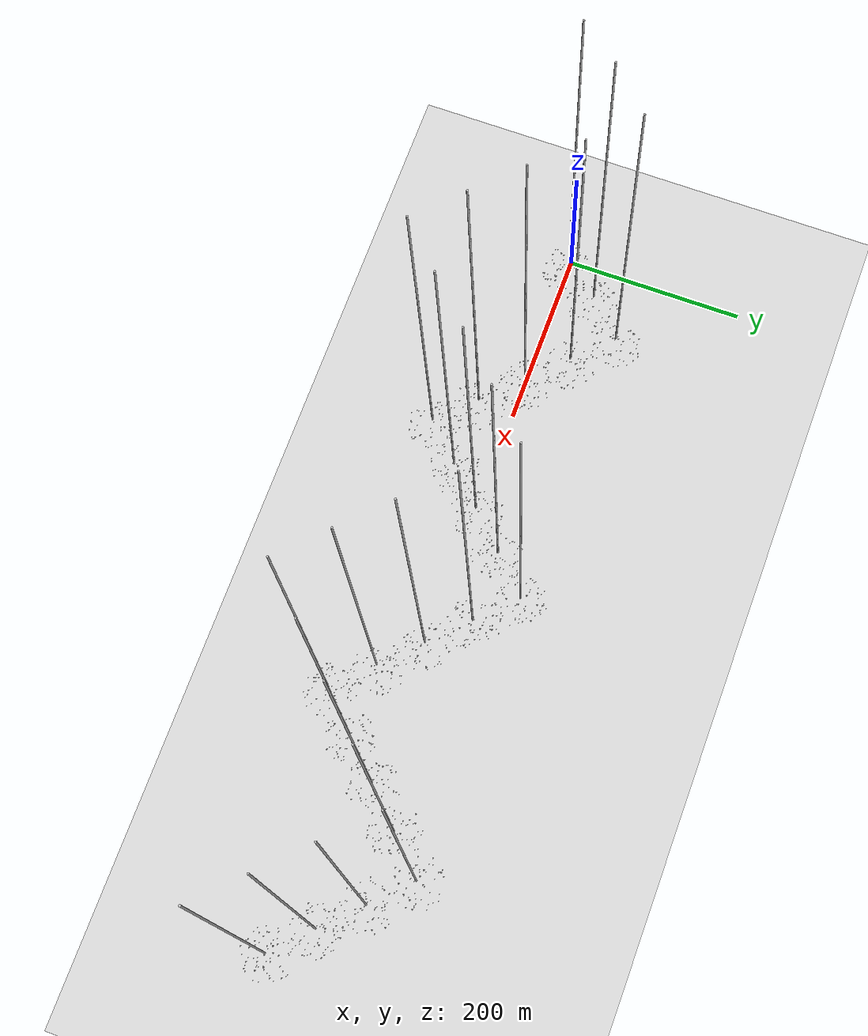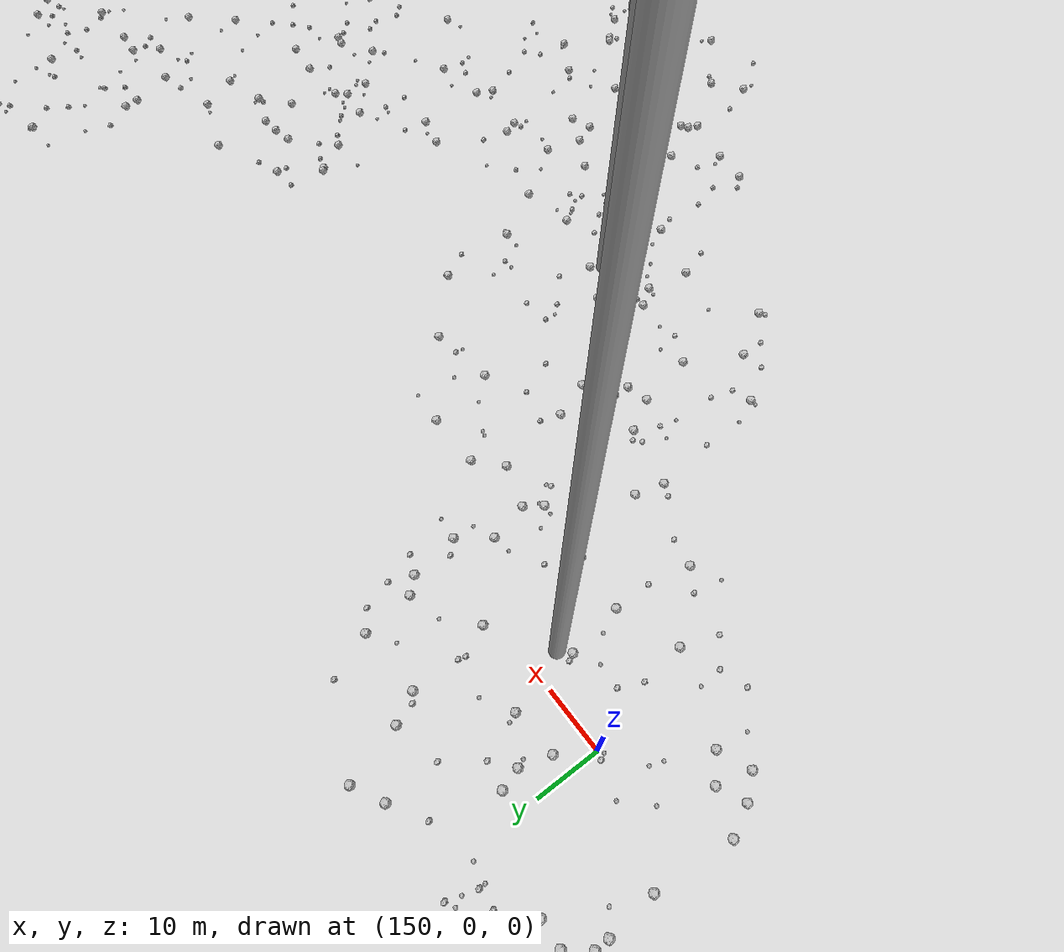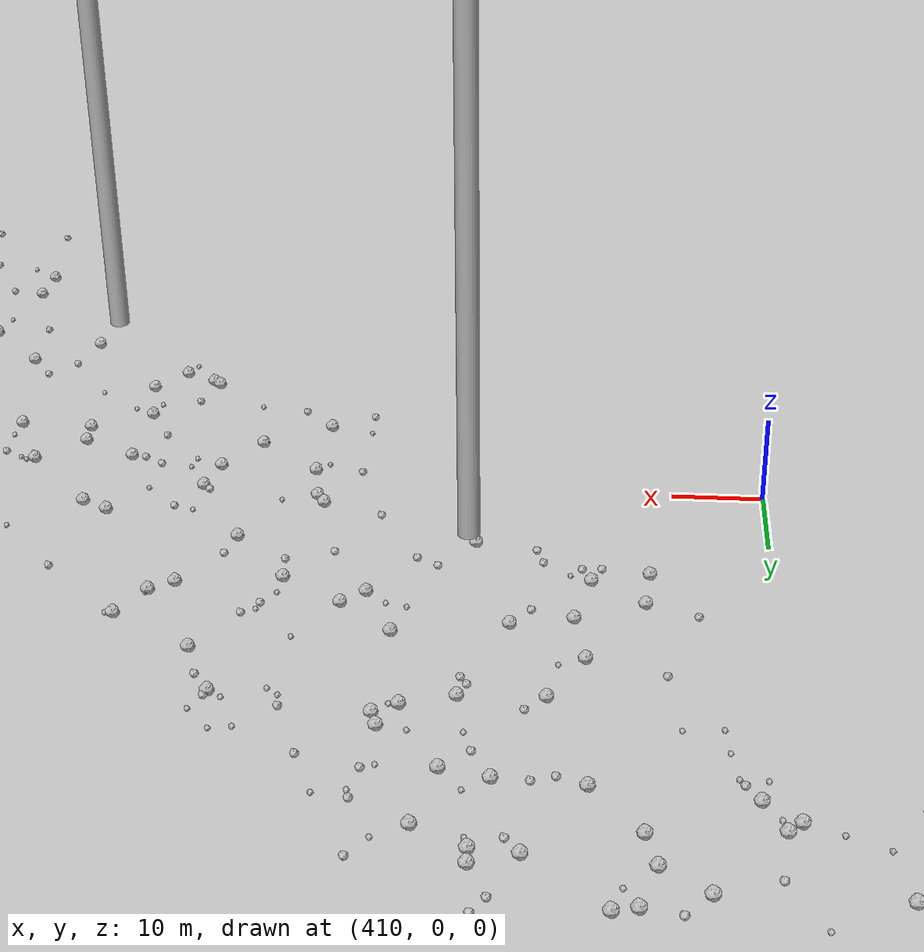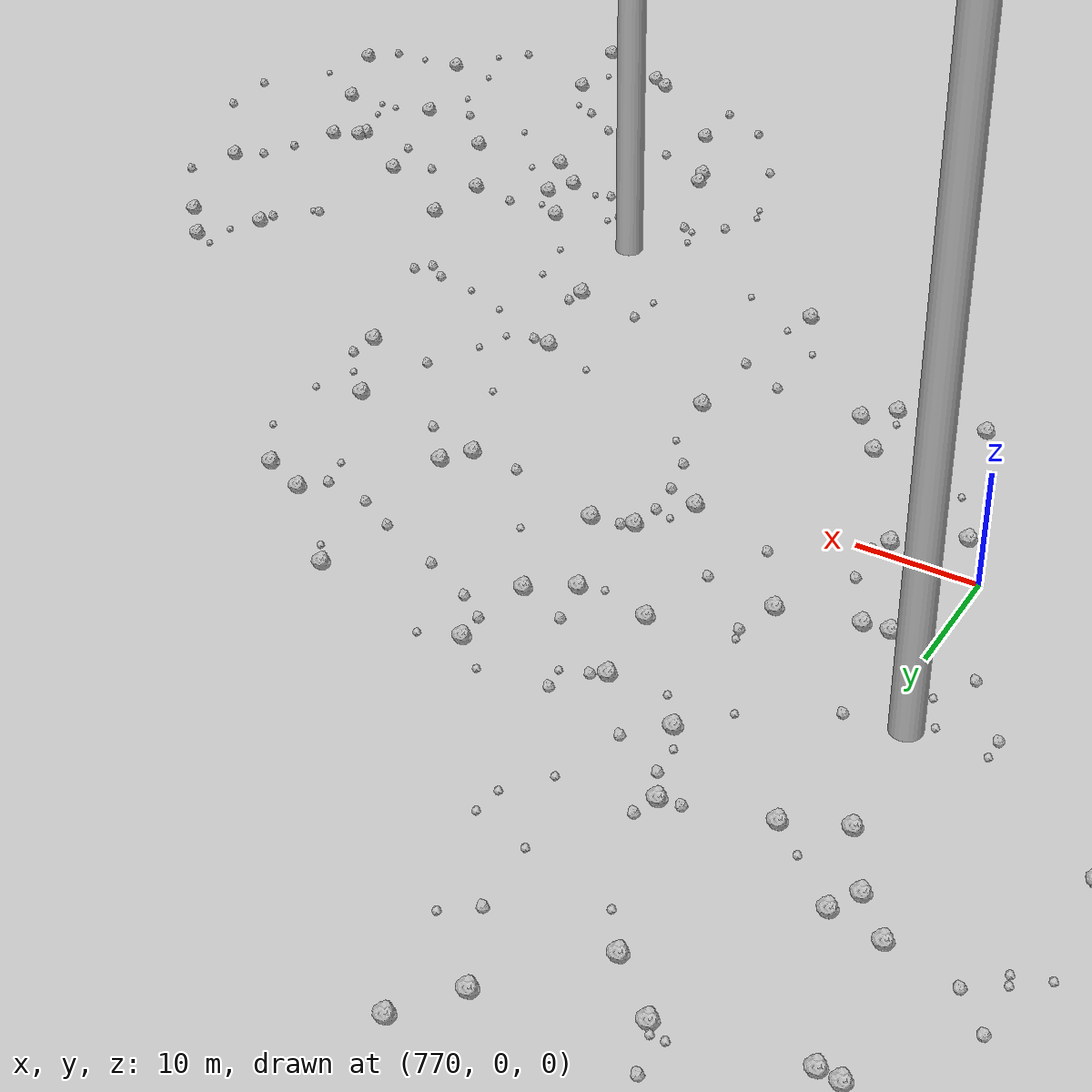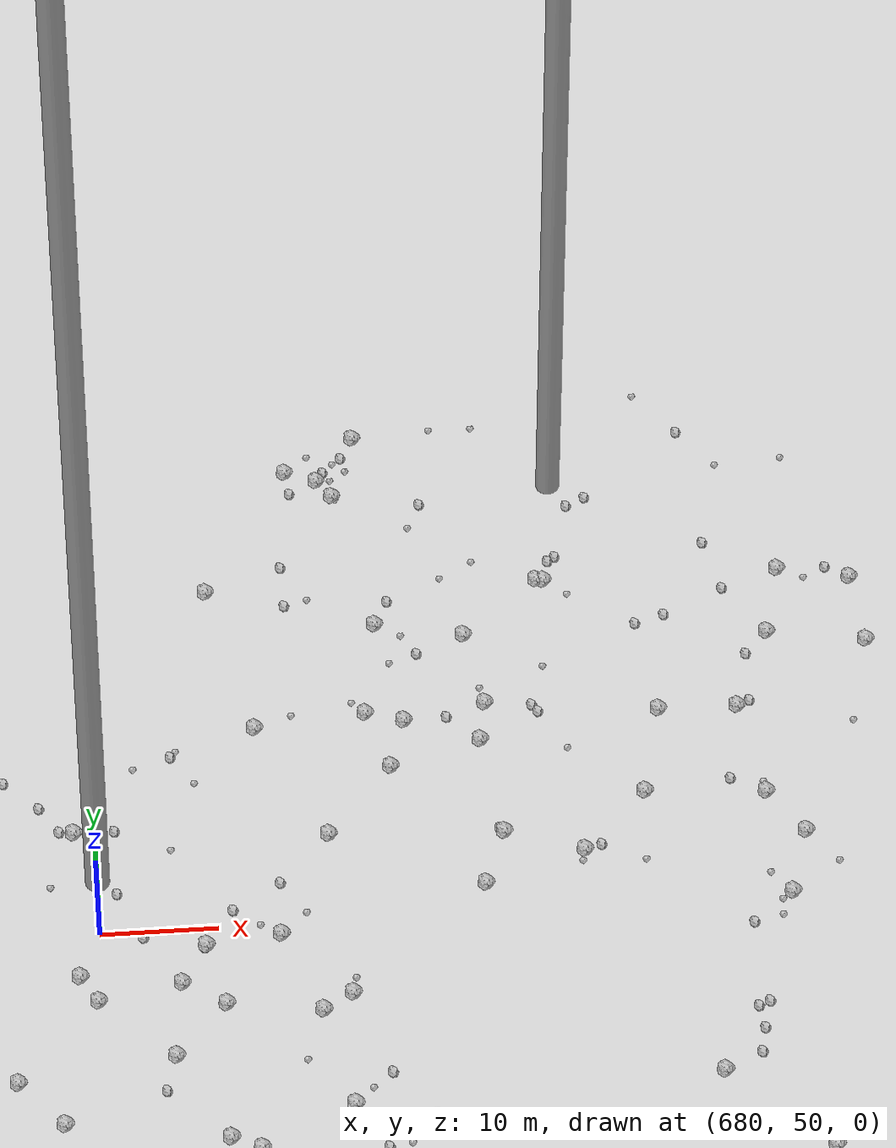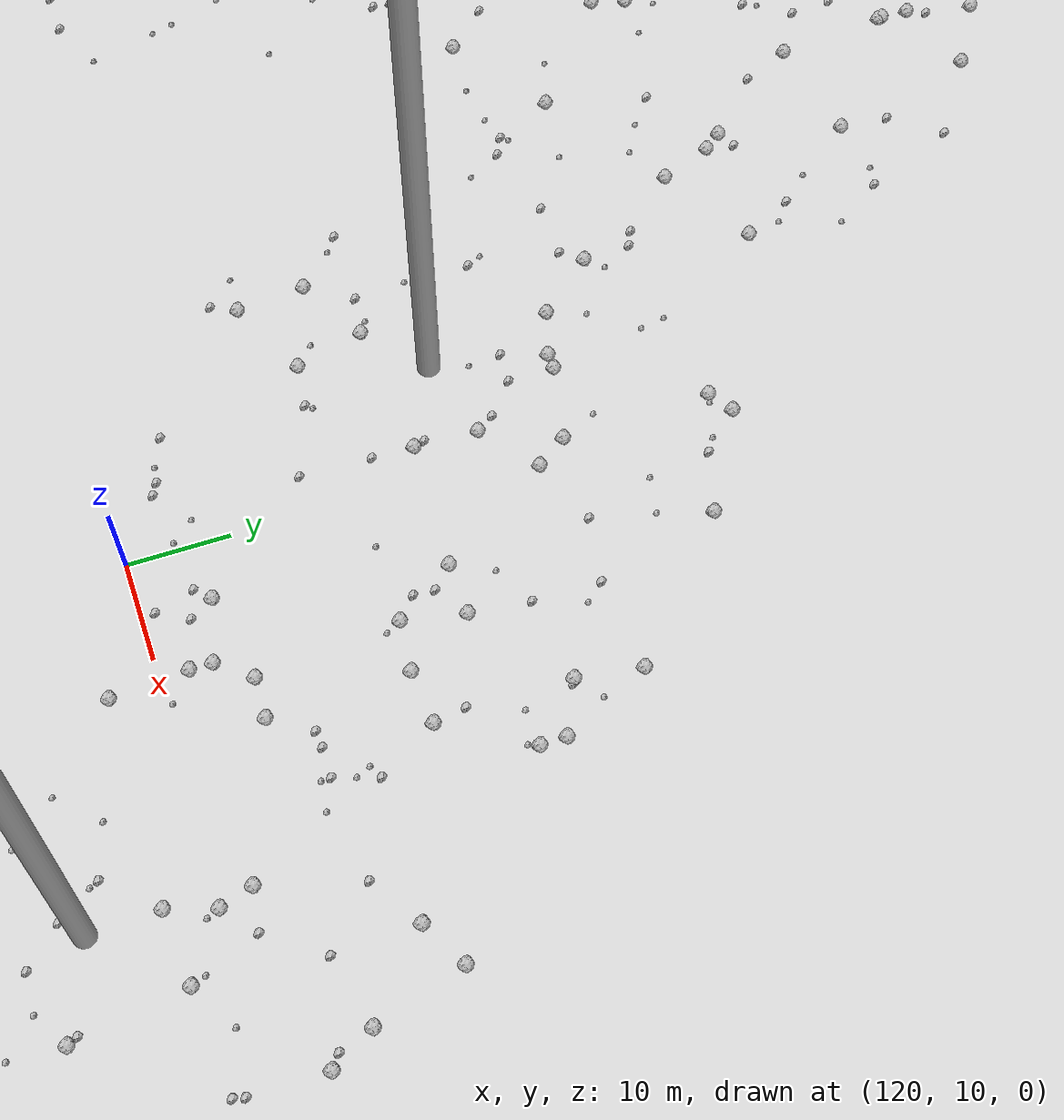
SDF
<sdf version="1.6">
 <world name="default">
  <include><uri>model://custom_ground</uri></include>
  <include><uri>model://sun</uri></include>
  <spherical_coordinates>
   <surface_model>EARTH_WGS84</surface_model>
   <latitude_deg>38.161479</latitude_deg>
   <longitude_deg>-122.454630</longitude_deg>
   <elevation>488.0</elevation>
   <heading_deg>90</heading_deg>
  </spherical_coordinates>
  <model name="rock1_0_0">
   <include><uri>model://rock1</uri><pose>10.353534659500475 -26.485820144668452 0.5 0 0 0</pose></include>
  </model>
  <model name="rock1_0_1">
   <include><uri>model://rock1</uri><pose>25.045041076871804 23.3982828396207 0.5 0 0 0</pose></include>
  </model>
  <model name="rock1_0_2">
   <include><uri>model://rock1</uri><pose>12.26940076858321 -8.898860153860145 0.5 0 0 0</pose></include>
  </model>
  <model name="rock1_0_3">
   <include><uri>model://rock1</uri><pose>27.81129628913171 -15.08280284263276 0.5 0 0 0</pose></include>
  </model>
  <model name="rock1_0_4">
   <include><uri>model://rock1</uri><pose>3.431283467191278 14.50852252464503 0.5 0 0 0</pose></include>
  </model>
  <model name="rock1_0_5">
   <include><uri>model://rock1</uri><pose>22.76654954815104 -25.10561689154749 0.5 0 0 0</pose></include>
  </model>
  <model name="rock1_0_6">
   <include><uri>model://rock1</uri><pose>35.93048079093833 -13.789267911669828 0.5 0 0 0</pose></include>
  </model>
  <model name="rock1_0_7">
   <include><uri>model://rock1</uri><pose>36.18989034486985 12.484855941916905 0.5 0 0 0</pose></include>
  </model>
  <model name="rock1_0_8">
   <include><uri>model://rock1</uri><pose>-6.867789546782468 -14.523020029441085 0.5 0 0 0</pose></include>
  </model>
  <model name="rock1_0_9">
   <include><uri>model://rock1</uri><pose>27.181268486295245 -10.131133207365842 0.5 0 0 0</pose></include>
  </model>
  <model name="rock1_0_10">
   <include><uri>model://rock1</uri><pose>22.10241037312138 -11.004564445049201 0.5 0 0 0</pose></include>
  </model>
  <model name="rock1_0_11">
   <include><uri>model://rock1</uri><pose>-13.004976365794992 12.954975235473746 0.5 0 0 0</pose></include>
  </model>
  <model name="rock1_0_12">
   <include><uri>model://rock1</uri><pose>-14.346528407437782 4.216435102887608 0.5 0 0 0</pose></include>
  </model>
  <model name="rock1_0_13">
   <include><uri>model://rock1</uri><pose>-2.503765077275048 -23.61104823280911 0.5 0 0 0</pose></include>
  </model>
  <model name="rock1_0_14">
   <include><uri>model://rock1</uri><pose>7.764807040509602 -18.589719966027726 0.5 0 0 0</pose></include>
  </model>
  <model name="rock1_0_15">
   <include><uri>model://rock1</uri><pose>23.53524599694542 -2.7545416927854163 0.5 0 0 0</pose></include>
  </model>
  <model name="rock1_0_16">
   <include><uri>model://rock1</uri><pose>-6.015940435910574 -11.233409011737088 0.5 0 0 0</pose></include>
  </model>
  <model name="rock1_0_17">
   <include><uri>model://rock1</uri><pose>37.993736004612714 2.525454313007245 0.5 0 0 0</pose></include>
  </model>
  <model name="rock1_0_18">
   <include><uri>model://rock1</uri><pose>5.322530658452642 5.559652756705503 0.5 0 0 0</pose></include>
  </model>
  <model name="rock1_0_19">
   <include><uri>model://rock1</uri><pose>12.00117200594876 -11.327752025288607 0.5 0 0 0</pose></include>
  </model>
  <model name="rock1_0_20">
   <include><uri>model://rock1</uri><pose>36.137777541261755 -2.7672222036140113 0.5 0 0 0</pose></include>
  </model>
  <model name="rock1_0_21">
   <include><uri>model://rock1</uri><pose>28.71049018036834 -18.36087743219004 0.5 0 0 0</pose></include>
  </model>
  <model name="rock1_0_22">
   <include><uri>model://rock1</uri><pose>28.96944864342838 -21.230283381374058 0.5 0 0 0</pose></include>
  </model>
  <model name="rock1_0_23">
   <include><uri>model://rock1</uri><pose>-9.234408368107744 4.875648324954142 0.5 0 0 0</pose></include>
  </model>
  <model name="rock1_0_24">
   <include><uri>model://rock1</uri><pose>36.366016415004864 11.40311303094743 0.5 0 0 0</pose></include>
  </model>
  <model name="rock1_0_25">
   <include><uri>model://rock1</uri><pose>21.633723734797613 -12.48264653880858 0.5 0 0 0</pose></include>
  </model>
  <model name="rock1_0_26">
   <include><uri>model://rock1</uri><pose>13.9449572687124 -12.595609178173078 0.5 0 0 0</pose></include>
  </model>
  <model name="rock2_0_0">
   <include><uri>model://rock2</uri><pose>16.11125227073549 -27.221403389869614 0.3 0 0 0</pose></include>
  </model>
  <model name="rock2_0_1">
   <include><uri>model://rock2</uri><pose>6.6393150016273985 -10.85607960643862 0.3 0 0 0</pose></include>
  </model>
  <model name="rock2_0_2">
   <include><uri>model://rock2</uri><pose>-8.188503412234041 11.062225208194882 0.3 0 0 0</pose></include>
  </model>
  <model name="rock2_0_3">
   <include><uri>model://rock2</uri><pose>30.712658321103184 13.78832300893847 0.3 0 0 0</pose></include>
  </model>
  <model name="rock2_0_4">
   <include><uri>model://rock2</uri><pose>-9.737667927949614 18.7649281970646 0.3 0 0 0</pose></include>
  </model>
  <model name="rock2_0_5">
   <include><uri>model://rock2</uri><pose>-18.92363509248398 -1.1414484592653054 0.3 0 0 0</pose></include>
  </model>
  <model name="rock2_0_6">
   <include><uri>model://rock2</uri><pose>-10.429916431454611 -20.04988269685863 0.3 0 0 0</pose></include>
  </model>
  <model name="rock2_0_7">
   <include><uri>model://rock2</uri><pose>-1.4148860128047325 -25.180633476344806 0.3 0 0 0</pose></include>
  </model>
  <model name="rock2_0_8">
   <include><uri>model://rock2</uri><pose>4.052366331668583 -21.295080060732403 0.3 0 0 0</pose></include>
  </model>
  <model name="rock2_0_9">
   <include><uri>model://rock2</uri><pose>-10.431789595978875 16.08690875752712 0.3 0 0 0</pose></include>
  </model>
  <model name="rock2_0_10">
   <include><uri>model://rock2</uri><pose>4.358529456318948 25.097020412433757 0.3 0 0 0</pose></include>
  </model>
  <model name="rock2_0_11">
   <include><uri>model://rock2</uri><pose>23.083309696370343 -20.692071618297007 0.3 0 0 0</pose></include>
  </model>
  <model name="rock2_0_12">
   <include><uri>model://rock2</uri><pose>31.910488822555095 -15.622460306529824 0.3 0 0 0</pose></include>
  </model>
  <model name="rock2_0_13">
   <include><uri>model://rock2</uri><pose>-7.985096026481397 -15.2279728868045 0.3 0 0 0</pose></include>
  </model>
  <model name="rock2_0_14">
   <include><uri>model://rock2</uri><pose>5.18093146841581 -6.514592742579467 0.3 0 0 0</pose></include>
  </model>
  <model name="rock2_0_15">
   <include><uri>model://rock2</uri><pose>-0.3584529870542106 -9.808946845722005 0.3 0 0 0</pose></include>
  </model>
  <model name="rock2_0_16">
   <include><uri>model://rock2</uri><pose>14.402634952810708 9.028583531330952 0.3 0 0 0</pose></include>
  </model>
  <model name="rock2_0_17">
   <include><uri>model://rock2</uri><pose>-3.702483994070384 -18.933836265885333 0.3 0 0 0</pose></include>
  </model>
  <model name="rock2_0_18">
   <include><uri>model://rock2</uri><pose>8.550882017220719 -7.666762801438935 0.3 0 0 0</pose></include>
  </model>
  <model name="rock2_0_19">
   <include><uri>model://rock2</uri><pose>-1.998712934579057 2.3978328522374355 0.3 0 0 0</pose></include>
  </model>
  <model name="rock2_0_20">
   <include><uri>model://rock2</uri><pose>-9.541593773949062 -22.19643291834767 0.3 0 0 0</pose></include>
  </model>
  <model name="rock2_0_21">
   <include><uri>model://rock2</uri><pose>24.32797845993108 11.429035219479644 0.3 0 0 0</pose></include>
  </model>
  <model name="rock2_0_22">
   <include><uri>model://rock2</uri><pose>-18.49181494383684 7.910000806333933 0.3 0 0 0</pose></include>
  </model>
  <model name="rock2_0_23">
   <include><uri>model://rock2</uri><pose>26.987171840242873 -24.061173489951774 0.3 0 0 0</pose></include>
  </model>
  <model name="rock2_0_24">
   <include><uri>model://rock2</uri><pose>-12.63742442365434 6.4061549035695435 0.3 0 0 0</pose></include>
  </model>
  <model name="rock2_0_25">
   <include><uri>model://rock2</uri><pose>33.93595414910494 -4.711348050006329 0.3 0 0 0</pose></include>
  </model>
  <model name="rock2_0_26">
   <include><uri>model://rock2</uri><pose>22.830058725323923 -26.408197162141075 0.3 0 0 0</pose></include>
  </model>
  <model name="rock3_0_0">
   <include><uri>model://rock3</uri><pose>8.56101677509021 -24.167930803212837 0.2 0 0 0</pose></include>
  </model>
  <model name="rock3_0_1">
   <include><uri>model://rock3</uri><pose>6.761542462029453 17.191552387644947 0.2 0 0 0</pose></include>
  </model>
  <model name="rock3_0_2">
   <include><uri>model://rock3</uri><pose>15.612438918579933 -5.408125672586728 0.2 0 0 0</pose></include>
  </model>
  <model name="rock3_0_3">
   <include><uri>model://rock3</uri><pose>11.032789261918548 2.3943340289514126 0.2 0 0 0</pose></include>
  </model>
  <model name="rock3_0_4">
   <include><uri>model://rock3</uri><pose>9.543849903816856 -6.406105116583024 0.2 0 0 0</pose></include>
  </model>
  <model name="rock3_0_5">
   <include><uri>model://rock3</uri><pose>7.809709750680064 -15.780000358705939 0.2 0 0 0</pose></include>
  </model>
  <model name="rock3_0_6">
   <include><uri>model://rock3</uri><pose>-10.561254310006994 -12.001210107637686 0.2 0 0 0</pose></include>
  </model>
  <model name="rock3_0_7">
   <include><uri>model://rock3</uri><pose>-3.2309085002253966 17.35174899467586 0.2 0 0 0</pose></include>
  </model>
  <model name="rock3_0_8">
   <include><uri>model://rock3</uri><pose>-10.173461811593349 13.04031017017946 0.2 0 0 0</pose></include>
  </model>
  <model name="rock3_0_9">
   <include><uri>model://rock3</uri><pose>23.43591487632429 8.062029808977428 0.2 0 0 0</pose></include>
  </model>
  <model name="rock3_0_10">
   <include><uri>model://rock3</uri><pose>21.815970133291046 -13.728194407260482 0.2 0 0 0</pose></include>
  </model>
  <model name="rock3_0_11">
   <include><uri>model://rock3</uri><pose>4.180349727324447 14.473615611379508 0.2 0 0 0</pose></include>
  </model>
  <model name="rock3_0_12">
   <include><uri>model://rock3</uri><pose>8.311541400459845 -14.495266021498985 0.2 0 0 0</pose></include>
  </model>
  <model name="rock3_0_13">
   <include><uri>model://rock3</uri><pose>5.9764896364892905 27.171055349658474 0.2 0 0 0</pose></include>
  </model>
  <model name="rock3_0_14">
   <include><uri>model://rock3</uri><pose>-5.730282148195213 -7.169475766958865 0.2 0 0 0</pose></include>
  </model>
  <model name="rock3_0_15">
   <include><uri>model://rock3</uri><pose>1.9047819188028434 -15.143722533927587 0.2 0 0 0</pose></include>
  </model>
  <model name="rock3_0_16">
   <include><uri>model://rock3</uri><pose>32.528434415573116 4.867701066272822 0.2 0 0 0</pose></include>
  </model>
  <model name="rock3_0_17">
   <include><uri>model://rock3</uri><pose>5.9075106664974015 12.090825059590372 0.2 0 0 0</pose></include>
  </model>
  <model name="rock3_0_18">
   <include><uri>model://rock3</uri><pose>25.40715269389677 -21.43670890164649 0.2 0 0 0</pose></include>
  </model>
  <model name="rock3_0_19">
   <include><uri>model://rock3</uri><pose>-1.250579437086813 25.60540738667389 0.2 0 0 0</pose></include>
  </model>
  <model name="rock3_0_20">
   <include><uri>model://rock3</uri><pose>-14.625057911617613 -5.421293277370886 0.2 0 0 0</pose></include>
  </model>
  <model name="rock3_0_21">
   <include><uri>model://rock3</uri><pose>-5.783328949337502 8.36709063281777 0.2 0 0 0</pose></include>
  </model>
  <model name="rock3_0_22">
   <include><uri>model://rock3</uri><pose>28.515094408047418 16.505230428504404 0.2 0 0 0</pose></include>
  </model>
  <model name="rock3_0_23">
   <include><uri>model://rock3</uri><pose>21.4159191924075 -26.608796045140434 0.2 0 0 0</pose></include>
  </model>
  <model name="rock3_0_24">
   <include><uri>model://rock3</uri><pose>-7.762402687801952 -12.90247029401932 0.2 0 0 0</pose></include>
  </model>
  <model name="rock3_0_25">
   <include><uri>model://rock3</uri><pose>2.6172597548236034 -4.727646225231737 0.2 0 0 0</pose></include>
  </model>
  <model name="rock3_0_26">
   <include><uri>model://rock3</uri><pose>13.75749470990931 11.262727021175472 0.2 0 0 0</pose></include>
  </model>
  <model name="rock1_1_0">
   <include><uri>model://rock1</uri><pose>20.811563174216097 22.206482133287153 0.5 0 0 0</pose></include>
  </model>
  <model name="rock1_1_1">
   <include><uri>model://rock1</uri><pose>26.293877646713575 55.20799841200313 0.5 0 0 0</pose></include>
  </model>
  <model name="rock1_1_2">
   <include><uri>model://rock1</uri><pose>22.264309347469613 43.06403866255032 0.5 0 0 0</pose></include>
  </model>
  <model name="rock1_1_3">
   <include><uri>model://rock1</uri><pose>36.732375939327625 31.750124949313946 0.5 0 0 0</pose></include>
  </model>
  <model name="rock1_1_4">
   <include><uri>model://rock1</uri><pose>24.609020841417717 14.94180150777474 0.5 0 0 0</pose></include>
  </model>
  <model name="rock1_1_5">
   <include><uri>model://rock1</uri><pose>28.10901024463589 46.35181416967821 0.5 0 0 0</pose></include>
  </model>
  <model name="rock1_1_6">
   <include><uri>model://rock1</uri><pose>27.57864444474541 24.658715741101524 0.5 0 0 0</pose></include>
  </model>
  <model name="rock1_1_7">
   <include><uri>model://rock1</uri><pose>12.979862528492148 38.42644063860732 0.5 0 0 0</pose></include>
  </model>
  <model name="rock1_1_8">
   <include><uri>model://rock1</uri><pose>32.616830754978004 50.13566248284269 0.5 0 0 0</pose></include>
  </model>
  <model name="rock1_1_9">
   <include><uri>model://rock1</uri><pose>49.088397172654766 62.37967771735456 0.5 0 0 0</pose></include>
  </model>
  <model name="rock1_1_10">
   <include><uri>model://rock1</uri><pose>19.193254009404235 58.09015689449631 0.5 0 0 0</pose></include>
  </model>
  <model name="rock1_1_11">
   <include><uri>model://rock1</uri><pose>43.600383686645415 41.54292474266212 0.5 0 0 0</pose></include>
  </model>
  <model name="rock1_1_12">
   <include><uri>model://rock1</uri><pose>61.0498620340993 51.19476440103534 0.5 0 0 0</pose></include>
  </model>
  <model name="rock1_1_13">
   <include><uri>model://rock1</uri><pose>28.63670856853843 13.851229073461928 0.5 0 0 0</pose></include>
  </model>
  <model name="rock1_1_14">
   <include><uri>model://rock1</uri><pose>24.378968388560274 47.60785364430815 0.5 0 0 0</pose></include>
  </model>
  <model name="rock1_1_15">
   <include><uri>model://rock1</uri><pose>42.75247713324407 29.220305896007048 0.5 0 0 0</pose></include>
  </model>
  <model name="rock1_1_16">
   <include><uri>model://rock1</uri><pose>42.497916847149845 10.43129604270475 0.5 0 0 0</pose></include>
  </model>
  <model name="rock1_1_17">
   <include><uri>model://rock1</uri><pose>36.83239033112699 16.05570971943111 0.5 0 0 0</pose></include>
  </model>
  <model name="rock1_1_18">
   <include><uri>model://rock1</uri><pose>15.446152057197706 40.37411505402713 0.5 0 0 0</pose></include>
  </model>
  <model name="rock1_1_19">
   <include><uri>model://rock1</uri><pose>26.028191981417823 53.130145055153434 0.5 0 0 0</pose></include>
  </model>
  <model name="rock1_1_20">
   <include><uri>model://rock1</uri><pose>11.228259963579514 44.54886223894517 0.5 0 0 0</pose></include>
  </model>
  <model name="rock1_1_21">
   <include><uri>model://rock1</uri><pose>50.83442703039024 38.50870452432589 0.5 0 0 0</pose></include>
  </model>
  <model name="rock1_1_22">
   <include><uri>model://rock1</uri><pose>50.11709910698307 33.24400653165413 0.5 0 0 0</pose></include>
  </model>
  <model name="rock1_1_23">
   <include><uri>model://rock1</uri><pose>65.69325256179971 52.12806155762875 0.5 0 0 0</pose></include>
  </model>
  <model name="rock1_1_24">
   <include><uri>model://rock1</uri><pose>34.882246192071094 36.835219687721136 0.5 0 0 0</pose></include>
  </model>
  <model name="rock1_1_25">
   <include><uri>model://rock1</uri><pose>16.331707897797763 41.67766658386269 0.5 0 0 0</pose></include>
  </model>
  <model name="rock1_1_26">
   <include><uri>model://rock1</uri><pose>33.377828700054934 65.81993812189398 0.5 0 0 0</pose></include>
  </model>
  <model name="rock2_1_0">
   <include><uri>model://rock2</uri><pose>53.09636772575081 55.635813154725035 0.3 0 0 0</pose></include>
  </model>
  <model name="rock2_1_1">
   <include><uri>model://rock2</uri><pose>55.0137951963461 63.122466329082314 0.3 0 0 0</pose></include>
  </model>
  <model name="rock2_1_2">
   <include><uri>model://rock2</uri><pose>56.64331465956396 60.478754302065305 0.3 0 0 0</pose></include>
  </model>
  <model name="rock2_1_3">
   <include><uri>model://rock2</uri><pose>23.106471405559358 16.014718526585042 0.3 0 0 0</pose></include>
  </model>
  <model name="rock2_1_4">
   <include><uri>model://rock2</uri><pose>19.909505871563148 56.631581349427506 0.3 0 0 0</pose></include>
  </model>
  <model name="rock2_1_5">
   <include><uri>model://rock2</uri><pose>17.031855833592527 20.844665272192145 0.3 0 0 0</pose></include>
  </model>
  <model name="rock2_1_6">
   <include><uri>model://rock2</uri><pose>40.6879843605135 24.391307841976477 0.3 0 0 0</pose></include>
  </model>
  <model name="rock2_1_7">
   <include><uri>model://rock2</uri><pose>44.431678580130104 45.49664844024196 0.3 0 0 0</pose></include>
  </model>
  <model name="rock2_1_8">
   <include><uri>model://rock2</uri><pose>13.264506736823762 38.92788236888192 0.3 0 0 0</pose></include>
  </model>
  <model name="rock2_1_9">
   <include><uri>model://rock2</uri><pose>53.772603991901256 18.44124541480538 0.3 0 0 0</pose></include>
  </model>
  <model name="rock2_1_10">
   <include><uri>model://rock2</uri><pose>34.09888030926338 61.639932221477004 0.3 0 0 0</pose></include>
  </model>
  <model name="rock2_1_11">
   <include><uri>model://rock2</uri><pose>39.63304654820715 27.183441991727477 0.3 0 0 0</pose></include>
  </model>
  <model name="rock2_1_12">
   <include><uri>model://rock2</uri><pose>22.600976580246517 37.35493196114341 0.3 0 0 0</pose></include>
  </model>
  <model name="rock2_1_13">
   <include><uri>model://rock2</uri><pose>23.60516252029879 57.61203616666724 0.3 0 0 0</pose></include>
  </model>
  <model name="rock2_1_14">
   <include><uri>model://rock2</uri><pose>39.649992849942564 60.356334479613636 0.3 0 0 0</pose></include>
  </model>
  <model name="rock2_1_15">
   <include><uri>model://rock2</uri><pose>20.990044504408228 26.77412858442555 0.3 0 0 0</pose></include>
  </model>
  <model name="rock2_1_16">
   <include><uri>model://rock2</uri><pose>34.03949479184418 65.73616091290769 0.3 0 0 0</pose></include>
  </model>
  <model name="rock2_1_17">
   <include><uri>model://rock2</uri><pose>48.75779650805788 56.76113602514016 0.3 0 0 0</pose></include>
  </model>
  <model name="rock2_1_18">
   <include><uri>model://rock2</uri><pose>65.2926581157294 50.13083497351631 0.3 0 0 0</pose></include>
  </model>
  <model name="rock2_1_19">
   <include><uri>model://rock2</uri><pose>35.49365727225653 22.17346048476309 0.3 0 0 0</pose></include>
  </model>
  <model name="rock2_1_20">
   <include><uri>model://rock2</uri><pose>20.18268893472996 55.623000384536624 0.3 0 0 0</pose></include>
  </model>
  <model name="rock2_1_21">
   <include><uri>model://rock2</uri><pose>20.309394527959732 32.19262205715459 0.3 0 0 0</pose></include>
  </model>
  <model name="rock2_1_22">
   <include><uri>model://rock2</uri><pose>57.92514183585404 18.44107056788909 0.3 0 0 0</pose></include>
  </model>
  <model name="rock2_1_23">
   <include><uri>model://rock2</uri><pose>36.7198585016972 68.40249074467661 0.3 0 0 0</pose></include>
  </model>
  <model name="rock2_1_24">
   <include><uri>model://rock2</uri><pose>36.346707529627096 33.10317280795849 0.3 0 0 0</pose></include>
  </model>
  <model name="rock2_1_25">
   <include><uri>model://rock2</uri><pose>23.70642798802944 60.50470800920781 0.3 0 0 0</pose></include>
  </model>
  <model name="rock2_1_26">
   <include><uri>model://rock2</uri><pose>59.59179994768163 44.093587514883836 0.3 0 0 0</pose></include>
  </model>
  <model name="rock3_1_0">
   <include><uri>model://rock3</uri><pose>60.845909306836724 29.60600194816628 0.2 0 0 0</pose></include>
  </model>
  <model name="rock3_1_1">
   <include><uri>model://rock3</uri><pose>21.295355440221943 30.952073400654353 0.2 0 0 0</pose></include>
  </model>
  <model name="rock3_1_2">
   <include><uri>model://rock3</uri><pose>16.245998466901398 53.25355801334534 0.2 0 0 0</pose></include>
  </model>
  <model name="rock3_1_3">
   <include><uri>model://rock3</uri><pose>21.71733195485354 35.40766009225132 0.2 0 0 0</pose></include>
  </model>
  <model name="rock3_1_4">
   <include><uri>model://rock3</uri><pose>59.47183792960022 50.517495733653654 0.2 0 0 0</pose></include>
  </model>
  <model name="rock3_1_5">
   <include><uri>model://rock3</uri><pose>33.24137504422123 45.76841130536364 0.2 0 0 0</pose></include>
  </model>
  <model name="rock3_1_6">
   <include><uri>model://rock3</uri><pose>59.20230295956051 34.82857243467039 0.2 0 0 0</pose></include>
  </model>
  <model name="rock3_1_7">
   <include><uri>model://rock3</uri><pose>63.34971693540405 56.945799253656574 0.2 0 0 0</pose></include>
  </model>
  <model name="rock3_1_8">
   <include><uri>model://rock3</uri><pose>35.98585540526301 20.980865322439765 0.2 0 0 0</pose></include>
  </model>
  <model name="rock3_1_9">
   <include><uri>model://rock3</uri><pose>12.479176962064603 38.971408536835355 0.2 0 0 0</pose></include>
  </model>
  <model name="rock3_1_10">
   <include><uri>model://rock3</uri><pose>41.8057011223203 14.608970661847797 0.2 0 0 0</pose></include>
  </model>
  <model name="rock3_1_11">
   <include><uri>model://rock3</uri><pose>60.274887709374994 40.89248291218327 0.2 0 0 0</pose></include>
  </model>
  <model name="rock3_1_12">
   <include><uri>model://rock3</uri><pose>36.45605542851511 57.11485274987042 0.2 0 0 0</pose></include>
  </model>
  <model name="rock3_1_13">
   <include><uri>model://rock3</uri><pose>62.93395684184367 20.797959429654398 0.2 0 0 0</pose></include>
  </model>
  <model name="rock3_1_14">
   <include><uri>model://rock3</uri><pose>67.69002949078083 38.20747227380119 0.2 0 0 0</pose></include>
  </model>
  <model name="rock3_1_15">
   <include><uri>model://rock3</uri><pose>14.910479072185993 26.263137677324696 0.2 0 0 0</pose></include>
  </model>
  <model name="rock3_1_16">
   <include><uri>model://rock3</uri><pose>17.992332842923155 51.75121054063324 0.2 0 0 0</pose></include>
  </model>
  <model name="rock3_1_17">
   <include><uri>model://rock3</uri><pose>15.05487840117654 40.30499700848447 0.2 0 0 0</pose></include>
  </model>
  <model name="rock3_1_18">
   <include><uri>model://rock3</uri><pose>61.39022458463744 27.439813649790533 0.2 0 0 0</pose></include>
  </model>
  <model name="rock3_1_19">
   <include><uri>model://rock3</uri><pose>16.06165398469599 50.509656378167705 0.2 0 0 0</pose></include>
  </model>
  <model name="rock3_1_20">
   <include><uri>model://rock3</uri><pose>59.047692099848526 59.84575741251874 0.2 0 0 0</pose></include>
  </model>
  <model name="rock3_1_21">
   <include><uri>model://rock3</uri><pose>53.44415693206261 31.791477849273907 0.2 0 0 0</pose></include>
  </model>
  <model name="rock3_1_22">
   <include><uri>model://rock3</uri><pose>59.07947065962925 55.88459646866363 0.2 0 0 0</pose></include>
  </model>
  <model name="rock3_1_23">
   <include><uri>model://rock3</uri><pose>12.216444238000815 44.62903424347718 0.2 0 0 0</pose></include>
  </model>
  <model name="rock3_1_24">
   <include><uri>model://rock3</uri><pose>45.4147187488079 50.70032632212233 0.2 0 0 0</pose></include>
  </model>
  <model name="rock3_1_25">
   <include><uri>model://rock3</uri><pose>45.90632673226122 49.26840099995212 0.2 0 0 0</pose></include>
  </model>
  <model name="rock3_1_26">
   <include><uri>model://rock3</uri><pose>62.31111100401267 44.41606475858253 0.2 0 0 0</pose></include>
  </model>
  <model name="rock1_2_0">
   <include><uri>model://rock1</uri><pose>73.06162794924768 56.41975943474132 0.5 0 0 0</pose></include>
  </model>
  <model name="rock1_2_1">
   <include><uri>model://rock1</uri><pose>58.696774071561784 89.56884305358116 0.5 0 0 0</pose></include>
  </model>
  <model name="rock1_2_2">
   <include><uri>model://rock1</uri><pose>71.41784557706153 81.42394865239706 0.5 0 0 0</pose></include>
  </model>
  <model name="rock1_2_3">
   <include><uri>model://rock1</uri><pose>56.56843297002165 62.61972786599366 0.5 0 0 0</pose></include>
  </model>
  <model name="rock1_2_4">
   <include><uri>model://rock1</uri><pose>101.78502378798558 60.87565070368002 0.5 0 0 0</pose></include>
  </model>
  <model name="rock1_2_5">
   <include><uri>model://rock1</uri><pose>84.72600747576959 109.20019593738527 0.5 0 0 0</pose></include>
  </model>
  <model name="rock1_2_6">
   <include><uri>model://rock1</uri><pose>71.99820013650621 71.86558849794848 0.5 0 0 0</pose></include>
  </model>
  <model name="rock1_2_7">
   <include><uri>model://rock1</uri><pose>94.83523179456017 90.76690133347911 0.5 0 0 0</pose></include>
  </model>
  <model name="rock1_2_8">
   <include><uri>model://rock1</uri><pose>61.69557920093267 68.26584968602606 0.5 0 0 0</pose></include>
  </model>
  <model name="rock1_2_9">
   <include><uri>model://rock1</uri><pose>95.0880573366353 71.71284923732563 0.5 0 0 0</pose></include>
  </model>
  <model name="rock1_2_10">
   <include><uri>model://rock1</uri><pose>82.6859439781113 63.264412003994195 0.5 0 0 0</pose></include>
  </model>
  <model name="rock1_2_11">
   <include><uri>model://rock1</uri><pose>104.0658400526853 77.34367614053426 0.5 0 0 0</pose></include>
  </model>
  <model name="rock1_2_12">
   <include><uri>model://rock1</uri><pose>83.32416100627036 102.61093861342621 0.5 0 0 0</pose></include>
  </model>
  <model name="rock1_2_13">
   <include><uri>model://rock1</uri><pose>57.398832201010705 91.22990004989953 0.5 0 0 0</pose></include>
  </model>
  <model name="rock1_2_14">
   <include><uri>model://rock1</uri><pose>83.29894288031926 99.4463613383144 0.5 0 0 0</pose></include>
  </model>
  <model name="rock1_2_15">
   <include><uri>model://rock1</uri><pose>66.36775701653485 60.15364695793186 0.5 0 0 0</pose></include>
  </model>
  <model name="rock1_2_16">
   <include><uri>model://rock1</uri><pose>72.3906421651922 87.19466768151233 0.5 0 0 0</pose></include>
  </model>
  <model name="rock1_2_17">
   <include><uri>model://rock1</uri><pose>83.2221027102056 99.87096153055234 0.5 0 0 0</pose></include>
  </model>
  <model name="rock1_2_18">
   <include><uri>model://rock1</uri><pose>81.23084549008789 107.5908305747808 0.5 0 0 0</pose></include>
  </model>
  <model name="rock1_2_19">
   <include><uri>model://rock1</uri><pose>72.89083918748047 75.2574801527883 0.5 0 0 0</pose></include>
  </model>
  <model name="rock1_2_20">
   <include><uri>model://rock1</uri><pose>91.78758923946853 78.62641182588202 0.5 0 0 0</pose></include>
  </model>
  <model name="rock1_2_21">
   <include><uri>model://rock1</uri><pose>59.92650228028121 95.26548794766845 0.5 0 0 0</pose></include>
  </model>
  <model name="rock1_2_22">
   <include><uri>model://rock1</uri><pose>91.05249608534666 105.52477932114888 0.5 0 0 0</pose></include>
  </model>
  <model name="rock1_2_23">
   <include><uri>model://rock1</uri><pose>93.12905399611866 76.85799837239253 0.5 0 0 0</pose></include>
  </model>
  <model name="rock1_2_24">
   <include><uri>model://rock1</uri><pose>73.51043348629847 50.7312419830157 0.5 0 0 0</pose></include>
  </model>
  <model name="rock1_2_25">
   <include><uri>model://rock1</uri><pose>59.959788773055294 96.36622967819386 0.5 0 0 0</pose></include>
  </model>
  <model name="rock1_2_26">
   <include><uri>model://rock1</uri><pose>84.26708354126028 88.58019773869225 0.5 0 0 0</pose></include>
  </model>
  <model name="rock2_2_0">
   <include><uri>model://rock2</uri><pose>85.22285840350298 57.58665948343352 0.3 0 0 0</pose></include>
  </model>
  <model name="rock2_2_1">
   <include><uri>model://rock2</uri><pose>101.50511202899148 65.6569496679936 0.3 0 0 0</pose></include>
  </model>
  <model name="rock2_2_2">
   <include><uri>model://rock2</uri><pose>101.49377974128497 82.2956636502461 0.3 0 0 0</pose></include>
  </model>
  <model name="rock2_2_3">
   <include><uri>model://rock2</uri><pose>86.1885757528189 83.95483917905798 0.3 0 0 0</pose></include>
  </model>
  <model name="rock2_2_4">
   <include><uri>model://rock2</uri><pose>69.25865914006098 60.453496760038675 0.3 0 0 0</pose></include>
  </model>
  <model name="rock2_2_5">
   <include><uri>model://rock2</uri><pose>69.6956081338439 98.89109227363718 0.3 0 0 0</pose></include>
  </model>
  <model name="rock2_2_6">
   <include><uri>model://rock2</uri><pose>102.3162201410994 91.43306223345712 0.3 0 0 0</pose></include>
  </model>
  <model name="rock2_2_7">
   <include><uri>model://rock2</uri><pose>69.264175625286 79.84430769058007 0.3 0 0 0</pose></include>
  </model>
  <model name="rock2_2_8">
   <include><uri>model://rock2</uri><pose>70.80958156591221 103.53024800494771 0.3 0 0 0</pose></include>
  </model>
  <model name="rock2_2_9">
   <include><uri>model://rock2</uri><pose>63.81481358253453 103.10523236661095 0.3 0 0 0</pose></include>
  </model>
  <model name="rock2_2_10">
   <include><uri>model://rock2</uri><pose>79.43888579838003 95.48164555054849 0.3 0 0 0</pose></include>
  </model>
  <model name="rock2_2_11">
   <include><uri>model://rock2</uri><pose>58.851622423190776 70.65731330191534 0.3 0 0 0</pose></include>
  </model>
  <model name="rock2_2_12">
   <include><uri>model://rock2</uri><pose>99.95354372570424 66.36380394934655 0.3 0 0 0</pose></include>
  </model>
  <model name="rock2_2_13">
   <include><uri>model://rock2</uri><pose>98.68814295231708 100.49825121146165 0.3 0 0 0</pose></include>
  </model>
  <model name="rock2_2_14">
   <include><uri>model://rock2</uri><pose>95.16795847178881 95.65027327211922 0.3 0 0 0</pose></include>
  </model>
  <model name="rock2_2_15">
   <include><uri>model://rock2</uri><pose>75.90242142454343 104.01002613517902 0.3 0 0 0</pose></include>
  </model>
  <model name="rock2_2_16">
   <include><uri>model://rock2</uri><pose>87.0821232048184 56.658813551438094 0.3 0 0 0</pose></include>
  </model>
  <model name="rock2_2_17">
   <include><uri>model://rock2</uri><pose>93.47090506175377 79.68955710304894 0.3 0 0 0</pose></include>
  </model>
  <model name="rock2_2_18">
   <include><uri>model://rock2</uri><pose>77.01151841333679 86.81342239377514 0.3 0 0 0</pose></include>
  </model>
  <model name="rock2_2_19">
   <include><uri>model://rock2</uri><pose>79.71302055140845 91.34552082591264 0.3 0 0 0</pose></include>
  </model>
  <model name="rock2_2_20">
   <include><uri>model://rock2</uri><pose>67.0809342171231 93.78316051110536 0.3 0 0 0</pose></include>
  </model>
  <model name="rock2_2_21">
   <include><uri>model://rock2</uri><pose>84.0252461269086 104.54401010475613 0.3 0 0 0</pose></include>
  </model>
  <model name="rock2_2_22">
   <include><uri>model://rock2</uri><pose>85.10936914767296 73.31076210060873 0.3 0 0 0</pose></include>
  </model>
  <model name="rock2_2_23">
   <include><uri>model://rock2</uri><pose>68.80983556272889 74.68745209378952 0.3 0 0 0</pose></include>
  </model>
  <model name="rock2_2_24">
   <include><uri>model://rock2</uri><pose>94.65201559868785 58.7680746909094 0.3 0 0 0</pose></include>
  </model>
  <model name="rock2_2_25">
   <include><uri>model://rock2</uri><pose>62.164756640731184 68.2205276530914 0.3 0 0 0</pose></include>
  </model>
  <model name="rock2_2_26">
   <include><uri>model://rock2</uri><pose>77.16006537345251 106.99556139198381 0.3 0 0 0</pose></include>
  </model>
  <model name="rock3_2_0">
   <include><uri>model://rock3</uri><pose>57.183831911999405 72.13505165661711 0.2 0 0 0</pose></include>
  </model>
  <model name="rock3_2_1">
   <include><uri>model://rock3</uri><pose>77.51649810204108 88.20211461065645 0.2 0 0 0</pose></include>
  </model>
  <model name="rock3_2_2">
   <include><uri>model://rock3</uri><pose>90.91226503654737 69.43562376102776 0.2 0 0 0</pose></include>
  </model>
  <model name="rock3_2_3">
   <include><uri>model://rock3</uri><pose>59.17900865806649 85.47820718501092 0.2 0 0 0</pose></include>
  </model>
  <model name="rock3_2_4">
   <include><uri>model://rock3</uri><pose>70.03408003029963 71.87115900619652 0.2 0 0 0</pose></include>
  </model>
  <model name="rock3_2_5">
   <include><uri>model://rock3</uri><pose>78.48130546797309 56.126269596310536 0.2 0 0 0</pose></include>
  </model>
  <model name="rock3_2_6">
   <include><uri>model://rock3</uri><pose>59.62789240615258 101.15917219968108 0.2 0 0 0</pose></include>
  </model>
  <model name="rock3_2_7">
   <include><uri>model://rock3</uri><pose>79.78466066724677 102.2306480467193 0.2 0 0 0</pose></include>
  </model>
  <model name="rock3_2_8">
   <include><uri>model://rock3</uri><pose>103.41624376866665 80.75060551395777 0.2 0 0 0</pose></include>
  </model>
  <model name="rock3_2_9">
   <include><uri>model://rock3</uri><pose>100.20189883062437 91.81823831802164 0.2 0 0 0</pose></include>
  </model>
  <model name="rock3_2_10">
   <include><uri>model://rock3</uri><pose>73.87443257011321 78.03572334082469 0.2 0 0 0</pose></include>
  </model>
  <model name="rock3_2_11">
   <include><uri>model://rock3</uri><pose>54.61517290272784 71.60053243583225 0.2 0 0 0</pose></include>
  </model>
  <model name="rock3_2_12">
   <include><uri>model://rock3</uri><pose>85.66332784121639 58.28947650246436 0.2 0 0 0</pose></include>
  </model>
  <model name="rock3_2_13">
   <include><uri>model://rock3</uri><pose>85.1957620211477 57.52035282655922 0.2 0 0 0</pose></include>
  </model>
  <model name="rock3_2_14">
   <include><uri>model://rock3</uri><pose>88.82543810574862 53.33907123530758 0.2 0 0 0</pose></include>
  </model>
  <model name="rock3_2_15">
   <include><uri>model://rock3</uri><pose>87.85877756178502 71.10391476832211 0.2 0 0 0</pose></include>
  </model>
  <model name="rock3_2_16">
   <include><uri>model://rock3</uri><pose>74.17311674139619 92.43978933447883 0.2 0 0 0</pose></include>
  </model>
  <model name="rock3_2_17">
   <include><uri>model://rock3</uri><pose>77.72172039101275 64.80003349489616 0.2 0 0 0</pose></include>
  </model>
  <model name="rock3_2_18">
   <include><uri>model://rock3</uri><pose>89.24417351536266 62.5301171872449 0.2 0 0 0</pose></include>
  </model>
  <model name="rock3_2_19">
   <include><uri>model://rock3</uri><pose>82.58457830446622 56.79804650842619 0.2 0 0 0</pose></include>
  </model>
  <model name="rock3_2_20">
   <include><uri>model://rock3</uri><pose>76.99051426627213 75.37168376559734 0.2 0 0 0</pose></include>
  </model>
  <model name="rock3_2_21">
   <include><uri>model://rock3</uri><pose>68.70214969924535 65.00088679298516 0.2 0 0 0</pose></include>
  </model>
  <model name="rock3_2_22">
   <include><uri>model://rock3</uri><pose>98.93229067539919 85.06817875530227 0.2 0 0 0</pose></include>
  </model>
  <model name="rock3_2_23">
   <include><uri>model://rock3</uri><pose>105.35243821058015 86.67659885175172 0.2 0 0 0</pose></include>
  </model>
  <model name="rock3_2_24">
   <include><uri>model://rock3</uri><pose>63.67999291943906 103.56879147497939 0.2 0 0 0</pose></include>
  </model>
  <model name="rock3_2_25">
   <include><uri>model://rock3</uri><pose>82.53546659319575 100.00138760356225 0.2 0 0 0</pose></include>
  </model>
  <model name="rock3_2_26">
   <include><uri>model://rock3</uri><pose>72.8152734281879 96.2186329171513 0.2 0 0 0</pose></include>
  </model>
  <model name="rock1_3_0">
   <include><uri>model://rock1</uri><pose>96.26344306607767 33.748889334315336 0.5 0 0 0</pose></include>
  </model>
  <model name="rock1_3_1">
   <include><uri>model://rock1</uri><pose>122.24372206582721 68.82232523794768 0.5 0 0 0</pose></include>
  </model>
  <model name="rock1_3_2">
   <include><uri>model://rock1</uri><pose>144.7301186767112 51.98138372201248 0.5 0 0 0</pose></include>
  </model>
  <model name="rock1_3_3">
   <include><uri>model://rock1</uri><pose>134.73613774565183 18.278792567359677 0.5 0 0 0</pose></include>
  </model>
  <model name="rock1_3_4">
   <include><uri>model://rock1</uri><pose>131.89302671944372 63.39559591750957 0.5 0 0 0</pose></include>
  </model>
  <model name="rock1_3_5">
   <include><uri>model://rock1</uri><pose>96.81376801587315 26.953107630775303 0.5 0 0 0</pose></include>
  </model>
  <model name="rock1_3_6">
   <include><uri>model://rock1</uri><pose>116.60703776506847 38.818373941213295 0.5 0 0 0</pose></include>
  </model>
  <model name="rock1_3_7">
   <include><uri>model://rock1</uri><pose>148.92732027368743 43.170298152798814 0.5 0 0 0</pose></include>
  </model>
  <model name="rock1_3_8">
   <include><uri>model://rock1</uri><pose>120.08394583706377 52.52955807586616 0.5 0 0 0</pose></include>
  </model>
  <model name="rock1_3_9">
   <include><uri>model://rock1</uri><pose>132.16435366428544 15.03936473385966 0.5 0 0 0</pose></include>
  </model>
  <model name="rock1_3_10">
   <include><uri>model://rock1</uri><pose>134.64821119227003 38.422984980079626 0.5 0 0 0</pose></include>
  </model>
  <model name="rock1_3_11">
   <include><uri>model://rock1</uri><pose>143.76886985348506 45.57119310641679 0.5 0 0 0</pose></include>
  </model>
  <model name="rock1_3_12">
   <include><uri>model://rock1</uri><pose>102.99319709460121 37.60621524742437 0.5 0 0 0</pose></include>
  </model>
  <model name="rock1_3_13">
   <include><uri>model://rock1</uri><pose>148.9495788936748 40.61316078615365 0.5 0 0 0</pose></include>
  </model>
  <model name="rock1_3_14">
   <include><uri>model://rock1</uri><pose>138.52709162610282 31.816522728077945 0.5 0 0 0</pose></include>
  </model>
  <model name="rock1_3_15">
   <include><uri>model://rock1</uri><pose>110.95950458915195 54.04112357426267 0.5 0 0 0</pose></include>
  </model>
  <model name="rock1_3_16">
   <include><uri>model://rock1</uri><pose>129.4050245717215 38.26761562719876 0.5 0 0 0</pose></include>
  </model>
  <model name="rock1_3_17">
   <include><uri>model://rock1</uri><pose>143.96315129253958 32.25658916965249 0.5 0 0 0</pose></include>
  </model>
  <model name="rock1_3_18">
   <include><uri>model://rock1</uri><pose>133.44266816785685 32.317643241822886 0.5 0 0 0</pose></include>
  </model>
  <model name="rock1_3_19">
   <include><uri>model://rock1</uri><pose>125.91882995578139 16.627445064293568 0.5 0 0 0</pose></include>
  </model>
  <model name="rock1_3_20">
   <include><uri>model://rock1</uri><pose>104.71967123066487 30.79782678596093 0.5 0 0 0</pose></include>
  </model>
  <model name="rock1_3_21">
   <include><uri>model://rock1</uri><pose>132.14092968467818 12.848736836690476 0.5 0 0 0</pose></include>
  </model>
  <model name="rock1_3_22">
   <include><uri>model://rock1</uri><pose>122.18827219440684 49.49651691328385 0.5 0 0 0</pose></include>
  </model>
  <model name="rock1_3_23">
   <include><uri>model://rock1</uri><pose>106.42507799062231 55.415362737873544 0.5 0 0 0</pose></include>
  </model>
  <model name="rock1_3_24">
   <include><uri>model://rock1</uri><pose>112.54713397925957 54.09673008353473 0.5 0 0 0</pose></include>
  </model>
  <model name="rock1_3_25">
   <include><uri>model://rock1</uri><pose>116.84333479301736 45.098098088278505 0.5 0 0 0</pose></include>
  </model>
  <model name="rock1_3_26">
   <include><uri>model://rock1</uri><pose>119.87297357831372 67.25147816803691 0.5 0 0 0</pose></include>
  </model>
  <model name="rock2_3_0">
   <include><uri>model://rock2</uri><pose>98.75057861374657 49.8546783643571 0.3 0 0 0</pose></include>
  </model>
  <model name="rock2_3_1">
   <include><uri>model://rock2</uri><pose>127.23525874491375 14.301228150692557 0.3 0 0 0</pose></include>
  </model>
  <model name="rock2_3_2">
   <include><uri>model://rock2</uri><pose>91.41429133758272 38.260724371860285 0.3 0 0 0</pose></include>
  </model>
  <model name="rock2_3_3">
   <include><uri>model://rock2</uri><pose>109.41657537928253 49.72819369517761 0.3 0 0 0</pose></include>
  </model>
  <model name="rock2_3_4">
   <include><uri>model://rock2</uri><pose>115.60909007897125 46.87353626945644 0.3 0 0 0</pose></include>
  </model>
  <model name="rock2_3_5">
   <include><uri>model://rock2</uri><pose>135.24308947803905 44.42236880417221 0.3 0 0 0</pose></include>
  </model>
  <model name="rock2_3_6">
   <include><uri>model://rock2</uri><pose>131.25403904980695 34.23240908417803 0.3 0 0 0</pose></include>
  </model>
  <model name="rock2_3_7">
   <include><uri>model://rock2</uri><pose>116.1790055896679 27.69350984468631 0.3 0 0 0</pose></include>
  </model>
  <model name="rock2_3_8">
   <include><uri>model://rock2</uri><pose>112.45685056318135 49.581260738657335 0.3 0 0 0</pose></include>
  </model>
  <model name="rock2_3_9">
   <include><uri>model://rock2</uri><pose>143.32806521438545 35.50055550532606 0.3 0 0 0</pose></include>
  </model>
  <model name="rock2_3_10">
   <include><uri>model://rock2</uri><pose>128.79372699292134 52.149098297322325 0.3 0 0 0</pose></include>
  </model>
  <model name="rock2_3_11">
   <include><uri>model://rock2</uri><pose>108.97303674247262 30.272971672391613 0.3 0 0 0</pose></include>
  </model>
  <model name="rock2_3_12">
   <include><uri>model://rock2</uri><pose>116.3747513580405 34.74047066161853 0.3 0 0 0</pose></include>
  </model>
  <model name="rock2_3_13">
   <include><uri>model://rock2</uri><pose>98.98328539946672 38.23052431074042 0.3 0 0 0</pose></include>
  </model>
  <model name="rock2_3_14">
   <include><uri>model://rock2</uri><pose>125.62043189360551 11.318181223253365 0.3 0 0 0</pose></include>
  </model>
  <model name="rock2_3_15">
   <include><uri>model://rock2</uri><pose>95.52955124957128 24.534300440740395 0.3 0 0 0</pose></include>
  </model>
  <model name="rock2_3_16">
   <include><uri>model://rock2</uri><pose>112.59951218354283 14.761113283132097 0.3 0 0 0</pose></include>
  </model>
  <model name="rock2_3_17">
   <include><uri>model://rock2</uri><pose>144.1764003971391 45.38853955768299 0.3 0 0 0</pose></include>
  </model>
  <model name="rock2_3_18">
   <include><uri>model://rock2</uri><pose>131.374108923454 36.323584194641946 0.3 0 0 0</pose></include>
  </model>
  <model name="rock2_3_19">
   <include><uri>model://rock2</uri><pose>125.71188548101492 65.16596204985125 0.3 0 0 0</pose></include>
  </model>
  <model name="rock2_3_20">
   <include><uri>model://rock2</uri><pose>113.8023720179454 14.11925840513387 0.3 0 0 0</pose></include>
  </model>
  <model name="rock2_3_21">
   <include><uri>model://rock2</uri><pose>124.4144198407625 15.247820780189157 0.3 0 0 0</pose></include>
  </model>
  <model name="rock2_3_22">
   <include><uri>model://rock2</uri><pose>100.111968928511 58.865624058758186 0.3 0 0 0</pose></include>
  </model>
  <model name="rock2_3_23">
   <include><uri>model://rock2</uri><pose>108.0587043883353 16.295811853747743 0.3 0 0 0</pose></include>
  </model>
  <model name="rock2_3_24">
   <include><uri>model://rock2</uri><pose>135.35388770985094 51.0911190545933 0.3 0 0 0</pose></include>
  </model>
  <model name="rock2_3_25">
   <include><uri>model://rock2</uri><pose>142.9997146928868 22.195998016797652 0.3 0 0 0</pose></include>
  </model>
  <model name="rock2_3_26">
   <include><uri>model://rock2</uri><pose>116.17256768412504 39.95488425691115 0.3 0 0 0</pose></include>
  </model>
  <model name="rock3_3_0">
   <include><uri>model://rock3</uri><pose>93.01237432579724 27.20603556871723 0.2 0 0 0</pose></include>
  </model>
  <model name="rock3_3_1">
   <include><uri>model://rock3</uri><pose>98.56946495980112 43.34391741055988 0.2 0 0 0</pose></include>
  </model>
  <model name="rock3_3_2">
   <include><uri>model://rock3</uri><pose>102.64536246812328 32.625795277846336 0.2 0 0 0</pose></include>
  </model>
  <model name="rock3_3_3">
   <include><uri>model://rock3</uri><pose>130.2273877797477 58.29371270697937 0.2 0 0 0</pose></include>
  </model>
  <model name="rock3_3_4">
   <include><uri>model://rock3</uri><pose>98.02420205949959 51.27840420322965 0.2 0 0 0</pose></include>
  </model>
  <model name="rock3_3_5">
   <include><uri>model://rock3</uri><pose>107.59119557908299 59.158316009230866 0.2 0 0 0</pose></include>
  </model>
  <model name="rock3_3_6">
   <include><uri>model://rock3</uri><pose>103.05644707518937 62.58664820404559 0.2 0 0 0</pose></include>
  </model>
  <model name="rock3_3_7">
   <include><uri>model://rock3</uri><pose>146.21649270499233 47.558705354695356 0.2 0 0 0</pose></include>
  </model>
  <model name="rock3_3_8">
   <include><uri>model://rock3</uri><pose>119.179514191696 14.682780044857711 0.2 0 0 0</pose></include>
  </model>
  <model name="rock3_3_9">
   <include><uri>model://rock3</uri><pose>126.48551554465983 58.97420295545898 0.2 0 0 0</pose></include>
  </model>
  <model name="rock3_3_10">
   <include><uri>model://rock3</uri><pose>131.1981353836788 42.23100647355193 0.2 0 0 0</pose></include>
  </model>
  <model name="rock3_3_11">
   <include><uri>model://rock3</uri><pose>92.90492084285542 37.14014062348808 0.2 0 0 0</pose></include>
  </model>
  <model name="rock3_3_12">
   <include><uri>model://rock3</uri><pose>118.35079425450148 56.121823113294084 0.2 0 0 0</pose></include>
  </model>
  <model name="rock3_3_13">
   <include><uri>model://rock3</uri><pose>109.61102474767759 46.49065206507696 0.2 0 0 0</pose></include>
  </model>
  <model name="rock3_3_14">
   <include><uri>model://rock3</uri><pose>110.79966697791204 63.649214628173645 0.2 0 0 0</pose></include>
  </model>
  <model name="rock3_3_15">
   <include><uri>model://rock3</uri><pose>110.39245701466247 66.11241740406727 0.2 0 0 0</pose></include>
  </model>
  <model name="rock3_3_16">
   <include><uri>model://rock3</uri><pose>125.37276936692004 32.40278422737331 0.2 0 0 0</pose></include>
  </model>
  <model name="rock3_3_17">
   <include><uri>model://rock3</uri><pose>145.2137731036217 40.4733631346499 0.2 0 0 0</pose></include>
  </model>
  <model name="rock3_3_18">
   <include><uri>model://rock3</uri><pose>124.30724434750985 66.07082242968653 0.2 0 0 0</pose></include>
  </model>
  <model name="rock3_3_19">
   <include><uri>model://rock3</uri><pose>120.63104097346394 67.0941990200887 0.2 0 0 0</pose></include>
  </model>
  <model name="rock3_3_20">
   <include><uri>model://rock3</uri><pose>101.66650170677066 38.41513761144868 0.2 0 0 0</pose></include>
  </model>
  <model name="rock3_3_21">
   <include><uri>model://rock3</uri><pose>148.4352808965773 39.63711431173075 0.2 0 0 0</pose></include>
  </model>
  <model name="rock3_3_22">
   <include><uri>model://rock3</uri><pose>117.34880038983927 16.893602673505807 0.2 0 0 0</pose></include>
  </model>
  <model name="rock3_3_23">
   <include><uri>model://rock3</uri><pose>134.10932798038397 30.859739789836716 0.2 0 0 0</pose></include>
  </model>
  <model name="rock3_3_24">
   <include><uri>model://rock3</uri><pose>110.94066705422051 14.971639609018993 0.2 0 0 0</pose></include>
  </model>
  <model name="rock3_3_25">
   <include><uri>model://rock3</uri><pose>109.41638673808818 30.917576804647393 0.2 0 0 0</pose></include>
  </model>
  <model name="rock3_3_26">
   <include><uri>model://rock3</uri><pose>136.89070232799153 49.27621968715027 0.2 0 0 0</pose></include>
  </model>
  <model name="rock1_4_0">
   <include><uri>model://rock1</uri><pose>182.6109323254712 7.626861473880268 0.5 0 0 0</pose></include>
  </model>
  <model name="rock1_4_1">
   <include><uri>model://rock1</uri><pose>154.55084678199657 9.643963657686449 0.5 0 0 0</pose></include>
  </model>
  <model name="rock1_4_2">
   <include><uri>model://rock1</uri><pose>153.51750321119994 12.930994290603557 0.5 0 0 0</pose></include>
  </model>
  <model name="rock1_4_3">
   <include><uri>model://rock1</uri><pose>160.4429925743081 5.592748823672288 0.5 0 0 0</pose></include>
  </model>
  <model name="rock1_4_4">
   <include><uri>model://rock1</uri><pose>163.4850192469803 -14.505709180852458 0.5 0 0 0</pose></include>
  </model>
  <model name="rock1_4_5">
   <include><uri>model://rock1</uri><pose>153.88852968461225 -17.934879662585676 0.5 0 0 0</pose></include>
  </model>
  <model name="rock1_4_6">
   <include><uri>model://rock1</uri><pose>184.0519125299344 -13.559188663347989 0.5 0 0 0</pose></include>
  </model>
  <model name="rock1_4_7">
   <include><uri>model://rock1</uri><pose>162.1400318987827 -5.606685945962305 0.5 0 0 0</pose></include>
  </model>
  <model name="rock1_4_8">
   <include><uri>model://rock1</uri><pose>161.99676828696434 -27.12939130318102 0.5 0 0 0</pose></include>
  </model>
  <model name="rock1_4_9">
   <include><uri>model://rock1</uri><pose>186.07094205513613 -2.393332072291475 0.5 0 0 0</pose></include>
  </model>
  <model name="rock1_4_10">
   <include><uri>model://rock1</uri><pose>171.1071005127007 14.939160661312457 0.5 0 0 0</pose></include>
  </model>
  <model name="rock1_4_11">
   <include><uri>model://rock1</uri><pose>140.68866826483745 -12.542120805886118 0.5 0 0 0</pose></include>
  </model>
  <model name="rock1_4_12">
   <include><uri>model://rock1</uri><pose>184.79878202795226 5.3819900094609 0.5 0 0 0</pose></include>
  </model>
  <model name="rock1_4_13">
   <include><uri>model://rock1</uri><pose>182.52885354190124 -7.250850593460413 0.5 0 0 0</pose></include>
  </model>
  <model name="rock1_4_14">
   <include><uri>model://rock1</uri><pose>176.6710043268544 -19.380457841018966 0.5 0 0 0</pose></include>
  </model>
  <model name="rock1_4_15">
   <include><uri>model://rock1</uri><pose>137.38077767115124 -9.350763081952323 0.5 0 0 0</pose></include>
  </model>
  <model name="rock1_4_16">
   <include><uri>model://rock1</uri><pose>181.72231796185514 15.666354773775922 0.5 0 0 0</pose></include>
  </model>
  <model name="rock1_4_17">
   <include><uri>model://rock1</uri><pose>138.80868440071828 18.130853746620907 0.5 0 0 0</pose></include>
  </model>
  <model name="rock1_4_18">
   <include><uri>model://rock1</uri><pose>153.11926537341017 4.976679012297417 0.5 0 0 0</pose></include>
  </model>
  <model name="rock1_4_19">
   <include><uri>model://rock1</uri><pose>161.30576929906596 25.824347613407106 0.5 0 0 0</pose></include>
  </model>
  <model name="rock1_4_20">
   <include><uri>model://rock1</uri><pose>132.645116236559 5.271036742140616 0.5 0 0 0</pose></include>
  </model>
  <model name="rock1_4_21">
   <include><uri>model://rock1</uri><pose>131.2972391113266 -6.796585575036723 0.5 0 0 0</pose></include>
  </model>
  <model name="rock1_4_22">
   <include><uri>model://rock1</uri><pose>172.8307426590053 1.9341311357813602 0.5 0 0 0</pose></include>
  </model>
  <model name="rock1_4_23">
   <include><uri>model://rock1</uri><pose>133.3800705388928 -11.190610486830217 0.5 0 0 0</pose></include>
  </model>
  <model name="rock1_4_24">
   <include><uri>model://rock1</uri><pose>168.67991937154147 19.25056540900391 0.5 0 0 0</pose></include>
  </model>
  <model name="rock1_4_25">
   <include><uri>model://rock1</uri><pose>165.9405905399315 28.31317718359717 0.5 0 0 0</pose></include>
  </model>
  <model name="rock1_4_26">
   <include><uri>model://rock1</uri><pose>135.9501994702964 -14.505327433037392 0.5 0 0 0</pose></include>
  </model>
  <model name="rock2_4_0">
   <include><uri>model://rock2</uri><pose>184.16603297336695 -0.48899467135031927 0.3 0 0 0</pose></include>
  </model>
  <model name="rock2_4_1">
   <include><uri>model://rock2</uri><pose>148.23897442382386 -20.294544915986496 0.3 0 0 0</pose></include>
  </model>
  <model name="rock2_4_2">
   <include><uri>model://rock2</uri><pose>174.84659465630682 -10.542975717096155 0.3 0 0 0</pose></include>
  </model>
  <model name="rock2_4_3">
   <include><uri>model://rock2</uri><pose>151.4240619480141 -3.8398523168976304 0.3 0 0 0</pose></include>
  </model>
  <model name="rock2_4_4">
   <include><uri>model://rock2</uri><pose>172.3124753737349 -15.681594282660527 0.3 0 0 0</pose></include>
  </model>
  <model name="rock2_4_5">
   <include><uri>model://rock2</uri><pose>170.69419369613246 6.416736346693831 0.3 0 0 0</pose></include>
  </model>
  <model name="rock2_4_6">
   <include><uri>model://rock2</uri><pose>158.5369697740125 -24.878915874328115 0.3 0 0 0</pose></include>
  </model>
  <model name="rock2_4_7">
   <include><uri>model://rock2</uri><pose>154.7615676868713 -7.411862027956719 0.3 0 0 0</pose></include>
  </model>
  <model name="rock2_4_8">
   <include><uri>model://rock2</uri><pose>161.5858006225464 -4.589487085283068 0.3 0 0 0</pose></include>
  </model>
  <model name="rock2_4_9">
   <include><uri>model://rock2</uri><pose>147.3544038811494 26.41229660367717 0.3 0 0 0</pose></include>
  </model>
  <model name="rock2_4_10">
   <include><uri>model://rock2</uri><pose>145.9983794869015 22.144100191800263 0.3 0 0 0</pose></include>
  </model>
  <model name="rock2_4_11">
   <include><uri>model://rock2</uri><pose>157.67055527831948 12.296974002601374 0.3 0 0 0</pose></include>
  </model>
  <model name="rock2_4_12">
   <include><uri>model://rock2</uri><pose>184.7605428853158 13.51490005828407 0.3 0 0 0</pose></include>
  </model>
  <model name="rock2_4_13">
   <include><uri>model://rock2</uri><pose>178.90451685962228 22.634399341243558 0.3 0 0 0</pose></include>
  </model>
  <model name="rock2_4_14">
   <include><uri>model://rock2</uri><pose>163.4617324804384 -20.541163637314934 0.3 0 0 0</pose></include>
  </model>
  <model name="rock2_4_15">
   <include><uri>model://rock2</uri><pose>169.7678155429026 15.932391324634288 0.3 0 0 0</pose></include>
  </model>
  <model name="rock2_4_16">
   <include><uri>model://rock2</uri><pose>148.80245125689794 0.3442600386003001 0.3 0 0 0</pose></include>
  </model>
  <model name="rock2_4_17">
   <include><uri>model://rock2</uri><pose>161.51442504670146 17.57258348322369 0.3 0 0 0</pose></include>
  </model>
  <model name="rock2_4_18">
   <include><uri>model://rock2</uri><pose>187.8053376902259 4.114856777994021 0.3 0 0 0</pose></include>
  </model>
  <model name="rock2_4_19">
   <include><uri>model://rock2</uri><pose>170.95214616244402 7.520592732823431 0.3 0 0 0</pose></include>
  </model>
  <model name="rock2_4_20">
   <include><uri>model://rock2</uri><pose>166.45638844810549 -28.108450770085206 0.3 0 0 0</pose></include>
  </model>
  <model name="rock2_4_21">
   <include><uri>model://rock2</uri><pose>144.1866026260229 -21.597379785665137 0.3 0 0 0</pose></include>
  </model>
  <model name="rock2_4_22">
   <include><uri>model://rock2</uri><pose>153.17964136018477 -10.958419041463323 0.3 0 0 0</pose></include>
  </model>
  <model name="rock2_4_23">
   <include><uri>model://rock2</uri><pose>141.32204779328546 22.056899084288716 0.3 0 0 0</pose></include>
  </model>
  <model name="rock2_4_24">
   <include><uri>model://rock2</uri><pose>186.20028621271672 9.002313368592844 0.3 0 0 0</pose></include>
  </model>
  <model name="rock2_4_25">
   <include><uri>model://rock2</uri><pose>156.16673025922913 22.624760864639065 0.3 0 0 0</pose></include>
  </model>
  <model name="rock2_4_26">
   <include><uri>model://rock2</uri><pose>151.88390189055968 -23.597859539416554 0.3 0 0 0</pose></include>
  </model>
  <model name="rock3_4_0">
   <include><uri>model://rock3</uri><pose>185.89953967934343 -5.925308590150252 0.2 0 0 0</pose></include>
  </model>
  <model name="rock3_4_1">
   <include><uri>model://rock3</uri><pose>143.7068909379739 -6.190025693586222 0.2 0 0 0</pose></include>
  </model>
  <model name="rock3_4_2">
   <include><uri>model://rock3</uri><pose>177.31041003184987 6.245429219146267 0.2 0 0 0</pose></include>
  </model>
  <model name="rock3_4_3">
   <include><uri>model://rock3</uri><pose>159.84130200206727 6.979425450507726 0.2 0 0 0</pose></include>
  </model>
  <model name="rock3_4_4">
   <include><uri>model://rock3</uri><pose>139.85963947000369 -17.51005100123994 0.2 0 0 0</pose></include>
  </model>
  <model name="rock3_4_5">
   <include><uri>model://rock3</uri><pose>189.70834621094366 -2.7987354428366693 0.2 0 0 0</pose></include>
  </model>
  <model name="rock3_4_6">
   <include><uri>model://rock3</uri><pose>175.27764176345661 -17.612110247154703 0.2 0 0 0</pose></include>
  </model>
  <model name="rock3_4_7">
   <include><uri>model://rock3</uri><pose>144.42511184203758 -4.249092278364802 0.2 0 0 0</pose></include>
  </model>
  <model name="rock3_4_8">
   <include><uri>model://rock3</uri><pose>149.20586394576532 -0.574326580685085 0.2 0 0 0</pose></include>
  </model>
  <model name="rock3_4_9">
   <include><uri>model://rock3</uri><pose>148.05128473980415 -16.71600039931902 0.2 0 0 0</pose></include>
  </model>
  <model name="rock3_4_10">
   <include><uri>model://rock3</uri><pose>143.66538393846042 1.9712151959572886 0.2 0 0 0</pose></include>
  </model>
  <model name="rock3_4_11">
   <include><uri>model://rock3</uri><pose>179.5890353388145 -7.736526743230854 0.2 0 0 0</pose></include>
  </model>
  <model name="rock3_4_12">
   <include><uri>model://rock3</uri><pose>161.80221393449366 -10.85456779494827 0.2 0 0 0</pose></include>
  </model>
  <model name="rock3_4_13">
   <include><uri>model://rock3</uri><pose>148.91202992473646 20.839329773874624 0.2 0 0 0</pose></include>
  </model>
  <model name="rock3_4_14">
   <include><uri>model://rock3</uri><pose>145.9972620143349 21.18323034279168 0.2 0 0 0</pose></include>
  </model>
  <model name="rock3_4_15">
   <include><uri>model://rock3</uri><pose>134.76931061235823 10.571735037318433 0.2 0 0 0</pose></include>
  </model>
  <model name="rock3_4_16">
   <include><uri>model://rock3</uri><pose>154.99833958433695 8.384055700301808 0.2 0 0 0</pose></include>
  </model>
  <model name="rock3_4_17">
   <include><uri>model://rock3</uri><pose>158.62707694036365 -7.722878468607991 0.2 0 0 0</pose></include>
  </model>
  <model name="rock3_4_18">
   <include><uri>model://rock3</uri><pose>157.636704975072 -29.423711473879962 0.2 0 0 0</pose></include>
  </model>
  <model name="rock3_4_19">
   <include><uri>model://rock3</uri><pose>146.63414122387735 24.283928792195333 0.2 0 0 0</pose></include>
  </model>
  <model name="rock3_4_20">
   <include><uri>model://rock3</uri><pose>140.08286653922443 -1.7560565061808084 0.2 0 0 0</pose></include>
  </model>
  <model name="rock3_4_21">
   <include><uri>model://rock3</uri><pose>179.68179121669976 -13.701829103363874 0.2 0 0 0</pose></include>
  </model>
  <model name="rock3_4_22">
   <include><uri>model://rock3</uri><pose>164.9837704073272 8.260552748718084 0.2 0 0 0</pose></include>
  </model>
  <model name="rock3_4_23">
   <include><uri>model://rock3</uri><pose>178.00246321847192 12.947342330249604 0.2 0 0 0</pose></include>
  </model>
  <model name="rock3_4_24">
   <include><uri>model://rock3</uri><pose>176.2777403237 -18.63716013551052 0.2 0 0 0</pose></include>
  </model>
  <model name="rock3_4_25">
   <include><uri>model://rock3</uri><pose>146.01128851356933 25.679400892362125 0.2 0 0 0</pose></include>
  </model>
  <model name="rock3_4_26">
   <include><uri>model://rock3</uri><pose>180.64760992446833 -16.268263730520438 0.2 0 0 0</pose></include>
  </model>
  <model name="rock1_5_0">
   <include><uri>model://rock1</uri><pose>174.21136805574446 -32.900684909179446 0.5 0 0 0</pose></include>
  </model>
  <model name="rock1_5_1">
   <include><uri>model://rock1</uri><pose>192.81662905784378 -33.60073831488882 0.5 0 0 0</pose></include>
  </model>
  <model name="rock1_5_2">
   <include><uri>model://rock1</uri><pose>203.5288818775599 -55.322370830356775 0.5 0 0 0</pose></include>
  </model>
  <model name="rock1_5_3">
   <include><uri>model://rock1</uri><pose>175.4678482369522 -28.236462448689764 0.5 0 0 0</pose></include>
  </model>
  <model name="rock1_5_4">
   <include><uri>model://rock1</uri><pose>207.19142181389924 -47.07179048024436 0.5 0 0 0</pose></include>
  </model>
  <model name="rock1_5_5">
   <include><uri>model://rock1</uri><pose>193.09634447507744 -27.98398766216267 0.5 0 0 0</pose></include>
  </model>
  <model name="rock1_5_6">
   <include><uri>model://rock1</uri><pose>227.47049815156754 -43.255784970257764 0.5 0 0 0</pose></include>
  </model>
  <model name="rock1_5_7">
   <include><uri>model://rock1</uri><pose>203.97641239106508 -11.823816555150515 0.5 0 0 0</pose></include>
  </model>
  <model name="rock1_5_8">
   <include><uri>model://rock1</uri><pose>201.43630681633584 -52.23254381946059 0.5 0 0 0</pose></include>
  </model>
  <model name="rock1_5_9">
   <include><uri>model://rock1</uri><pose>202.27855258474378 -62.579973165033074 0.5 0 0 0</pose></include>
  </model>
  <model name="rock1_5_10">
   <include><uri>model://rock1</uri><pose>195.3609798748572 -34.142989766643716 0.5 0 0 0</pose></include>
  </model>
  <model name="rock1_5_11">
   <include><uri>model://rock1</uri><pose>194.95580522055536 -11.961981696011975 0.5 0 0 0</pose></include>
  </model>
  <model name="rock1_5_12">
   <include><uri>model://rock1</uri><pose>188.59152098324574 -66.5460027678081 0.5 0 0 0</pose></include>
  </model>
  <model name="rock1_5_13">
   <include><uri>model://rock1</uri><pose>223.6721675139393 -53.57660529000921 0.5 0 0 0</pose></include>
  </model>
  <model name="rock1_5_14">
   <include><uri>model://rock1</uri><pose>206.15198832854273 -22.782331019487415 0.5 0 0 0</pose></include>
  </model>
  <model name="rock1_5_15">
   <include><uri>model://rock1</uri><pose>226.26731710485336 -29.733759355460748 0.5 0 0 0</pose></include>
  </model>
  <model name="rock1_5_16">
   <include><uri>model://rock1</uri><pose>184.0216095217914 -35.25958256267422 0.5 0 0 0</pose></include>
  </model>
  <model name="rock1_5_17">
   <include><uri>model://rock1</uri><pose>216.7891905859866 -21.228617939464144 0.5 0 0 0</pose></include>
  </model>
  <model name="rock1_5_18">
   <include><uri>model://rock1</uri><pose>188.89254520925417 -49.92321078277479 0.5 0 0 0</pose></include>
  </model>
  <model name="rock1_5_19">
   <include><uri>model://rock1</uri><pose>184.06786648642515 -58.71974942361341 0.5 0 0 0</pose></include>
  </model>
  <model name="rock1_5_20">
   <include><uri>model://rock1</uri><pose>187.02126647119525 -40.51744000621234 0.5 0 0 0</pose></include>
  </model>
  <model name="rock1_5_21">
   <include><uri>model://rock1</uri><pose>190.9236976918034 -15.733414682129975 0.5 0 0 0</pose></include>
  </model>
  <model name="rock1_5_22">
   <include><uri>model://rock1</uri><pose>182.1902061422241 -16.251048488340466 0.5 0 0 0</pose></include>
  </model>
  <model name="rock1_5_23">
   <include><uri>model://rock1</uri><pose>212.03390482777124 -65.49309550769414 0.5 0 0 0</pose></include>
  </model>
  <model name="rock1_5_24">
   <include><uri>model://rock1</uri><pose>176.99474969289275 -53.5952548611801 0.5 0 0 0</pose></include>
  </model>
  <model name="rock1_5_25">
   <include><uri>model://rock1</uri><pose>190.59254714174693 -39.695017059754306 0.5 0 0 0</pose></include>
  </model>
  <model name="rock1_5_26">
   <include><uri>model://rock1</uri><pose>213.1258332200983 -50.25502137481952 0.5 0 0 0</pose></include>
  </model>
  <model name="rock2_5_0">
   <include><uri>model://rock2</uri><pose>181.67877239626063 -35.10302961737681 0.3 0 0 0</pose></include>
  </model>
  <model name="rock2_5_1">
   <include><uri>model://rock2</uri><pose>172.26929850313266 -32.07414918579512 0.3 0 0 0</pose></include>
  </model>
  <model name="rock2_5_2">
   <include><uri>model://rock2</uri><pose>209.0308726068155 -37.4567727146377 0.3 0 0 0</pose></include>
  </model>
  <model name="rock2_5_3">
   <include><uri>model://rock2</uri><pose>213.5696092902899 -36.97791354336181 0.3 0 0 0</pose></include>
  </model>
  <model name="rock2_5_4">
   <include><uri>model://rock2</uri><pose>181.18825069838286 -49.0023253994874 0.3 0 0 0</pose></include>
  </model>
  <model name="rock2_5_5">
   <include><uri>model://rock2</uri><pose>203.00951272394758 -52.30086740393817 0.3 0 0 0</pose></include>
  </model>
  <model name="rock2_5_6">
   <include><uri>model://rock2</uri><pose>210.31063897504706 -40.91438512569239 0.3 0 0 0</pose></include>
  </model>
  <model name="rock2_5_7">
   <include><uri>model://rock2</uri><pose>221.29113670228247 -59.07215454901656 0.3 0 0 0</pose></include>
  </model>
  <model name="rock2_5_8">
   <include><uri>model://rock2</uri><pose>180.13421014623373 -52.67169410368266 0.3 0 0 0</pose></include>
  </model>
  <model name="rock2_5_9">
   <include><uri>model://rock2</uri><pose>180.50085478547558 -59.401083814810754 0.3 0 0 0</pose></include>
  </model>
  <model name="rock2_5_10">
   <include><uri>model://rock2</uri><pose>194.12405045950945 -24.76327357864109 0.3 0 0 0</pose></include>
  </model>
  <model name="rock2_5_11">
   <include><uri>model://rock2</uri><pose>202.07581891653712 -32.032451899270946 0.3 0 0 0</pose></include>
  </model>
  <model name="rock2_5_12">
   <include><uri>model://rock2</uri><pose>184.0781833227176 -62.71540187756381 0.3 0 0 0</pose></include>
  </model>
  <model name="rock2_5_13">
   <include><uri>model://rock2</uri><pose>222.9158143879688 -39.431300401607785 0.3 0 0 0</pose></include>
  </model>
  <model name="rock2_5_14">
   <include><uri>model://rock2</uri><pose>228.6952635215881 -34.32290951500391 0.3 0 0 0</pose></include>
  </model>
  <model name="rock2_5_15">
   <include><uri>model://rock2</uri><pose>214.7079937031919 -44.880835749675775 0.3 0 0 0</pose></include>
  </model>
  <model name="rock2_5_16">
   <include><uri>model://rock2</uri><pose>190.58703938932672 -37.318952412018206 0.3 0 0 0</pose></include>
  </model>
  <model name="rock2_5_17">
   <include><uri>model://rock2</uri><pose>182.12474851328463 -39.130526363614 0.3 0 0 0</pose></include>
  </model>
  <model name="rock2_5_18">
   <include><uri>model://rock2</uri><pose>184.19199189240243 -19.119830639713797 0.3 0 0 0</pose></include>
  </model>
  <model name="rock2_5_19">
   <include><uri>model://rock2</uri><pose>218.60044170066138 -55.781134907316456 0.3 0 0 0</pose></include>
  </model>
  <model name="rock2_5_20">
   <include><uri>model://rock2</uri><pose>182.7871791823409 -34.08274951759351 0.3 0 0 0</pose></include>
  </model>
  <model name="rock2_5_21">
   <include><uri>model://rock2</uri><pose>175.2503594365656 -42.64890511655082 0.3 0 0 0</pose></include>
  </model>
  <model name="rock2_5_22">
   <include><uri>model://rock2</uri><pose>187.74243415087827 -67.24270711473622 0.3 0 0 0</pose></include>
  </model>
  <model name="rock2_5_23">
   <include><uri>model://rock2</uri><pose>212.64811136953833 -21.761621955384093 0.3 0 0 0</pose></include>
  </model>
  <model name="rock2_5_24">
   <include><uri>model://rock2</uri><pose>193.61529937919408 -52.382995721795666 0.3 0 0 0</pose></include>
  </model>
  <model name="rock2_5_25">
   <include><uri>model://rock2</uri><pose>203.89749259524365 -67.61301865744701 0.3 0 0 0</pose></include>
  </model>
  <model name="rock2_5_26">
   <include><uri>model://rock2</uri><pose>199.67407860769663 -26.2807697370735 0.3 0 0 0</pose></include>
  </model>
  <model name="rock3_5_0">
   <include><uri>model://rock3</uri><pose>181.42332356791076 -41.93715376277443 0.2 0 0 0</pose></include>
  </model>
  <model name="rock3_5_1">
   <include><uri>model://rock3</uri><pose>207.4240928873814 -59.16221659421681 0.2 0 0 0</pose></include>
  </model>
  <model name="rock3_5_2">
   <include><uri>model://rock3</uri><pose>210.52244718846583 -62.309712681090176 0.2 0 0 0</pose></include>
  </model>
  <model name="rock3_5_3">
   <include><uri>model://rock3</uri><pose>176.0050847997187 -53.813631609002144 0.2 0 0 0</pose></include>
  </model>
  <model name="rock3_5_4">
   <include><uri>model://rock3</uri><pose>202.18798341199494 -55.27068636008191 0.2 0 0 0</pose></include>
  </model>
  <model name="rock3_5_5">
   <include><uri>model://rock3</uri><pose>194.23848240464505 -60.54475797966545 0.2 0 0 0</pose></include>
  </model>
  <model name="rock3_5_6">
   <include><uri>model://rock3</uri><pose>218.48381372296095 -60.694373470427884 0.2 0 0 0</pose></include>
  </model>
  <model name="rock3_5_7">
   <include><uri>model://rock3</uri><pose>202.78318209585734 -19.204251991290455 0.2 0 0 0</pose></include>
  </model>
  <model name="rock3_5_8">
   <include><uri>model://rock3</uri><pose>179.92177876094814 -38.577863629764344 0.2 0 0 0</pose></include>
  </model>
  <model name="rock3_5_9">
   <include><uri>model://rock3</uri><pose>208.93275302550646 -39.378794622267 0.2 0 0 0</pose></include>
  </model>
  <model name="rock3_5_10">
   <include><uri>model://rock3</uri><pose>175.24514210600424 -49.59497626765839 0.2 0 0 0</pose></include>
  </model>
  <model name="rock3_5_11">
   <include><uri>model://rock3</uri><pose>197.32568492077485 -16.317271149242686 0.2 0 0 0</pose></include>
  </model>
  <model name="rock3_5_12">
   <include><uri>model://rock3</uri><pose>192.9725220695542 -48.818807476819536 0.2 0 0 0</pose></include>
  </model>
  <model name="rock3_5_13">
   <include><uri>model://rock3</uri><pose>212.5157938928122 -23.017481935990304 0.2 0 0 0</pose></include>
  </model>
  <model name="rock3_5_14">
   <include><uri>model://rock3</uri><pose>205.7104625491906 -56.979117357458264 0.2 0 0 0</pose></include>
  </model>
  <model name="rock3_5_15">
   <include><uri>model://rock3</uri><pose>209.5586225388103 -12.211785262615429 0.2 0 0 0</pose></include>
  </model>
  <model name="rock3_5_16">
   <include><uri>model://rock3</uri><pose>208.86021261255118 -18.773724748285154 0.2 0 0 0</pose></include>
  </model>
  <model name="rock3_5_17">
   <include><uri>model://rock3</uri><pose>221.27341789167255 -39.573282802079156 0.2 0 0 0</pose></include>
  </model>
  <model name="rock3_5_18">
   <include><uri>model://rock3</uri><pose>224.5976109479657 -43.2196666972936 0.2 0 0 0</pose></include>
  </model>
  <model name="rock3_5_19">
   <include><uri>model://rock3</uri><pose>184.5179205124018 -59.310611165662706 0.2 0 0 0</pose></include>
  </model>
  <model name="rock3_5_20">
   <include><uri>model://rock3</uri><pose>183.00489967268445 -15.960556239332917 0.2 0 0 0</pose></include>
  </model>
  <model name="rock3_5_21">
   <include><uri>model://rock3</uri><pose>221.84362342955814 -36.25170112609043 0.2 0 0 0</pose></include>
  </model>
  <model name="rock3_5_22">
   <include><uri>model://rock3</uri><pose>184.81551621309092 -18.727174194155893 0.2 0 0 0</pose></include>
  </model>
  <model name="rock3_5_23">
   <include><uri>model://rock3</uri><pose>196.51644302830493 -51.70035259737227 0.2 0 0 0</pose></include>
  </model>
  <model name="rock3_5_24">
   <include><uri>model://rock3</uri><pose>207.8947584345972 -56.62543290259526 0.2 0 0 0</pose></include>
  </model>
  <model name="rock3_5_25">
   <include><uri>model://rock3</uri><pose>198.09940696178592 -16.559138443738057 0.2 0 0 0</pose></include>
  </model>
  <model name="rock3_5_26">
   <include><uri>model://rock3</uri><pose>228.4094407828168 -43.57268664512222 0.2 0 0 0</pose></include>
  </model>
  <model name="rock1_6_0">
   <include><uri>model://rock1</uri><pose>253.4555953673435 -104.02572997297285 0.5 0 0 0</pose></include>
  </model>
  <model name="rock1_6_1">
   <include><uri>model://rock1</uri><pose>256.0117155141876 -90.40667124912724 0.5 0 0 0</pose></include>
  </model>
  <model name="rock1_6_2">
   <include><uri>model://rock1</uri><pose>260.00080137746914 -81.90758214875957 0.5 0 0 0</pose></include>
  </model>
  <model name="rock1_6_3">
   <include><uri>model://rock1</uri><pose>212.8962471472327 -85.107159550308 0.5 0 0 0</pose></include>
  </model>
  <model name="rock1_6_4">
   <include><uri>model://rock1</uri><pose>227.7771473041878 -86.04650886690439 0.5 0 0 0</pose></include>
  </model>
  <model name="rock1_6_5">
   <include><uri>model://rock1</uri><pose>259.307369792779 -59.814700347927484 0.5 0 0 0</pose></include>
  </model>
  <model name="rock1_6_6">
   <include><uri>model://rock1</uri><pose>231.87303201836988 -64.36631131038587 0.5 0 0 0</pose></include>
  </model>
  <model name="rock1_6_7">
   <include><uri>model://rock1</uri><pose>253.44550577823912 -77.90834467728394 0.5 0 0 0</pose></include>
  </model>
  <model name="rock1_6_8">
   <include><uri>model://rock1</uri><pose>244.14855121801236 -81.8447976296705 0.5 0 0 0</pose></include>
  </model>
  <model name="rock1_6_9">
   <include><uri>model://rock1</uri><pose>224.23684900060502 -78.68350879876103 0.5 0 0 0</pose></include>
  </model>
  <model name="rock1_6_10">
   <include><uri>model://rock1</uri><pose>242.65282869921054 -70.14745285951355 0.5 0 0 0</pose></include>
  </model>
  <model name="rock1_6_11">
   <include><uri>model://rock1</uri><pose>237.4838218111597 -67.69076504935002 0.5 0 0 0</pose></include>
  </model>
  <model name="rock1_6_12">
   <include><uri>model://rock1</uri><pose>257.864087048708 -62.60028489418441 0.5 0 0 0</pose></include>
  </model>
  <model name="rock1_6_13">
   <include><uri>model://rock1</uri><pose>228.94985367714423 -85.28284222723633 0.5 0 0 0</pose></include>
  </model>
  <model name="rock1_6_14">
   <include><uri>model://rock1</uri><pose>233.95264796587895 -97.64544015698381 0.5 0 0 0</pose></include>
  </model>
  <model name="rock1_6_15">
   <include><uri>model://rock1</uri><pose>255.2699509864359 -89.76015467933723 0.5 0 0 0</pose></include>
  </model>
  <model name="rock1_6_16">
   <include><uri>model://rock1</uri><pose>220.72774955863073 -61.91558057444236 0.5 0 0 0</pose></include>
  </model>
  <model name="rock1_6_17">
   <include><uri>model://rock1</uri><pose>227.0164079457805 -87.7380885017358 0.5 0 0 0</pose></include>
  </model>
  <model name="rock1_6_18">
   <include><uri>model://rock1</uri><pose>248.39061461045603 -60.629347389222296 0.5 0 0 0</pose></include>
  </model>
  <model name="rock1_6_19">
   <include><uri>model://rock1</uri><pose>247.4535095511519 -58.24063776555667 0.5 0 0 0</pose></include>
  </model>
  <model name="rock1_6_20">
   <include><uri>model://rock1</uri><pose>239.02484851803112 -71.37761511404747 0.5 0 0 0</pose></include>
  </model>
  <model name="rock1_6_21">
   <include><uri>model://rock1</uri><pose>259.6078835790553 -94.64465443957621 0.5 0 0 0</pose></include>
  </model>
  <model name="rock1_6_22">
   <include><uri>model://rock1</uri><pose>229.06479968727731 -101.51750015761726 0.5 0 0 0</pose></include>
  </model>
  <model name="rock1_6_23">
   <include><uri>model://rock1</uri><pose>232.59631529975286 -51.98701012867916 0.5 0 0 0</pose></include>
  </model>
  <model name="rock1_6_24">
   <include><uri>model://rock1</uri><pose>239.19705141946278 -61.46963799106545 0.5 0 0 0</pose></include>
  </model>
  <model name="rock1_6_25">
   <include><uri>model://rock1</uri><pose>218.76264227562527 -85.76020815509146 0.5 0 0 0</pose></include>
  </model>
  <model name="rock1_6_26">
   <include><uri>model://rock1</uri><pose>243.06659852315224 -106.03113912138706 0.5 0 0 0</pose></include>
  </model>
  <model name="rock2_6_0">
   <include><uri>model://rock2</uri><pose>224.22416481660517 -67.25019819018272 0.3 0 0 0</pose></include>
  </model>
  <model name="rock2_6_1">
   <include><uri>model://rock2</uri><pose>254.9548347485307 -91.46072520144084 0.3 0 0 0</pose></include>
  </model>
  <model name="rock2_6_2">
   <include><uri>model://rock2</uri><pose>262.7055079626996 -96.82179188427415 0.3 0 0 0</pose></include>
  </model>
  <model name="rock2_6_3">
   <include><uri>model://rock2</uri><pose>230.55719811020327 -74.58841953997704 0.3 0 0 0</pose></include>
  </model>
  <model name="rock2_6_4">
   <include><uri>model://rock2</uri><pose>238.76308689495846 -53.76595187486397 0.3 0 0 0</pose></include>
  </model>
  <model name="rock2_6_5">
   <include><uri>model://rock2</uri><pose>228.26753366416042 -57.99367337719387 0.3 0 0 0</pose></include>
  </model>
  <model name="rock2_6_6">
   <include><uri>model://rock2</uri><pose>260.1528815619563 -68.32653652643091 0.3 0 0 0</pose></include>
  </model>
  <model name="rock2_6_7">
   <include><uri>model://rock2</uri><pose>260.5103237509128 -76.33276550663514 0.3 0 0 0</pose></include>
  </model>
  <model name="rock2_6_8">
   <include><uri>model://rock2</uri><pose>212.46210284519935 -74.7946673342218 0.3 0 0 0</pose></include>
  </model>
  <model name="rock2_6_9">
   <include><uri>model://rock2</uri><pose>235.66759417061857 -98.81009637474796 0.3 0 0 0</pose></include>
  </model>
  <model name="rock2_6_10">
   <include><uri>model://rock2</uri><pose>251.72667365638506 -76.72757560285099 0.3 0 0 0</pose></include>
  </model>
  <model name="rock2_6_11">
   <include><uri>model://rock2</uri><pose>211.1904764776471 -83.09008377546037 0.3 0 0 0</pose></include>
  </model>
  <model name="rock2_6_12">
   <include><uri>model://rock2</uri><pose>226.57171093090068 -59.403109457583334 0.3 0 0 0</pose></include>
  </model>
  <model name="rock2_6_13">
   <include><uri>model://rock2</uri><pose>245.9736916706108 -97.42714001546597 0.3 0 0 0</pose></include>
  </model>
  <model name="rock2_6_14">
   <include><uri>model://rock2</uri><pose>219.22644058989476 -80.7165135464718 0.3 0 0 0</pose></include>
  </model>
  <model name="rock2_6_15">
   <include><uri>model://rock2</uri><pose>212.97862307165207 -68.38788645662663 0.3 0 0 0</pose></include>
  </model>
  <model name="rock2_6_16">
   <include><uri>model://rock2</uri><pose>223.94894001997272 -75.19570939554347 0.3 0 0 0</pose></include>
  </model>
  <model name="rock2_6_17">
   <include><uri>model://rock2</uri><pose>248.42563607325954 -53.53940906185509 0.3 0 0 0</pose></include>
  </model>
  <model name="rock2_6_18">
   <include><uri>model://rock2</uri><pose>235.7873776953912 -80.76304231583937 0.3 0 0 0</pose></include>
  </model>
  <model name="rock2_6_19">
   <include><uri>model://rock2</uri><pose>263.03147184307574 -74.25060916477003 0.3 0 0 0</pose></include>
  </model>
  <model name="rock2_6_20">
   <include><uri>model://rock2</uri><pose>246.96798744337158 -61.20213765663613 0.3 0 0 0</pose></include>
  </model>
  <model name="rock2_6_21">
   <include><uri>model://rock2</uri><pose>213.8414221318013 -79.58298139228896 0.3 0 0 0</pose></include>
  </model>
  <model name="rock2_6_22">
   <include><uri>model://rock2</uri><pose>225.14191795137262 -56.05590652119687 0.3 0 0 0</pose></include>
  </model>
  <model name="rock2_6_23">
   <include><uri>model://rock2</uri><pose>257.5645624859213 -62.717311573474184 0.3 0 0 0</pose></include>
  </model>
  <model name="rock2_6_24">
   <include><uri>model://rock2</uri><pose>233.23484398616023 -108.24488326785433 0.3 0 0 0</pose></include>
  </model>
  <model name="rock2_6_25">
   <include><uri>model://rock2</uri><pose>226.70911438513588 -95.8234809534705 0.3 0 0 0</pose></include>
  </model>
  <model name="rock2_6_26">
   <include><uri>model://rock2</uri><pose>268.803991093085 -80.86855772718147 0.3 0 0 0</pose></include>
  </model>
  <model name="rock3_6_0">
   <include><uri>model://rock3</uri><pose>226.29152999083144 -74.48189209459954 0.2 0 0 0</pose></include>
  </model>
  <model name="rock3_6_1">
   <include><uri>model://rock3</uri><pose>250.71381278213684 -71.92255265712765 0.2 0 0 0</pose></include>
  </model>
  <model name="rock3_6_2">
   <include><uri>model://rock3</uri><pose>259.6432760415555 -81.19895701988199 0.2 0 0 0</pose></include>
  </model>
  <model name="rock3_6_3">
   <include><uri>model://rock3</uri><pose>260.4969350341553 -98.23386545199317 0.2 0 0 0</pose></include>
  </model>
  <model name="rock3_6_4">
   <include><uri>model://rock3</uri><pose>266.1567063217312 -76.81211068158586 0.2 0 0 0</pose></include>
  </model>
  <model name="rock3_6_5">
   <include><uri>model://rock3</uri><pose>261.4342158538563 -95.36702703710324 0.2 0 0 0</pose></include>
  </model>
  <model name="rock3_6_6">
   <include><uri>model://rock3</uri><pose>227.91276206810812 -80.3000713972362 0.2 0 0 0</pose></include>
  </model>
  <model name="rock3_6_7">
   <include><uri>model://rock3</uri><pose>250.51888559664803 -82.03191887437123 0.2 0 0 0</pose></include>
  </model>
  <model name="rock3_6_8">
   <include><uri>model://rock3</uri><pose>226.43935943094937 -57.835928292892135 0.2 0 0 0</pose></include>
  </model>
  <model name="rock3_6_9">
   <include><uri>model://rock3</uri><pose>244.18146068835682 -104.69955664961344 0.2 0 0 0</pose></include>
  </model>
  <model name="rock3_6_10">
   <include><uri>model://rock3</uri><pose>265.9707539398819 -79.7450775988424 0.2 0 0 0</pose></include>
  </model>
  <model name="rock3_6_11">
   <include><uri>model://rock3</uri><pose>256.7583321289183 -61.435415439781835 0.2 0 0 0</pose></include>
  </model>
  <model name="rock3_6_12">
   <include><uri>model://rock3</uri><pose>226.68850161339594 -53.883169472686085 0.2 0 0 0</pose></include>
  </model>
  <model name="rock3_6_13">
   <include><uri>model://rock3</uri><pose>217.94880330335332 -84.04628781092262 0.2 0 0 0</pose></include>
  </model>
  <model name="rock3_6_14">
   <include><uri>model://rock3</uri><pose>228.99066123617982 -103.76052292127648 0.2 0 0 0</pose></include>
  </model>
  <model name="rock3_6_15">
   <include><uri>model://rock3</uri><pose>237.14631943442504 -87.80282861834442 0.2 0 0 0</pose></include>
  </model>
  <model name="rock3_6_16">
   <include><uri>model://rock3</uri><pose>222.75009795306647 -61.830261423782396 0.2 0 0 0</pose></include>
  </model>
  <model name="rock3_6_17">
   <include><uri>model://rock3</uri><pose>251.4859090208451 -98.02403247285642 0.2 0 0 0</pose></include>
  </model>
  <model name="rock3_6_18">
   <include><uri>model://rock3</uri><pose>224.54697047168676 -62.89823554248164 0.2 0 0 0</pose></include>
  </model>
  <model name="rock3_6_19">
   <include><uri>model://rock3</uri><pose>247.5694889749784 -62.965027412446766 0.2 0 0 0</pose></include>
  </model>
  <model name="rock3_6_20">
   <include><uri>model://rock3</uri><pose>224.6801914149705 -55.41559238866311 0.2 0 0 0</pose></include>
  </model>
  <model name="rock3_6_21">
   <include><uri>model://rock3</uri><pose>242.93013508830362 -50.25116041108638 0.2 0 0 0</pose></include>
  </model>
  <model name="rock3_6_22">
   <include><uri>model://rock3</uri><pose>239.78336178289646 -81.9920652698472 0.2 0 0 0</pose></include>
  </model>
  <model name="rock3_6_23">
   <include><uri>model://rock3</uri><pose>247.56697980378172 -78.71767375915886 0.2 0 0 0</pose></include>
  </model>
  <model name="rock3_6_24">
   <include><uri>model://rock3</uri><pose>242.07876081319102 -62.507000914312876 0.2 0 0 0</pose></include>
  </model>
  <model name="rock3_6_25">
   <include><uri>model://rock3</uri><pose>254.3459930150009 -100.99914160267157 0.2 0 0 0</pose></include>
  </model>
  <model name="rock3_6_26">
   <include><uri>model://rock3</uri><pose>236.21491275265782 -57.649923063242035 0.2 0 0 0</pose></include>
  </model>
  <model name="rock1_7_0">
   <include><uri>model://rock1</uri><pose>305.7999986444141 -33.02180035807286 0.5 0 0 0</pose></include>
  </model>
  <model name="rock1_7_1">
   <include><uri>model://rock1</uri><pose>277.0940480912167 -23.479261290414293 0.5 0 0 0</pose></include>
  </model>
  <model name="rock1_7_2">
   <include><uri>model://rock1</uri><pose>273.9412758762856 -39.720126562713844 0.5 0 0 0</pose></include>
  </model>
  <model name="rock1_7_3">
   <include><uri>model://rock1</uri><pose>270.4901624556596 -24.43668341714106 0.5 0 0 0</pose></include>
  </model>
  <model name="rock1_7_4">
   <include><uri>model://rock1</uri><pose>275.50625124355116 -37.91464056430777 0.5 0 0 0</pose></include>
  </model>
  <model name="rock1_7_5">
   <include><uri>model://rock1</uri><pose>273.83616100734827 -23.768192992692278 0.5 0 0 0</pose></include>
  </model>
  <model name="rock1_7_6">
   <include><uri>model://rock1</uri><pose>264.5674936677163 -18.65901963271589 0.5 0 0 0</pose></include>
  </model>
  <model name="rock1_7_7">
   <include><uri>model://rock1</uri><pose>288.7296095189229 -46.89934403133954 0.5 0 0 0</pose></include>
  </model>
  <model name="rock1_7_8">
   <include><uri>model://rock1</uri><pose>290.7765402178561 -23.451499977539775 0.5 0 0 0</pose></include>
  </model>
  <model name="rock1_7_9">
   <include><uri>model://rock1</uri><pose>278.1439716918874 -29.77289247495341 0.5 0 0 0</pose></include>
  </model>
  <model name="rock1_7_10">
   <include><uri>model://rock1</uri><pose>274.3115155987574 -44.03345747779814 0.5 0 0 0</pose></include>
  </model>
  <model name="rock1_7_11">
   <include><uri>model://rock1</uri><pose>259.79173761178214 -25.457428775635698 0.5 0 0 0</pose></include>
  </model>
  <model name="rock1_7_12">
   <include><uri>model://rock1</uri><pose>286.9556465238846 -46.47497724689046 0.5 0 0 0</pose></include>
  </model>
  <model name="rock1_7_13">
   <include><uri>model://rock1</uri><pose>276.86906682943413 -13.293221078400165 0.5 0 0 0</pose></include>
  </model>
  <model name="rock1_7_14">
   <include><uri>model://rock1</uri><pose>295.29147773294864 -58.493825502365446 0.5 0 0 0</pose></include>
  </model>
  <model name="rock1_7_15">
   <include><uri>model://rock1</uri><pose>258.71869975279697 -47.48559739433546 0.5 0 0 0</pose></include>
  </model>
  <model name="rock1_7_16">
   <include><uri>model://rock1</uri><pose>290.894819540861 -38.33425004765111 0.5 0 0 0</pose></include>
  </model>
  <model name="rock1_7_17">
   <include><uri>model://rock1</uri><pose>287.69220110400244 -16.815845649864265 0.5 0 0 0</pose></include>
  </model>
  <model name="rock1_7_18">
   <include><uri>model://rock1</uri><pose>281.2481515093008 -50.209343734517105 0.5 0 0 0</pose></include>
  </model>
  <model name="rock1_7_19">
   <include><uri>model://rock1</uri><pose>283.2336485423472 -25.46821390911208 0.5 0 0 0</pose></include>
  </model>
  <model name="rock1_7_20">
   <include><uri>model://rock1</uri><pose>263.5117066599085 -31.107248802053597 0.5 0 0 0</pose></include>
  </model>
  <model name="rock1_7_21">
   <include><uri>model://rock1</uri><pose>284.4178658956984 -37.602627376255995 0.5 0 0 0</pose></include>
  </model>
  <model name="rock1_7_22">
   <include><uri>model://rock1</uri><pose>280.0147865188745 -67.51376036154068 0.5 0 0 0</pose></include>
  </model>
  <model name="rock1_7_23">
   <include><uri>model://rock1</uri><pose>268.5701189171574 -58.55817981447807 0.5 0 0 0</pose></include>
  </model>
  <model name="rock1_7_24">
   <include><uri>model://rock1</uri><pose>268.3031295372185 -38.883177791023606 0.5 0 0 0</pose></include>
  </model>
  <model name="rock1_7_25">
   <include><uri>model://rock1</uri><pose>253.2158879429743 -46.10467257360571 0.5 0 0 0</pose></include>
  </model>
  <model name="rock1_7_26">
   <include><uri>model://rock1</uri><pose>260.23912317165275 -25.93347551110164 0.5 0 0 0</pose></include>
  </model>
  <model name="rock2_7_0">
   <include><uri>model://rock2</uri><pose>302.7545502645236 -44.76330345011608 0.3 0 0 0</pose></include>
  </model>
  <model name="rock2_7_1">
   <include><uri>model://rock2</uri><pose>260.3068813828859 -19.017107467692618 0.3 0 0 0</pose></include>
  </model>
  <model name="rock2_7_2">
   <include><uri>model://rock2</uri><pose>309.54023967349815 -43.84622582966929 0.3 0 0 0</pose></include>
  </model>
  <model name="rock2_7_3">
   <include><uri>model://rock2</uri><pose>294.9458031263601 -43.89332053415423 0.3 0 0 0</pose></include>
  </model>
  <model name="rock2_7_4">
   <include><uri>model://rock2</uri><pose>264.41361367621244 -20.478686336195565 0.3 0 0 0</pose></include>
  </model>
  <model name="rock2_7_5">
   <include><uri>model://rock2</uri><pose>269.79237510210675 -35.66187205639131 0.3 0 0 0</pose></include>
  </model>
  <model name="rock2_7_6">
   <include><uri>model://rock2</uri><pose>265.8842983301009 -32.36915755640943 0.3 0 0 0</pose></include>
  </model>
  <model name="rock2_7_7">
   <include><uri>model://rock2</uri><pose>300.6285068879705 -38.63914250784087 0.3 0 0 0</pose></include>
  </model>
  <model name="rock2_7_8">
   <include><uri>model://rock2</uri><pose>288.4352986552513 -55.72962380261243 0.3 0 0 0</pose></include>
  </model>
  <model name="rock2_7_9">
   <include><uri>model://rock2</uri><pose>266.6631488846767 -43.721082873417515 0.3 0 0 0</pose></include>
  </model>
  <model name="rock2_7_10">
   <include><uri>model://rock2</uri><pose>289.42834301094547 -48.55732639613183 0.3 0 0 0</pose></include>
  </model>
  <model name="rock2_7_11">
   <include><uri>model://rock2</uri><pose>262.6782890088003 -26.69348944035316 0.3 0 0 0</pose></include>
  </model>
  <model name="rock2_7_12">
   <include><uri>model://rock2</uri><pose>287.37873758595725 -60.01605838705679 0.3 0 0 0</pose></include>
  </model>
  <model name="rock2_7_13">
   <include><uri>model://rock2</uri><pose>281.97477066587646 -25.743565532536365 0.3 0 0 0</pose></include>
  </model>
  <model name="rock2_7_14">
   <include><uri>model://rock2</uri><pose>267.82490972340605 -62.55788332824893 0.3 0 0 0</pose></include>
  </model>
  <model name="rock2_7_15">
   <include><uri>model://rock2</uri><pose>303.39435140486216 -48.39344142510444 0.3 0 0 0</pose></include>
  </model>
  <model name="rock2_7_16">
   <include><uri>model://rock2</uri><pose>266.07533909476246 -28.502965677578253 0.3 0 0 0</pose></include>
  </model>
  <model name="rock2_7_17">
   <include><uri>model://rock2</uri><pose>291.4816772646542 -50.72896932084075 0.3 0 0 0</pose></include>
  </model>
  <model name="rock2_7_18">
   <include><uri>model://rock2</uri><pose>266.66600127129584 -48.00208237858564 0.3 0 0 0</pose></include>
  </model>
  <model name="rock2_7_19">
   <include><uri>model://rock2</uri><pose>282.511099137735 -41.0335764941602 0.3 0 0 0</pose></include>
  </model>
  <model name="rock2_7_20">
   <include><uri>model://rock2</uri><pose>265.1441693729577 -61.36698846438929 0.3 0 0 0</pose></include>
  </model>
  <model name="rock2_7_21">
   <include><uri>model://rock2</uri><pose>279.5053864498535 -51.876180889642065 0.3 0 0 0</pose></include>
  </model>
  <model name="rock2_7_22">
   <include><uri>model://rock2</uri><pose>287.18112565060477 -53.493635786367264 0.3 0 0 0</pose></include>
  </model>
  <model name="rock2_7_23">
   <include><uri>model://rock2</uri><pose>297.6585644651087 -41.67703194176583 0.3 0 0 0</pose></include>
  </model>
  <model name="rock2_7_24">
   <include><uri>model://rock2</uri><pose>268.68634117375217 -17.19462793308074 0.3 0 0 0</pose></include>
  </model>
  <model name="rock2_7_25">
   <include><uri>model://rock2</uri><pose>259.3485869650734 -43.26611671109738 0.3 0 0 0</pose></include>
  </model>
  <model name="rock2_7_26">
   <include><uri>model://rock2</uri><pose>289.2654420876298 -61.96184923465027 0.3 0 0 0</pose></include>
  </model>
  <model name="rock3_7_0">
   <include><uri>model://rock3</uri><pose>272.12639455298796 -42.32897859643811 0.2 0 0 0</pose></include>
  </model>
  <model name="rock3_7_1">
   <include><uri>model://rock3</uri><pose>291.02656770072434 -43.91537692664696 0.2 0 0 0</pose></include>
  </model>
  <model name="rock3_7_2">
   <include><uri>model://rock3</uri><pose>263.9366030402657 -57.316511617468166 0.2 0 0 0</pose></include>
  </model>
  <model name="rock3_7_3">
   <include><uri>model://rock3</uri><pose>272.7200934742612 -37.942648073139594 0.2 0 0 0</pose></include>
  </model>
  <model name="rock3_7_4">
   <include><uri>model://rock3</uri><pose>299.36991411422326 -34.531589743947904 0.2 0 0 0</pose></include>
  </model>
  <model name="rock3_7_5">
   <include><uri>model://rock3</uri><pose>265.316116915943 -43.45925994181961 0.2 0 0 0</pose></include>
  </model>
  <model name="rock3_7_6">
   <include><uri>model://rock3</uri><pose>265.0794408686318 -40.78632972552461 0.2 0 0 0</pose></include>
  </model>
  <model name="rock3_7_7">
   <include><uri>model://rock3</uri><pose>275.25759340532744 -42.5459714622087 0.2 0 0 0</pose></include>
  </model>
  <model name="rock3_7_8">
   <include><uri>model://rock3</uri><pose>271.38386927132615 -37.48257768646058 0.2 0 0 0</pose></include>
  </model>
  <model name="rock3_7_9">
   <include><uri>model://rock3</uri><pose>290.538111807928 -38.19266263456256 0.2 0 0 0</pose></include>
  </model>
  <model name="rock3_7_10">
   <include><uri>model://rock3</uri><pose>277.40168874650135 -37.84548515135022 0.2 0 0 0</pose></include>
  </model>
  <model name="rock3_7_11">
   <include><uri>model://rock3</uri><pose>279.1729784823881 -48.13591017959115 0.2 0 0 0</pose></include>
  </model>
  <model name="rock3_7_12">
   <include><uri>model://rock3</uri><pose>305.05908450796517 -29.34289793605779 0.2 0 0 0</pose></include>
  </model>
  <model name="rock3_7_13">
   <include><uri>model://rock3</uri><pose>256.2208803939067 -46.185848351704095 0.2 0 0 0</pose></include>
  </model>
  <model name="rock3_7_14">
   <include><uri>model://rock3</uri><pose>282.7674485755243 -46.94770817959516 0.2 0 0 0</pose></include>
  </model>
  <model name="rock3_7_15">
   <include><uri>model://rock3</uri><pose>282.89300919439023 -24.574530621351528 0.2 0 0 0</pose></include>
  </model>
  <model name="rock3_7_16">
   <include><uri>model://rock3</uri><pose>276.20166395380016 -43.44209724795833 0.2 0 0 0</pose></include>
  </model>
  <model name="rock3_7_17">
   <include><uri>model://rock3</uri><pose>277.08861417606363 -36.50853840473393 0.2 0 0 0</pose></include>
  </model>
  <model name="rock3_7_18">
   <include><uri>model://rock3</uri><pose>276.8680600594294 -68.56322831268648 0.2 0 0 0</pose></include>
  </model>
  <model name="rock3_7_19">
   <include><uri>model://rock3</uri><pose>296.92002969031256 -53.99119031595973 0.2 0 0 0</pose></include>
  </model>
  <model name="rock3_7_20">
   <include><uri>model://rock3</uri><pose>297.2978896462667 -29.81554775396077 0.2 0 0 0</pose></include>
  </model>
  <model name="rock3_7_21">
   <include><uri>model://rock3</uri><pose>268.9425927921429 -34.91904679373295 0.2 0 0 0</pose></include>
  </model>
  <model name="rock3_7_22">
   <include><uri>model://rock3</uri><pose>285.70256701792715 -16.309264025808545 0.2 0 0 0</pose></include>
  </model>
  <model name="rock3_7_23">
   <include><uri>model://rock3</uri><pose>291.7352616611404 -24.99386441598221 0.2 0 0 0</pose></include>
  </model>
  <model name="rock3_7_24">
   <include><uri>model://rock3</uri><pose>257.29620519492676 -31.33739028918415 0.2 0 0 0</pose></include>
  </model>
  <model name="rock3_7_25">
   <include><uri>model://rock3</uri><pose>273.9958086025173 -55.619228761326085 0.2 0 0 0</pose></include>
  </model>
  <model name="rock3_7_26">
   <include><uri>model://rock3</uri><pose>268.48682252321544 -64.57960854546904 0.2 0 0 0</pose></include>
  </model>
  <model name="rock1_8_0">
   <include><uri>model://rock1</uri><pose>310.09146038897757 -12.347781347898533 0.5 0 0 0</pose></include>
  </model>
  <model name="rock1_8_1">
   <include><uri>model://rock1</uri><pose>307.19623870995974 -16.791344817046678 0.5 0 0 0</pose></include>
  </model>
  <model name="rock1_8_2">
   <include><uri>model://rock1</uri><pose>317.4669286210265 1.6810945734916665 0.5 0 0 0</pose></include>
  </model>
  <model name="rock1_8_3">
   <include><uri>model://rock1</uri><pose>302.29751694738064 23.925056366659106 0.5 0 0 0</pose></include>
  </model>
  <model name="rock1_8_4">
   <include><uri>model://rock1</uri><pose>346.54192763832907 -6.077579773340872 0.5 0 0 0</pose></include>
  </model>
  <model name="rock1_8_5">
   <include><uri>model://rock1</uri><pose>296.61365866415593 -4.14609741024687 0.5 0 0 0</pose></include>
  </model>
  <model name="rock1_8_6">
   <include><uri>model://rock1</uri><pose>324.27904175065737 16.15524302134054 0.5 0 0 0</pose></include>
  </model>
  <model name="rock1_8_7">
   <include><uri>model://rock1</uri><pose>314.72580784840557 -12.645210680395223 0.5 0 0 0</pose></include>
  </model>
  <model name="rock1_8_8">
   <include><uri>model://rock1</uri><pose>296.82792062957304 -6.649999924223142 0.5 0 0 0</pose></include>
  </model>
  <model name="rock1_8_9">
   <include><uri>model://rock1</uri><pose>320.0374955235558 24.94881553413412 0.5 0 0 0</pose></include>
  </model>
  <model name="rock1_8_10">
   <include><uri>model://rock1</uri><pose>299.2667094983509 -13.909066864159044 0.5 0 0 0</pose></include>
  </model>
  <model name="rock1_8_11">
   <include><uri>model://rock1</uri><pose>331.54620945966826 -1.6266717966680098 0.5 0 0 0</pose></include>
  </model>
  <model name="rock1_8_12">
   <include><uri>model://rock1</uri><pose>323.11891498581804 16.062124567670402 0.5 0 0 0</pose></include>
  </model>
  <model name="rock1_8_13">
   <include><uri>model://rock1</uri><pose>325.5902705113266 -20.560907949438587 0.5 0 0 0</pose></include>
  </model>
  <model name="rock1_8_14">
   <include><uri>model://rock1</uri><pose>334.8719200711577 -5.142168464523806 0.5 0 0 0</pose></include>
  </model>
  <model name="rock1_8_15">
   <include><uri>model://rock1</uri><pose>345.8956828204585 -13.715193759102604 0.5 0 0 0</pose></include>
  </model>
  <model name="rock1_8_16">
   <include><uri>model://rock1</uri><pose>327.8426999501685 13.304722071717343 0.5 0 0 0</pose></include>
  </model>
  <model name="rock1_8_17">
   <include><uri>model://rock1</uri><pose>337.04566186263287 20.07623463125335 0.5 0 0 0</pose></include>
  </model>
  <model name="rock1_8_18">
   <include><uri>model://rock1</uri><pose>318.04578049823635 28.412303000059723 0.5 0 0 0</pose></include>
  </model>
  <model name="rock1_8_19">
   <include><uri>model://rock1</uri><pose>314.50446664104237 27.687483070216196 0.5 0 0 0</pose></include>
  </model>
  <model name="rock1_8_20">
   <include><uri>model://rock1</uri><pose>335.8148852688613 -16.376511056764276 0.5 0 0 0</pose></include>
  </model>
  <model name="rock1_8_21">
   <include><uri>model://rock1</uri><pose>338.82788946807653 12.609521675931234 0.5 0 0 0</pose></include>
  </model>
  <model name="rock1_8_22">
   <include><uri>model://rock1</uri><pose>302.13911862404063 12.335422276487819 0.5 0 0 0</pose></include>
  </model>
  <model name="rock1_8_23">
   <include><uri>model://rock1</uri><pose>318.9340521646746 -28.797641841370478 0.5 0 0 0</pose></include>
  </model>
  <model name="rock1_8_24">
   <include><uri>model://rock1</uri><pose>325.43012983805545 28.394320415743046 0.5 0 0 0</pose></include>
  </model>
  <model name="rock1_8_25">
   <include><uri>model://rock1</uri><pose>312.30337724459025 -25.849418345426557 0.5 0 0 0</pose></include>
  </model>
  <model name="rock1_8_26">
   <include><uri>model://rock1</uri><pose>324.28500594429386 -12.375519020207182 0.5 0 0 0</pose></include>
  </model>
  <model name="rock2_8_0">
   <include><uri>model://rock2</uri><pose>322.83181520024885 -4.138535239069363 0.3 0 0 0</pose></include>
  </model>
  <model name="rock2_8_1">
   <include><uri>model://rock2</uri><pose>340.2610284433302 -2.7405660512307115 0.3 0 0 0</pose></include>
  </model>
  <model name="rock2_8_2">
   <include><uri>model://rock2</uri><pose>301.6012972650143 -6.361231760635242 0.3 0 0 0</pose></include>
  </model>
  <model name="rock2_8_3">
   <include><uri>model://rock2</uri><pose>323.0883932788461 -11.490149792529394 0.3 0 0 0</pose></include>
  </model>
  <model name="rock2_8_4">
   <include><uri>model://rock2</uri><pose>310.2692600067867 13.472961087588331 0.3 0 0 0</pose></include>
  </model>
  <model name="rock2_8_5">
   <include><uri>model://rock2</uri><pose>323.2040462844001 14.53659963083772 0.3 0 0 0</pose></include>
  </model>
  <model name="rock2_8_6">
   <include><uri>model://rock2</uri><pose>303.6962015386111 -3.118813503334124 0.3 0 0 0</pose></include>
  </model>
  <model name="rock2_8_7">
   <include><uri>model://rock2</uri><pose>329.6025403776573 -3.874512599373901 0.3 0 0 0</pose></include>
  </model>
  <model name="rock2_8_8">
   <include><uri>model://rock2</uri><pose>302.22778400018024 12.80577302449462 0.3 0 0 0</pose></include>
  </model>
  <model name="rock2_8_9">
   <include><uri>model://rock2</uri><pose>340.7081934369987 11.757299286404916 0.3 0 0 0</pose></include>
  </model>
  <model name="rock2_8_10">
   <include><uri>model://rock2</uri><pose>329.55291093953144 21.699859705799028 0.3 0 0 0</pose></include>
  </model>
  <model name="rock2_8_11">
   <include><uri>model://rock2</uri><pose>331.4778819449333 -6.175260084206723 0.3 0 0 0</pose></include>
  </model>
  <model name="rock2_8_12">
   <include><uri>model://rock2</uri><pose>321.4509275361411 -7.665161228990172 0.3 0 0 0</pose></include>
  </model>
  <model name="rock2_8_13">
   <include><uri>model://rock2</uri><pose>320.6231262623062 25.05210287058719 0.3 0 0 0</pose></include>
  </model>
  <model name="rock2_8_14">
   <include><uri>model://rock2</uri><pose>312.54485114813343 3.297134557050491 0.3 0 0 0</pose></include>
  </model>
  <model name="rock2_8_15">
   <include><uri>model://rock2</uri><pose>343.75043313171 1.5641103923024282 0.3 0 0 0</pose></include>
  </model>
  <model name="rock2_8_16">
   <include><uri>model://rock2</uri><pose>307.1099269532842 17.314874505459834 0.3 0 0 0</pose></include>
  </model>
  <model name="rock2_8_17">
   <include><uri>model://rock2</uri><pose>301.0108026091999 -19.454140759369988 0.3 0 0 0</pose></include>
  </model>
  <model name="rock2_8_18">
   <include><uri>model://rock2</uri><pose>294.91464288232004 -14.922254407977466 0.3 0 0 0</pose></include>
  </model>
  <model name="rock2_8_19">
   <include><uri>model://rock2</uri><pose>340.895927894984 -15.990192745311022 0.3 0 0 0</pose></include>
  </model>
  <model name="rock2_8_20">
   <include><uri>model://rock2</uri><pose>316.9898748013081 -3.397691412777199 0.3 0 0 0</pose></include>
  </model>
  <model name="rock2_8_21">
   <include><uri>model://rock2</uri><pose>293.8279479731397 0.4296983388768254 0.3 0 0 0</pose></include>
  </model>
  <model name="rock2_8_22">
   <include><uri>model://rock2</uri><pose>303.1737871677071 4.647438216344007 0.3 0 0 0</pose></include>
  </model>
  <model name="rock2_8_23">
   <include><uri>model://rock2</uri><pose>309.88629203017246 -14.879527185190435 0.3 0 0 0</pose></include>
  </model>
  <model name="rock2_8_24">
   <include><uri>model://rock2</uri><pose>305.42472826250486 8.135792498459487 0.3 0 0 0</pose></include>
  </model>
  <model name="rock2_8_25">
   <include><uri>model://rock2</uri><pose>311.99531874884235 14.941015179595794 0.3 0 0 0</pose></include>
  </model>
  <model name="rock2_8_26">
   <include><uri>model://rock2</uri><pose>311.5593226158154 -16.868291767939223 0.3 0 0 0</pose></include>
  </model>
  <model name="rock3_8_0">
   <include><uri>model://rock3</uri><pose>302.58184574955715 -21.311082222195257 0.2 0 0 0</pose></include>
  </model>
  <model name="rock3_8_1">
   <include><uri>model://rock3</uri><pose>345.8745797960338 -10.833836804564434 0.2 0 0 0</pose></include>
  </model>
  <model name="rock3_8_2">
   <include><uri>model://rock3</uri><pose>330.35389180429326 -6.7248951714406715 0.2 0 0 0</pose></include>
  </model>
  <model name="rock3_8_3">
   <include><uri>model://rock3</uri><pose>325.7518597072311 -4.9596106841760665 0.2 0 0 0</pose></include>
  </model>
  <model name="rock3_8_4">
   <include><uri>model://rock3</uri><pose>301.704703056029 1.9602326721579182 0.2 0 0 0</pose></include>
  </model>
  <model name="rock3_8_5">
   <include><uri>model://rock3</uri><pose>327.30360250854926 2.411710597456853 0.2 0 0 0</pose></include>
  </model>
  <model name="rock3_8_6">
   <include><uri>model://rock3</uri><pose>317.14574613293837 5.090183470253102 0.2 0 0 0</pose></include>
  </model>
  <model name="rock3_8_7">
   <include><uri>model://rock3</uri><pose>296.11658276607494 -17.762006454305677 0.2 0 0 0</pose></include>
  </model>
  <model name="rock3_8_8">
   <include><uri>model://rock3</uri><pose>313.8879009252341 3.8051998422000466 0.2 0 0 0</pose></include>
  </model>
  <model name="rock3_8_9">
   <include><uri>model://rock3</uri><pose>340.3145135413974 -12.229403424217157 0.2 0 0 0</pose></include>
  </model>
  <model name="rock3_8_10">
   <include><uri>model://rock3</uri><pose>302.61346411484004 -18.36787928747237 0.2 0 0 0</pose></include>
  </model>
  <model name="rock3_8_11">
   <include><uri>model://rock3</uri><pose>322.60472085926676 -16.410263285246476 0.2 0 0 0</pose></include>
  </model>
  <model name="rock3_8_12">
   <include><uri>model://rock3</uri><pose>309.37325604914747 14.653857394716013 0.2 0 0 0</pose></include>
  </model>
  <model name="rock3_8_13">
   <include><uri>model://rock3</uri><pose>324.0671032022648 -13.775958556402408 0.2 0 0 0</pose></include>
  </model>
  <model name="rock3_8_14">
   <include><uri>model://rock3</uri><pose>314.72938455924753 -3.3345869114724955 0.2 0 0 0</pose></include>
  </model>
  <model name="rock3_8_15">
   <include><uri>model://rock3</uri><pose>341.4176402454767 -5.804024881105924 0.2 0 0 0</pose></include>
  </model>
  <model name="rock3_8_16">
   <include><uri>model://rock3</uri><pose>306.23945331232545 -7.635660248201564 0.2 0 0 0</pose></include>
  </model>
  <model name="rock3_8_17">
   <include><uri>model://rock3</uri><pose>307.45603703335587 -11.58371213435943 0.2 0 0 0</pose></include>
  </model>
  <model name="rock3_8_18">
   <include><uri>model://rock3</uri><pose>312.92867383403035 20.8889847102785 0.2 0 0 0</pose></include>
  </model>
  <model name="rock3_8_19">
   <include><uri>model://rock3</uri><pose>320.5585165518238 -2.4646395934511496 0.2 0 0 0</pose></include>
  </model>
  <model name="rock3_8_20">
   <include><uri>model://rock3</uri><pose>296.1841197430372 11.908551162518762 0.2 0 0 0</pose></include>
  </model>
  <model name="rock3_8_21">
   <include><uri>model://rock3</uri><pose>327.55730511997416 -2.176805902754502 0.2 0 0 0</pose></include>
  </model>
  <model name="rock3_8_22">
   <include><uri>model://rock3</uri><pose>316.0632131676642 9.930376507444038 0.2 0 0 0</pose></include>
  </model>
  <model name="rock3_8_23">
   <include><uri>model://rock3</uri><pose>304.5297829062024 -2.491729077486468 0.2 0 0 0</pose></include>
  </model>
  <model name="rock3_8_24">
   <include><uri>model://rock3</uri><pose>314.8160465985386 -21.97183793248634 0.2 0 0 0</pose></include>
  </model>
  <model name="rock3_8_25">
   <include><uri>model://rock3</uri><pose>335.50523140767905 11.170031094440425 0.2 0 0 0</pose></include>
  </model>
  <model name="rock3_8_26">
   <include><uri>model://rock3</uri><pose>295.4482606390745 4.8078309685738105 0.2 0 0 0</pose></include>
  </model>
  <model name="rock1_9_0">
   <include><uri>model://rock1</uri><pose>359.8874346396329 42.413520865702765 0.5 0 0 0</pose></include>
  </model>
  <model name="rock1_9_1">
   <include><uri>model://rock1</uri><pose>383.4131741890422 39.379064959304046 0.5 0 0 0</pose></include>
  </model>
  <model name="rock1_9_2">
   <include><uri>model://rock1</uri><pose>351.40808627348787 20.208581852848432 0.5 0 0 0</pose></include>
  </model>
  <model name="rock1_9_3">
   <include><uri>model://rock1</uri><pose>379.79059127399785 37.32790693253314 0.5 0 0 0</pose></include>
  </model>
  <model name="rock1_9_4">
   <include><uri>model://rock1</uri><pose>373.93191029288766 41.53939985505429 0.5 0 0 0</pose></include>
  </model>
  <model name="rock1_9_5">
   <include><uri>model://rock1</uri><pose>361.97988977506253 37.52360919351473 0.5 0 0 0</pose></include>
  </model>
  <model name="rock1_9_6">
   <include><uri>model://rock1</uri><pose>371.9508491706201 66.06312790548145 0.5 0 0 0</pose></include>
  </model>
  <model name="rock1_9_7">
   <include><uri>model://rock1</uri><pose>343.97355475726306 26.744624904014568 0.5 0 0 0</pose></include>
  </model>
  <model name="rock1_9_8">
   <include><uri>model://rock1</uri><pose>366.25313657087423 38.81173517142884 0.5 0 0 0</pose></include>
  </model>
  <model name="rock1_9_9">
   <include><uri>model://rock1</uri><pose>344.88009468405426 21.295288400108443 0.5 0 0 0</pose></include>
  </model>
  <model name="rock1_9_10">
   <include><uri>model://rock1</uri><pose>364.6373302841513 58.828574144494084 0.5 0 0 0</pose></include>
  </model>
  <model name="rock1_9_11">
   <include><uri>model://rock1</uri><pose>350.101643936612 29.122376068374454 0.5 0 0 0</pose></include>
  </model>
  <model name="rock1_9_12">
   <include><uri>model://rock1</uri><pose>359.37065197175434 59.5368633906743 0.5 0 0 0</pose></include>
  </model>
  <model name="rock1_9_13">
   <include><uri>model://rock1</uri><pose>375.6939840886145 62.04676244173078 0.5 0 0 0</pose></include>
  </model>
  <model name="rock1_9_14">
   <include><uri>model://rock1</uri><pose>346.9001217094632 25.22388200581277 0.5 0 0 0</pose></include>
  </model>
  <model name="rock1_9_15">
   <include><uri>model://rock1</uri><pose>348.7302496139842 30.587179013416815 0.5 0 0 0</pose></include>
  </model>
  <model name="rock1_9_16">
   <include><uri>model://rock1</uri><pose>337.44377884603796 48.658003859529515 0.5 0 0 0</pose></include>
  </model>
  <model name="rock1_9_17">
   <include><uri>model://rock1</uri><pose>376.02216109481606 59.33183448267138 0.5 0 0 0</pose></include>
  </model>
  <model name="rock1_9_18">
   <include><uri>model://rock1</uri><pose>370.6421405690157 49.898438946077704 0.5 0 0 0</pose></include>
  </model>
  <model name="rock1_9_19">
   <include><uri>model://rock1</uri><pose>381.4425958115887 28.647594611169115 0.5 0 0 0</pose></include>
  </model>
  <model name="rock1_9_20">
   <include><uri>model://rock1</uri><pose>360.7959126617022 58.646838254803185 0.5 0 0 0</pose></include>
  </model>
  <model name="rock1_9_21">
   <include><uri>model://rock1</uri><pose>356.093272463807 25.678372881327206 0.5 0 0 0</pose></include>
  </model>
  <model name="rock1_9_22">
   <include><uri>model://rock1</uri><pose>373.8588462797687 32.586081772270326 0.5 0 0 0</pose></include>
  </model>
  <model name="rock1_9_23">
   <include><uri>model://rock1</uri><pose>338.9192340993623 58.94509509328183 0.5 0 0 0</pose></include>
  </model>
  <model name="rock1_9_24">
   <include><uri>model://rock1</uri><pose>370.79710709880476 30.42014868274626 0.5 0 0 0</pose></include>
  </model>
  <model name="rock1_9_25">
   <include><uri>model://rock1</uri><pose>340.020154300819 58.106689502298764 0.5 0 0 0</pose></include>
  </model>
  <model name="rock1_9_26">
   <include><uri>model://rock1</uri><pose>360.1566159522662 32.5150303357519 0.5 0 0 0</pose></include>
  </model>
  <model name="rock2_9_0">
   <include><uri>model://rock2</uri><pose>350.4347069176369 55.73178395011071 0.3 0 0 0</pose></include>
  </model>
  <model name="rock2_9_1">
   <include><uri>model://rock2</uri><pose>343.2582069072287 56.64721367369866 0.3 0 0 0</pose></include>
  </model>
  <model name="rock2_9_2">
   <include><uri>model://rock2</uri><pose>339.77912418129546 23.38436435090936 0.3 0 0 0</pose></include>
  </model>
  <model name="rock2_9_3">
   <include><uri>model://rock2</uri><pose>342.6258543656168 62.00710824519198 0.3 0 0 0</pose></include>
  </model>
  <model name="rock2_9_4">
   <include><uri>model://rock2</uri><pose>337.6115839065888 51.315502945143756 0.3 0 0 0</pose></include>
  </model>
  <model name="rock2_9_5">
   <include><uri>model://rock2</uri><pose>361.72796291012486 17.535247790682654 0.3 0 0 0</pose></include>
  </model>
  <model name="rock2_9_6">
   <include><uri>model://rock2</uri><pose>333.0512662836511 33.97371222402708 0.3 0 0 0</pose></include>
  </model>
  <model name="rock2_9_7">
   <include><uri>model://rock2</uri><pose>369.7711640566161 65.95497519334354 0.3 0 0 0</pose></include>
  </model>
  <model name="rock2_9_8">
   <include><uri>model://rock2</uri><pose>377.54371701379023 36.54645067576442 0.3 0 0 0</pose></include>
  </model>
  <model name="rock2_9_9">
   <include><uri>model://rock2</uri><pose>374.76028067593273 64.08145112877668 0.3 0 0 0</pose></include>
  </model>
  <model name="rock2_9_10">
   <include><uri>model://rock2</uri><pose>361.89350655409027 48.56889443937394 0.3 0 0 0</pose></include>
  </model>
  <model name="rock2_9_11">
   <include><uri>model://rock2</uri><pose>371.364873722697 29.547915928971314 0.3 0 0 0</pose></include>
  </model>
  <model name="rock2_9_12">
   <include><uri>model://rock2</uri><pose>336.5409233691739 40.98213817525847 0.3 0 0 0</pose></include>
  </model>
  <model name="rock2_9_13">
   <include><uri>model://rock2</uri><pose>365.8856313104584 40.81290704042644 0.3 0 0 0</pose></include>
  </model>
  <model name="rock2_9_14">
   <include><uri>model://rock2</uri><pose>373.90241231037254 28.966315531709803 0.3 0 0 0</pose></include>
  </model>
  <model name="rock2_9_15">
   <include><uri>model://rock2</uri><pose>341.5654073149338 61.007882292964396 0.3 0 0 0</pose></include>
  </model>
  <model name="rock2_9_16">
   <include><uri>model://rock2</uri><pose>350.7842732695694 26.57748654477147 0.3 0 0 0</pose></include>
  </model>
  <model name="rock2_9_17">
   <include><uri>model://rock2</uri><pose>380.1631335596059 34.54533066955016 0.3 0 0 0</pose></include>
  </model>
  <model name="rock2_9_18">
   <include><uri>model://rock2</uri><pose>369.81273891721486 45.836019392047255 0.3 0 0 0</pose></include>
  </model>
  <model name="rock2_9_19">
   <include><uri>model://rock2</uri><pose>364.1865348893998 20.26089117792689 0.3 0 0 0</pose></include>
  </model>
  <model name="rock2_9_20">
   <include><uri>model://rock2</uri><pose>373.8414687309074 61.28948744471766 0.3 0 0 0</pose></include>
  </model>
  <model name="rock2_9_21">
   <include><uri>model://rock2</uri><pose>372.1534337679986 45.63461614594474 0.3 0 0 0</pose></include>
  </model>
  <model name="rock2_9_22">
   <include><uri>model://rock2</uri><pose>362.62544925410145 18.63341147305421 0.3 0 0 0</pose></include>
  </model>
  <model name="rock2_9_23">
   <include><uri>model://rock2</uri><pose>358.765648680527 26.30262162438266 0.3 0 0 0</pose></include>
  </model>
  <model name="rock2_9_24">
   <include><uri>model://rock2</uri><pose>357.030125260177 61.63277341937147 0.3 0 0 0</pose></include>
  </model>
  <model name="rock2_9_25">
   <include><uri>model://rock2</uri><pose>345.8662423604495 60.339664702762796 0.3 0 0 0</pose></include>
  </model>
  <model name="rock2_9_26">
   <include><uri>model://rock2</uri><pose>360.96056548775243 22.36362430977273 0.3 0 0 0</pose></include>
  </model>
  <model name="rock3_9_0">
   <include><uri>model://rock3</uri><pose>358.4401714873131 18.908870173051714 0.2 0 0 0</pose></include>
  </model>
  <model name="rock3_9_1">
   <include><uri>model://rock3</uri><pose>348.97565316505097 28.58328755584663 0.2 0 0 0</pose></include>
  </model>
  <model name="rock3_9_2">
   <include><uri>model://rock3</uri><pose>368.1554649074817 11.229174093768853 0.2 0 0 0</pose></include>
  </model>
  <model name="rock3_9_3">
   <include><uri>model://rock3</uri><pose>342.8107639287843 64.1359982836918 0.2 0 0 0</pose></include>
  </model>
  <model name="rock3_9_4">
   <include><uri>model://rock3</uri><pose>351.1091507790529 24.83144378302779 0.2 0 0 0</pose></include>
  </model>
  <model name="rock3_9_5">
   <include><uri>model://rock3</uri><pose>389.3975203595347 41.499039898466144 0.2 0 0 0</pose></include>
  </model>
  <model name="rock3_9_6">
   <include><uri>model://rock3</uri><pose>354.3028250786276 43.5010630782059 0.2 0 0 0</pose></include>
  </model>
  <model name="rock3_9_7">
   <include><uri>model://rock3</uri><pose>373.49666874839335 15.007777543576866 0.2 0 0 0</pose></include>
  </model>
  <model name="rock3_9_8">
   <include><uri>model://rock3</uri><pose>383.85281263154786 45.7801955802988 0.2 0 0 0</pose></include>
  </model>
  <model name="rock3_9_9">
   <include><uri>model://rock3</uri><pose>375.18565754054856 35.505919507362975 0.2 0 0 0</pose></include>
  </model>
  <model name="rock3_9_10">
   <include><uri>model://rock3</uri><pose>372.6207576205616 40.27542199121783 0.2 0 0 0</pose></include>
  </model>
  <model name="rock3_9_11">
   <include><uri>model://rock3</uri><pose>350.8787898666081 50.05166338816394 0.2 0 0 0</pose></include>
  </model>
  <model name="rock3_9_12">
   <include><uri>model://rock3</uri><pose>351.3652210773922 26.732380110939214 0.2 0 0 0</pose></include>
  </model>
  <model name="rock3_9_13">
   <include><uri>model://rock3</uri><pose>370.1287716769596 24.425264498009483 0.2 0 0 0</pose></include>
  </model>
  <model name="rock3_9_14">
   <include><uri>model://rock3</uri><pose>354.87724982630624 26.60002863480505 0.2 0 0 0</pose></include>
  </model>
  <model name="rock3_9_15">
   <include><uri>model://rock3</uri><pose>378.8337414074169 51.53316727798707 0.2 0 0 0</pose></include>
  </model>
  <model name="rock3_9_16">
   <include><uri>model://rock3</uri><pose>360.96381765646294 45.50115025242601 0.2 0 0 0</pose></include>
  </model>
  <model name="rock3_9_17">
   <include><uri>model://rock3</uri><pose>364.17717219071756 55.010202896093965 0.2 0 0 0</pose></include>
  </model>
  <model name="rock3_9_18">
   <include><uri>model://rock3</uri><pose>340.1920216007946 46.417911087667676 0.2 0 0 0</pose></include>
  </model>
  <model name="rock3_9_19">
   <include><uri>model://rock3</uri><pose>368.24279652155906 55.22815791630519 0.2 0 0 0</pose></include>
  </model>
  <model name="rock3_9_20">
   <include><uri>model://rock3</uri><pose>368.98163724778107 60.76869266939949 0.2 0 0 0</pose></include>
  </model>
  <model name="rock3_9_21">
   <include><uri>model://rock3</uri><pose>338.0545613884585 36.98307348025519 0.2 0 0 0</pose></include>
  </model>
  <model name="rock3_9_22">
   <include><uri>model://rock3</uri><pose>360.7588586545281 10.162243412316759 0.2 0 0 0</pose></include>
  </model>
  <model name="rock3_9_23">
   <include><uri>model://rock3</uri><pose>377.3473195705468 49.487617434467516 0.2 0 0 0</pose></include>
  </model>
  <model name="rock3_9_24">
   <include><uri>model://rock3</uri><pose>367.1835684101026 64.44015609709982 0.2 0 0 0</pose></include>
  </model>
  <model name="rock3_9_25">
   <include><uri>model://rock3</uri><pose>360.123763050675 64.61334931840729 0.2 0 0 0</pose></include>
  </model>
  <model name="rock3_9_26">
   <include><uri>model://rock3</uri><pose>379.7179666650729 42.42004323196654 0.2 0 0 0</pose></include>
  </model>
  <model name="rock1_10_0">
   <include><uri>model://rock1</uri><pose>405.07054564610337 86.03376957685094 0.5 0 0 0</pose></include>
  </model>
  <model name="rock1_10_1">
   <include><uri>model://rock1</uri><pose>419.54845149261064 89.35835459986792 0.5 0 0 0</pose></include>
  </model>
  <model name="rock1_10_2">
   <include><uri>model://rock1</uri><pose>377.52221465716406 79.00706438625218 0.5 0 0 0</pose></include>
  </model>
  <model name="rock1_10_3">
   <include><uri>model://rock1</uri><pose>401.0042645178115 103.44676195524977 0.5 0 0 0</pose></include>
  </model>
  <model name="rock1_10_4">
   <include><uri>model://rock1</uri><pose>417.8332349715724 85.24908542127912 0.5 0 0 0</pose></include>
  </model>
  <model name="rock1_10_5">
   <include><uri>model://rock1</uri><pose>402.35492921524013 78.72657944770637 0.5 0 0 0</pose></include>
  </model>
  <model name="rock1_10_6">
   <include><uri>model://rock1</uri><pose>395.5291293586115 103.67305055903888 0.5 0 0 0</pose></include>
  </model>
  <model name="rock1_10_7">
   <include><uri>model://rock1</uri><pose>394.9036211488621 104.6788568353756 0.5 0 0 0</pose></include>
  </model>
  <model name="rock1_10_8">
   <include><uri>model://rock1</uri><pose>422.6690264747093 60.85563720875511 0.5 0 0 0</pose></include>
  </model>
  <model name="rock1_10_9">
   <include><uri>model://rock1</uri><pose>370.8073180578887 81.54322465129256 0.5 0 0 0</pose></include>
  </model>
  <model name="rock1_10_10">
   <include><uri>model://rock1</uri><pose>411.29626031925596 55.91944281666769 0.5 0 0 0</pose></include>
  </model>
  <model name="rock1_10_11">
   <include><uri>model://rock1</uri><pose>418.131681141663 64.14259271740688 0.5 0 0 0</pose></include>
  </model>
  <model name="rock1_10_12">
   <include><uri>model://rock1</uri><pose>377.98575839778556 92.96567475390162 0.5 0 0 0</pose></include>
  </model>
  <model name="rock1_10_13">
   <include><uri>model://rock1</uri><pose>396.8125178639384 58.31476968786028 0.5 0 0 0</pose></include>
  </model>
  <model name="rock1_10_14">
   <include><uri>model://rock1</uri><pose>401.2051790466844 64.24540734518587 0.5 0 0 0</pose></include>
  </model>
  <model name="rock1_10_15">
   <include><uri>model://rock1</uri><pose>384.0820642804001 93.99747623673903 0.5 0 0 0</pose></include>
  </model>
  <model name="rock1_10_16">
   <include><uri>model://rock1</uri><pose>424.3373827137607 66.07043023544436 0.5 0 0 0</pose></include>
  </model>
  <model name="rock1_10_17">
   <include><uri>model://rock1</uri><pose>386.31918402929966 75.13064397094493 0.5 0 0 0</pose></include>
  </model>
  <model name="rock1_10_18">
   <include><uri>model://rock1</uri><pose>382.7271607424204 68.19007240201485 0.5 0 0 0</pose></include>
  </model>
  <model name="rock1_10_19">
   <include><uri>model://rock1</uri><pose>396.5060296838585 98.18699697781267 0.5 0 0 0</pose></include>
  </model>
  <model name="rock1_10_20">
   <include><uri>model://rock1</uri><pose>415.4867111453949 97.5525456857662 0.5 0 0 0</pose></include>
  </model>
  <model name="rock1_10_21">
   <include><uri>model://rock1</uri><pose>426.66408536315146 66.56984411999542 0.5 0 0 0</pose></include>
  </model>
  <model name="rock1_10_22">
   <include><uri>model://rock1</uri><pose>398.4794599114225 52.78837814303701 0.5 0 0 0</pose></include>
  </model>
  <model name="rock1_10_23">
   <include><uri>model://rock1</uri><pose>406.7434929410927 87.56326528418623 0.5 0 0 0</pose></include>
  </model>
  <model name="rock1_10_24">
   <include><uri>model://rock1</uri><pose>409.9249281599257 54.64235467487551 0.5 0 0 0</pose></include>
  </model>
  <model name="rock1_10_25">
   <include><uri>model://rock1</uri><pose>403.4297492269437 77.01201494223982 0.5 0 0 0</pose></include>
  </model>
  <model name="rock1_10_26">
   <include><uri>model://rock1</uri><pose>390.4817750407908 83.99239779148078 0.5 0 0 0</pose></include>
  </model>
  <model name="rock2_10_0">
   <include><uri>model://rock2</uri><pose>374.80980708810273 79.68803836888617 0.3 0 0 0</pose></include>
  </model>
  <model name="rock2_10_1">
   <include><uri>model://rock2</uri><pose>392.7402796509969 56.16583783981818 0.3 0 0 0</pose></include>
  </model>
  <model name="rock2_10_2">
   <include><uri>model://rock2</uri><pose>420.5646632985896 66.69008104734239 0.3 0 0 0</pose></include>
  </model>
  <model name="rock2_10_3">
   <include><uri>model://rock2</uri><pose>378.95480855772155 100.8402387603779 0.3 0 0 0</pose></include>
  </model>
  <model name="rock2_10_4">
   <include><uri>model://rock2</uri><pose>419.7765575927245 81.22488348217071 0.3 0 0 0</pose></include>
  </model>
  <model name="rock2_10_5">
   <include><uri>model://rock2</uri><pose>389.3925294354545 96.79966299727663 0.3 0 0 0</pose></include>
  </model>
  <model name="rock2_10_6">
   <include><uri>model://rock2</uri><pose>424.5484227137192 80.59254189765498 0.3 0 0 0</pose></include>
  </model>
  <model name="rock2_10_7">
   <include><uri>model://rock2</uri><pose>392.83098046340274 104.11589347760828 0.3 0 0 0</pose></include>
  </model>
  <model name="rock2_10_8">
   <include><uri>model://rock2</uri><pose>384.0561466449519 101.91458817820353 0.3 0 0 0</pose></include>
  </model>
  <model name="rock2_10_9">
   <include><uri>model://rock2</uri><pose>405.07394615118113 105.00140660463666 0.3 0 0 0</pose></include>
  </model>
  <model name="rock2_10_10">
   <include><uri>model://rock2</uri><pose>397.16986484329743 60.63838791902252 0.3 0 0 0</pose></include>
  </model>
  <model name="rock2_10_11">
   <include><uri>model://rock2</uri><pose>418.61473800503256 80.81579878303391 0.3 0 0 0</pose></include>
  </model>
  <model name="rock2_10_12">
   <include><uri>model://rock2</uri><pose>412.0119560399877 62.069675865385314 0.3 0 0 0</pose></include>
  </model>
  <model name="rock2_10_13">
   <include><uri>model://rock2</uri><pose>422.2476694167411 85.79785971618449 0.3 0 0 0</pose></include>
  </model>
  <model name="rock2_10_14">
   <include><uri>model://rock2</uri><pose>383.94145997387653 60.55813139864517 0.3 0 0 0</pose></include>
  </model>
  <model name="rock2_10_15">
   <include><uri>model://rock2</uri><pose>382.54049949701965 85.42424789689062 0.3 0 0 0</pose></include>
  </model>
  <model name="rock2_10_16">
   <include><uri>model://rock2</uri><pose>390.83760143297195 54.61054669113655 0.3 0 0 0</pose></include>
  </model>
  <model name="rock2_10_17">
   <include><uri>model://rock2</uri><pose>393.948299820993 76.23310645570473 0.3 0 0 0</pose></include>
  </model>
  <model name="rock2_10_18">
   <include><uri>model://rock2</uri><pose>423.33007698135583 73.21331786968453 0.3 0 0 0</pose></include>
  </model>
  <model name="rock2_10_19">
   <include><uri>model://rock2</uri><pose>428.05887236405704 77.7717121630586 0.3 0 0 0</pose></include>
  </model>
  <model name="rock2_10_20">
   <include><uri>model://rock2</uri><pose>389.460845012426 57.54095179966032 0.3 0 0 0</pose></include>
  </model>
  <model name="rock2_10_21">
   <include><uri>model://rock2</uri><pose>396.74969957565617 108.77005689375397 0.3 0 0 0</pose></include>
  </model>
  <model name="rock2_10_22">
   <include><uri>model://rock2</uri><pose>411.57400363433135 75.87483782354994 0.3 0 0 0</pose></include>
  </model>
  <model name="rock2_10_23">
   <include><uri>model://rock2</uri><pose>372.2780868522613 88.45549904992919 0.3 0 0 0</pose></include>
  </model>
  <model name="rock2_10_24">
   <include><uri>model://rock2</uri><pose>406.6439823324966 95.40417734891811 0.3 0 0 0</pose></include>
  </model>
  <model name="rock2_10_25">
   <include><uri>model://rock2</uri><pose>408.61811469697943 99.83737373466857 0.3 0 0 0</pose></include>
  </model>
  <model name="rock2_10_26">
   <include><uri>model://rock2</uri><pose>385.43972030461896 85.2003437000535 0.3 0 0 0</pose></include>
  </model>
  <model name="rock3_10_0">
   <include><uri>model://rock3</uri><pose>385.3681708167511 56.67789713143747 0.2 0 0 0</pose></include>
  </model>
  <model name="rock3_10_1">
   <include><uri>model://rock3</uri><pose>389.68020733202934 102.91275201018827 0.2 0 0 0</pose></include>
  </model>
  <model name="rock3_10_2">
   <include><uri>model://rock3</uri><pose>379.68268736737343 69.86543187836779 0.2 0 0 0</pose></include>
  </model>
  <model name="rock3_10_3">
   <include><uri>model://rock3</uri><pose>402.3953142364771 57.69947750776255 0.2 0 0 0</pose></include>
  </model>
  <model name="rock3_10_4">
   <include><uri>model://rock3</uri><pose>388.08402057130445 87.66682487542512 0.2 0 0 0</pose></include>
  </model>
  <model name="rock3_10_5">
   <include><uri>model://rock3</uri><pose>403.4108035739562 103.95581029389307 0.2 0 0 0</pose></include>
  </model>
  <model name="rock3_10_6">
   <include><uri>model://rock3</uri><pose>380.5608381826833 88.71138975458827 0.2 0 0 0</pose></include>
  </model>
  <model name="rock3_10_7">
   <include><uri>model://rock3</uri><pose>371.7191894931884 84.15758080906815 0.2 0 0 0</pose></include>
  </model>
  <model name="rock3_10_8">
   <include><uri>model://rock3</uri><pose>383.74078316175985 98.73164790248703 0.2 0 0 0</pose></include>
  </model>
  <model name="rock3_10_9">
   <include><uri>model://rock3</uri><pose>373.8948281047378 86.78002295167047 0.2 0 0 0</pose></include>
  </model>
  <model name="rock3_10_10">
   <include><uri>model://rock3</uri><pose>384.20696707620243 95.00760663205199 0.2 0 0 0</pose></include>
  </model>
  <model name="rock3_10_11">
   <include><uri>model://rock3</uri><pose>411.59158930289664 54.152554082052994 0.2 0 0 0</pose></include>
  </model>
  <model name="rock3_10_12">
   <include><uri>model://rock3</uri><pose>412.1462901423362 84.08950011950208 0.2 0 0 0</pose></include>
  </model>
  <model name="rock3_10_13">
   <include><uri>model://rock3</uri><pose>408.6084955705108 67.84544713660163 0.2 0 0 0</pose></include>
  </model>
  <model name="rock3_10_14">
   <include><uri>model://rock3</uri><pose>391.42822820844344 62.236613506959834 0.2 0 0 0</pose></include>
  </model>
  <model name="rock3_10_15">
   <include><uri>model://rock3</uri><pose>418.9742679410215 71.31047733128526 0.2 0 0 0</pose></include>
  </model>
  <model name="rock3_10_16">
   <include><uri>model://rock3</uri><pose>405.42656157558116 98.4800465633724 0.2 0 0 0</pose></include>
  </model>
  <model name="rock3_10_17">
   <include><uri>model://rock3</uri><pose>371.97770424048304 80.06416959358766 0.2 0 0 0</pose></include>
  </model>
  <model name="rock3_10_18">
   <include><uri>model://rock3</uri><pose>418.55176602975655 83.64541049060381 0.2 0 0 0</pose></include>
  </model>
  <model name="rock3_10_19">
   <include><uri>model://rock3</uri><pose>406.26390127441476 55.886855541210906 0.2 0 0 0</pose></include>
  </model>
  <model name="rock3_10_20">
   <include><uri>model://rock3</uri><pose>394.02359897659187 96.97625009660365 0.2 0 0 0</pose></include>
  </model>
  <model name="rock3_10_21">
   <include><uri>model://rock3</uri><pose>414.4004144376808 91.9873034992185 0.2 0 0 0</pose></include>
  </model>
  <model name="rock3_10_22">
   <include><uri>model://rock3</uri><pose>401.9099764113563 86.48842257907901 0.2 0 0 0</pose></include>
  </model>
  <model name="rock3_10_23">
   <include><uri>model://rock3</uri><pose>406.927370853743 95.87403716036223 0.2 0 0 0</pose></include>
  </model>
  <model name="rock3_10_24">
   <include><uri>model://rock3</uri><pose>389.14867503741243 76.07874597815203 0.2 0 0 0</pose></include>
  </model>
  <model name="rock3_10_25">
   <include><uri>model://rock3</uri><pose>411.62220062473517 93.11737135639169 0.2 0 0 0</pose></include>
  </model>
  <model name="rock3_10_26">
   <include><uri>model://rock3</uri><pose>405.1996851153766 75.79377139862217 0.2 0 0 0</pose></include>
  </model>
  <model name="rock1_11_0">
   <include><uri>model://rock1</uri><pose>434.49645300720664 59.91016272159323 0.5 0 0 0</pose></include>
  </model>
  <model name="rock1_11_1">
   <include><uri>model://rock1</uri><pose>442.4265417963208 48.7562275938231 0.5 0 0 0</pose></include>
  </model>
  <model name="rock1_11_2">
   <include><uri>model://rock1</uri><pose>444.34462334084924 56.598255192282046 0.5 0 0 0</pose></include>
  </model>
  <model name="rock1_11_3">
   <include><uri>model://rock1</uri><pose>436.93872168168275 25.769352444590222 0.5 0 0 0</pose></include>
  </model>
  <model name="rock1_11_4">
   <include><uri>model://rock1</uri><pose>413.31370570942664 51.92758883315945 0.5 0 0 0</pose></include>
  </model>
  <model name="rock1_11_5">
   <include><uri>model://rock1</uri><pose>465.35075928423566 38.32795398405082 0.5 0 0 0</pose></include>
  </model>
  <model name="rock1_11_6">
   <include><uri>model://rock1</uri><pose>423.7570999378961 56.73746021521637 0.5 0 0 0</pose></include>
  </model>
  <model name="rock1_11_7">
   <include><uri>model://rock1</uri><pose>454.39428729251205 22.859435754871754 0.5 0 0 0</pose></include>
  </model>
  <model name="rock1_11_8">
   <include><uri>model://rock1</uri><pose>422.74113992099905 16.174203570974004 0.5 0 0 0</pose></include>
  </model>
  <model name="rock1_11_9">
   <include><uri>model://rock1</uri><pose>428.81478945216287 17.659514826670076 0.5 0 0 0</pose></include>
  </model>
  <model name="rock1_11_10">
   <include><uri>model://rock1</uri><pose>441.1704367800776 10.900911266105396 0.5 0 0 0</pose></include>
  </model>
  <model name="rock1_11_11">
   <include><uri>model://rock1</uri><pose>440.4265779144592 69.44823230726473 0.5 0 0 0</pose></include>
  </model>
  <model name="rock1_11_12">
   <include><uri>model://rock1</uri><pose>432.86154616941 37.672796785605904 0.5 0 0 0</pose></include>
  </model>
  <model name="rock1_11_13">
   <include><uri>model://rock1</uri><pose>428.79272404951854 50.590897753471296 0.5 0 0 0</pose></include>
  </model>
  <model name="rock1_11_14">
   <include><uri>model://rock1</uri><pose>448.76743794543506 27.678112055796714 0.5 0 0 0</pose></include>
  </model>
  <model name="rock1_11_15">
   <include><uri>model://rock1</uri><pose>441.4581045612769 37.88794360958526 0.5 0 0 0</pose></include>
  </model>
  <model name="rock1_11_16">
   <include><uri>model://rock1</uri><pose>429.23852158476666 31.291929462035192 0.5 0 0 0</pose></include>
  </model>
  <model name="rock1_11_17">
   <include><uri>model://rock1</uri><pose>446.8600249015244 39.45673742633417 0.5 0 0 0</pose></include>
  </model>
  <model name="rock1_11_18">
   <include><uri>model://rock1</uri><pose>430.4829812723086 24.5031741485275 0.5 0 0 0</pose></include>
  </model>
  <model name="rock1_11_19">
   <include><uri>model://rock1</uri><pose>437.5860648594618 49.93781025843048 0.5 0 0 0</pose></include>
  </model>
  <model name="rock1_11_20">
   <include><uri>model://rock1</uri><pose>439.0192187129103 61.345770297472164 0.5 0 0 0</pose></include>
  </model>
  <model name="rock1_11_21">
   <include><uri>model://rock1</uri><pose>449.33872824041566 40.85896044727641 0.5 0 0 0</pose></include>
  </model>
  <model name="rock1_11_22">
   <include><uri>model://rock1</uri><pose>451.9252840352606 20.783213157580033 0.5 0 0 0</pose></include>
  </model>
  <model name="rock1_11_23">
   <include><uri>model://rock1</uri><pose>439.0877167066267 59.41278756444317 0.5 0 0 0</pose></include>
  </model>
  <model name="rock1_11_24">
   <include><uri>model://rock1</uri><pose>423.23843561723095 21.5606277122886 0.5 0 0 0</pose></include>
  </model>
  <model name="rock1_11_25">
   <include><uri>model://rock1</uri><pose>448.70164195115586 42.823577770865064 0.5 0 0 0</pose></include>
  </model>
  <model name="rock1_11_26">
   <include><uri>model://rock1</uri><pose>468.461519841111 31.384412489768398 0.5 0 0 0</pose></include>
  </model>
  <model name="rock2_11_0">
   <include><uri>model://rock2</uri><pose>434.88520634835317 39.66267390356909 0.3 0 0 0</pose></include>
  </model>
  <model name="rock2_11_1">
   <include><uri>model://rock2</uri><pose>449.48580855805693 48.9992270858511 0.3 0 0 0</pose></include>
  </model>
  <model name="rock2_11_2">
   <include><uri>model://rock2</uri><pose>427.70440686847417 15.353510684789606 0.3 0 0 0</pose></include>
  </model>
  <model name="rock2_11_3">
   <include><uri>model://rock2</uri><pose>438.4063319271122 67.28630685458998 0.3 0 0 0</pose></include>
  </model>
  <model name="rock2_11_4">
   <include><uri>model://rock2</uri><pose>464.2201807902582 25.138105907927745 0.3 0 0 0</pose></include>
  </model>
  <model name="rock2_11_5">
   <include><uri>model://rock2</uri><pose>421.2342612494825 33.73579817658759 0.3 0 0 0</pose></include>
  </model>
  <model name="rock2_11_6">
   <include><uri>model://rock2</uri><pose>439.5188140936157 46.11694065246524 0.3 0 0 0</pose></include>
  </model>
  <model name="rock2_11_7">
   <include><uri>model://rock2</uri><pose>433.9512828780949 50.06428539274801 0.3 0 0 0</pose></include>
  </model>
  <model name="rock2_11_8">
   <include><uri>model://rock2</uri><pose>437.0845824444546 65.36848992098649 0.3 0 0 0</pose></include>
  </model>
  <model name="rock2_11_9">
   <include><uri>model://rock2</uri><pose>447.17469359368494 14.142826958309055 0.3 0 0 0</pose></include>
  </model>
  <model name="rock2_11_10">
   <include><uri>model://rock2</uri><pose>467.05326339043665 35.66814525263851 0.3 0 0 0</pose></include>
  </model>
  <model name="rock2_11_11">
   <include><uri>model://rock2</uri><pose>434.83033809553035 23.135835920582345 0.3 0 0 0</pose></include>
  </model>
  <model name="rock2_11_12">
   <include><uri>model://rock2</uri><pose>433.8470511160508 14.394894311243135 0.3 0 0 0</pose></include>
  </model>
  <model name="rock2_11_13">
   <include><uri>model://rock2</uri><pose>417.87316210951604 23.56462216197337 0.3 0 0 0</pose></include>
  </model>
  <model name="rock2_11_14">
   <include><uri>model://rock2</uri><pose>450.0592057828956 53.26767149672199 0.3 0 0 0</pose></include>
  </model>
  <model name="rock2_11_15">
   <include><uri>model://rock2</uri><pose>434.6026299973183 12.089922070105112 0.3 0 0 0</pose></include>
  </model>
  <model name="rock2_11_16">
   <include><uri>model://rock2</uri><pose>449.5824340791747 60.88421486106999 0.3 0 0 0</pose></include>
  </model>
  <model name="rock2_11_17">
   <include><uri>model://rock2</uri><pose>429.7763075028221 15.476104073536618 0.3 0 0 0</pose></include>
  </model>
  <model name="rock2_11_18">
   <include><uri>model://rock2</uri><pose>441.27220372297677 34.85098478840352 0.3 0 0 0</pose></include>
  </model>
  <model name="rock2_11_19">
   <include><uri>model://rock2</uri><pose>440.58674706236326 35.959025817512156 0.3 0 0 0</pose></include>
  </model>
  <model name="rock2_11_20">
   <include><uri>model://rock2</uri><pose>444.8915880705129 15.520188373460222 0.3 0 0 0</pose></include>
  </model>
  <model name="rock2_11_21">
   <include><uri>model://rock2</uri><pose>465.61548869443345 39.00439179057366 0.3 0 0 0</pose></include>
  </model>
  <model name="rock2_11_22">
   <include><uri>model://rock2</uri><pose>435.94380839483705 57.870799289283525 0.3 0 0 0</pose></include>
  </model>
  <model name="rock2_11_23">
   <include><uri>model://rock2</uri><pose>431.64108491667355 49.34650250466676 0.3 0 0 0</pose></include>
  </model>
  <model name="rock2_11_24">
   <include><uri>model://rock2</uri><pose>414.63037153888183 49.740553085309415 0.3 0 0 0</pose></include>
  </model>
  <model name="rock2_11_25">
   <include><uri>model://rock2</uri><pose>455.68604633281836 47.328463074007345 0.3 0 0 0</pose></include>
  </model>
  <model name="rock2_11_26">
   <include><uri>model://rock2</uri><pose>458.2640332510124 40.298934037400905 0.3 0 0 0</pose></include>
  </model>
  <model name="rock3_11_0">
   <include><uri>model://rock3</uri><pose>458.49545085574516 38.47157031798518 0.2 0 0 0</pose></include>
  </model>
  <model name="rock3_11_1">
   <include><uri>model://rock3</uri><pose>463.888981675797 39.09145674400793 0.2 0 0 0</pose></include>
  </model>
  <model name="rock3_11_2">
   <include><uri>model://rock3</uri><pose>425.61564115226054 63.55023648015738 0.2 0 0 0</pose></include>
  </model>
  <model name="rock3_11_3">
   <include><uri>model://rock3</uri><pose>462.0651239868279 43.50449991906922 0.2 0 0 0</pose></include>
  </model>
  <model name="rock3_11_4">
   <include><uri>model://rock3</uri><pose>430.9369686412602 16.567841490019433 0.2 0 0 0</pose></include>
  </model>
  <model name="rock3_11_5">
   <include><uri>model://rock3</uri><pose>447.4751493603421 23.107577746653675 0.2 0 0 0</pose></include>
  </model>
  <model name="rock3_11_6">
   <include><uri>model://rock3</uri><pose>447.62908060052723 58.24603889306077 0.2 0 0 0</pose></include>
  </model>
  <model name="rock3_11_7">
   <include><uri>model://rock3</uri><pose>449.6638986170829 22.561752187389956 0.2 0 0 0</pose></include>
  </model>
  <model name="rock3_11_8">
   <include><uri>model://rock3</uri><pose>440.0461754594759 51.522003146303774 0.2 0 0 0</pose></include>
  </model>
  <model name="rock3_11_9">
   <include><uri>model://rock3</uri><pose>439.3997051522312 57.8853452745576 0.2 0 0 0</pose></include>
  </model>
  <model name="rock3_11_10">
   <include><uri>model://rock3</uri><pose>455.6977674449447 46.97531534702619 0.2 0 0 0</pose></include>
  </model>
  <model name="rock3_11_11">
   <include><uri>model://rock3</uri><pose>447.80442929654566 39.2575930987726 0.2 0 0 0</pose></include>
  </model>
  <model name="rock3_11_12">
   <include><uri>model://rock3</uri><pose>416.0611548267813 41.66521717856375 0.2 0 0 0</pose></include>
  </model>
  <model name="rock3_11_13">
   <include><uri>model://rock3</uri><pose>464.3170206255099 43.86880125459107 0.2 0 0 0</pose></include>
  </model>
  <model name="rock3_11_14">
   <include><uri>model://rock3</uri><pose>420.0243764141322 41.974774986731134 0.2 0 0 0</pose></include>
  </model>
  <model name="rock3_11_15">
   <include><uri>model://rock3</uri><pose>453.504966423591 52.55560695097395 0.2 0 0 0</pose></include>
  </model>
  <model name="rock3_11_16">
   <include><uri>model://rock3</uri><pose>445.7122110241241 43.20751087013338 0.2 0 0 0</pose></include>
  </model>
  <model name="rock3_11_17">
   <include><uri>model://rock3</uri><pose>459.6715090086385 37.46320154817096 0.2 0 0 0</pose></include>
  </model>
  <model name="rock3_11_18">
   <include><uri>model://rock3</uri><pose>448.156346332593 48.38503368813949 0.2 0 0 0</pose></include>
  </model>
  <model name="rock3_11_19">
   <include><uri>model://rock3</uri><pose>466.7481599361241 41.026783698478624 0.2 0 0 0</pose></include>
  </model>
  <model name="rock3_11_20">
   <include><uri>model://rock3</uri><pose>431.83674171789886 32.23529416883049 0.2 0 0 0</pose></include>
  </model>
  <model name="rock3_11_21">
   <include><uri>model://rock3</uri><pose>415.07307019619884 48.77949565623674 0.2 0 0 0</pose></include>
  </model>
  <model name="rock3_11_22">
   <include><uri>model://rock3</uri><pose>415.69039657395695 45.07500677688797 0.2 0 0 0</pose></include>
  </model>
  <model name="rock3_11_23">
   <include><uri>model://rock3</uri><pose>450.3242213020838 52.03310224626941 0.2 0 0 0</pose></include>
  </model>
  <model name="rock3_11_24">
   <include><uri>model://rock3</uri><pose>412.428779247143 48.89824958421181 0.2 0 0 0</pose></include>
  </model>
  <model name="rock3_11_25">
   <include><uri>model://rock3</uri><pose>458.55161770511944 28.902283111262896 0.2 0 0 0</pose></include>
  </model>
  <model name="rock3_11_26">
   <include><uri>model://rock3</uri><pose>440.40268529911344 43.25726378551509 0.2 0 0 0</pose></include>
  </model>
  <model name="rock1_12_0">
   <include><uri>model://rock1</uri><pose>460.8394107070807 18.54530303055283 0.5 0 0 0</pose></include>
  </model>
  <model name="rock1_12_1">
   <include><uri>model://rock1</uri><pose>481.08863106817256 -15.04203293817838 0.5 0 0 0</pose></include>
  </model>
  <model name="rock1_12_2">
   <include><uri>model://rock1</uri><pose>477.14137440208356 25.953098605855807 0.5 0 0 0</pose></include>
  </model>
  <model name="rock1_12_3">
   <include><uri>model://rock1</uri><pose>502.14092633094583 8.929466726496933 0.5 0 0 0</pose></include>
  </model>
  <model name="rock1_12_4">
   <include><uri>model://rock1</uri><pose>474.4162400044123 21.592723795492034 0.5 0 0 0</pose></include>
  </model>
  <model name="rock1_12_5">
   <include><uri>model://rock1</uri><pose>470.9874461286627 -3.731116037300037 0.5 0 0 0</pose></include>
  </model>
  <model name="rock1_12_6">
   <include><uri>model://rock1</uri><pose>472.2763435443039 0.6867730047466836 0.5 0 0 0</pose></include>
  </model>
  <model name="rock1_12_7">
   <include><uri>model://rock1</uri><pose>471.91160160130937 19.970500522593333 0.5 0 0 0</pose></include>
  </model>
  <model name="rock1_12_8">
   <include><uri>model://rock1</uri><pose>460.1197215373032 -3.193327705660895 0.5 0 0 0</pose></include>
  </model>
  <model name="rock1_12_9">
   <include><uri>model://rock1</uri><pose>466.8087550220297 10.980730152249997 0.5 0 0 0</pose></include>
  </model>
  <model name="rock1_12_10">
   <include><uri>model://rock1</uri><pose>487.76072527971115 -11.705039294108623 0.5 0 0 0</pose></include>
  </model>
  <model name="rock1_12_11">
   <include><uri>model://rock1</uri><pose>487.5842701497996 -8.547314697861967 0.5 0 0 0</pose></include>
  </model>
  <model name="rock1_12_12">
   <include><uri>model://rock1</uri><pose>466.96303835595955 -9.009550811070941 0.5 0 0 0</pose></include>
  </model>
  <model name="rock1_12_13">
   <include><uri>model://rock1</uri><pose>492.6070692345678 -4.19245235059903 0.5 0 0 0</pose></include>
  </model>
  <model name="rock1_12_14">
   <include><uri>model://rock1</uri><pose>485.0199681755823 4.661169533341344 0.5 0 0 0</pose></include>
  </model>
  <model name="rock1_12_15">
   <include><uri>model://rock1</uri><pose>482.1439402955623 -21.705549459367006 0.5 0 0 0</pose></include>
  </model>
  <model name="rock1_12_16">
   <include><uri>model://rock1</uri><pose>496.0411017060901 -12.172523352481448 0.5 0 0 0</pose></include>
  </model>
  <model name="rock1_12_17">
   <include><uri>model://rock1</uri><pose>478.7486338918084 -25.466087321894967 0.5 0 0 0</pose></include>
  </model>
  <model name="rock1_12_18">
   <include><uri>model://rock1</uri><pose>498.08095414076735 -0.33825842590222166 0.5 0 0 0</pose></include>
  </model>
  <model name="rock1_12_19">
   <include><uri>model://rock1</uri><pose>459.4619505044643 -13.15109009106789 0.5 0 0 0</pose></include>
  </model>
  <model name="rock1_12_20">
   <include><uri>model://rock1</uri><pose>459.2874691713156 2.1473275873020867 0.5 0 0 0</pose></include>
  </model>
  <model name="rock1_12_21">
   <include><uri>model://rock1</uri><pose>475.2254009892638 -23.61582010114988 0.5 0 0 0</pose></include>
  </model>
  <model name="rock1_12_22">
   <include><uri>model://rock1</uri><pose>482.0967062082947 6.31367674327565 0.5 0 0 0</pose></include>
  </model>
  <model name="rock1_12_23">
   <include><uri>model://rock1</uri><pose>499.61086983070703 -4.964381744322193 0.5 0 0 0</pose></include>
  </model>
  <model name="rock1_12_24">
   <include><uri>model://rock1</uri><pose>481.6028875421563 -5.343021566809149 0.5 0 0 0</pose></include>
  </model>
  <model name="rock1_12_25">
   <include><uri>model://rock1</uri><pose>458.38501588098075 3.676850877544304 0.5 0 0 0</pose></include>
  </model>
  <model name="rock1_12_26">
   <include><uri>model://rock1</uri><pose>474.3677066721667 -22.848979476087194 0.5 0 0 0</pose></include>
  </model>
  <model name="rock2_12_0">
   <include><uri>model://rock2</uri><pose>492.9072448843313 -5.167851509105596 0.3 0 0 0</pose></include>
  </model>
  <model name="rock2_12_1">
   <include><uri>model://rock2</uri><pose>498.4207915701859 21.096102078470494 0.3 0 0 0</pose></include>
  </model>
  <model name="rock2_12_2">
   <include><uri>model://rock2</uri><pose>478.41765773848954 -10.219162102264438 0.3 0 0 0</pose></include>
  </model>
  <model name="rock2_12_3">
   <include><uri>model://rock2</uri><pose>477.8687766930042 -3.8303377031987615 0.3 0 0 0</pose></include>
  </model>
  <model name="rock2_12_4">
   <include><uri>model://rock2</uri><pose>462.4963678220974 23.294826005807714 0.3 0 0 0</pose></include>
  </model>
  <model name="rock2_12_5">
   <include><uri>model://rock2</uri><pose>451.7658902982462 5.90151304495361 0.3 0 0 0</pose></include>
  </model>
  <model name="rock2_12_6">
   <include><uri>model://rock2</uri><pose>500.71439252995674 8.031513001974126 0.3 0 0 0</pose></include>
  </model>
  <model name="rock2_12_7">
   <include><uri>model://rock2</uri><pose>490.81021782500784 19.886917454638088 0.3 0 0 0</pose></include>
  </model>
  <model name="rock2_12_8">
   <include><uri>model://rock2</uri><pose>461.0520509635194 15.087448377120047 0.3 0 0 0</pose></include>
  </model>
  <model name="rock2_12_9">
   <include><uri>model://rock2</uri><pose>492.3049481933076 18.223703287286916 0.3 0 0 0</pose></include>
  </model>
  <model name="rock2_12_10">
   <include><uri>model://rock2</uri><pose>498.4675767363236 -4.480063133365302 0.3 0 0 0</pose></include>
  </model>
  <model name="rock2_12_11">
   <include><uri>model://rock2</uri><pose>495.92642804539264 -24.507867769331856 0.3 0 0 0</pose></include>
  </model>
  <model name="rock2_12_12">
   <include><uri>model://rock2</uri><pose>474.74887334029444 5.145956874274361 0.3 0 0 0</pose></include>
  </model>
  <model name="rock2_12_13">
   <include><uri>model://rock2</uri><pose>494.2930317718691 18.94397478268948 0.3 0 0 0</pose></include>
  </model>
  <model name="rock2_12_14">
   <include><uri>model://rock2</uri><pose>467.69066433981357 14.345037383497313 0.3 0 0 0</pose></include>
  </model>
  <model name="rock2_12_15">
   <include><uri>model://rock2</uri><pose>454.6358179847709 -15.778453479157818 0.3 0 0 0</pose></include>
  </model>
  <model name="rock2_12_16">
   <include><uri>model://rock2</uri><pose>497.99242135131635 16.994335478367063 0.3 0 0 0</pose></include>
  </model>
  <model name="rock2_12_17">
   <include><uri>model://rock2</uri><pose>462.8454344454751 -16.716607932704946 0.3 0 0 0</pose></include>
  </model>
  <model name="rock2_12_18">
   <include><uri>model://rock2</uri><pose>500.69579898719616 -2.691566437416455 0.3 0 0 0</pose></include>
  </model>
  <model name="rock2_12_19">
   <include><uri>model://rock2</uri><pose>475.97497916033893 -18.523721627940027 0.3 0 0 0</pose></include>
  </model>
  <model name="rock2_12_20">
   <include><uri>model://rock2</uri><pose>507.3957980906001 -3.2226726612044168 0.3 0 0 0</pose></include>
  </model>
  <model name="rock2_12_21">
   <include><uri>model://rock2</uri><pose>479.96422667193593 -5.170181598511704 0.3 0 0 0</pose></include>
  </model>
  <model name="rock2_12_22">
   <include><uri>model://rock2</uri><pose>496.24002693822507 -5.665396752067263 0.3 0 0 0</pose></include>
  </model>
  <model name="rock2_12_23">
   <include><uri>model://rock2</uri><pose>471.44855747708897 1.4499515282374347 0.3 0 0 0</pose></include>
  </model>
  <model name="rock2_12_24">
   <include><uri>model://rock2</uri><pose>454.79914528771343 -3.117757781047967 0.3 0 0 0</pose></include>
  </model>
  <model name="rock2_12_25">
   <include><uri>model://rock2</uri><pose>456.01141403257924 13.412292006661467 0.3 0 0 0</pose></include>
  </model>
  <model name="rock2_12_26">
   <include><uri>model://rock2</uri><pose>485.7108954056317 17.65534550577022 0.3 0 0 0</pose></include>
  </model>
  <model name="rock3_12_0">
   <include><uri>model://rock3</uri><pose>474.59896538626356 21.851864402751445 0.2 0 0 0</pose></include>
  </model>
  <model name="rock3_12_1">
   <include><uri>model://rock3</uri><pose>454.59540138724117 -12.174742974789556 0.2 0 0 0</pose></include>
  </model>
  <model name="rock3_12_2">
   <include><uri>model://rock3</uri><pose>462.7841594143094 24.27415277610512 0.2 0 0 0</pose></include>
  </model>
  <model name="rock3_12_3">
   <include><uri>model://rock3</uri><pose>499.4184142541264 -6.878772434196833 0.2 0 0 0</pose></include>
  </model>
  <model name="rock3_12_4">
   <include><uri>model://rock3</uri><pose>492.1727439811725 9.909522706583708 0.2 0 0 0</pose></include>
  </model>
  <model name="rock3_12_5">
   <include><uri>model://rock3</uri><pose>493.03924705229605 22.5614665943882 0.2 0 0 0</pose></include>
  </model>
  <model name="rock3_12_6">
   <include><uri>model://rock3</uri><pose>502.51333717542 -16.710825242308772 0.2 0 0 0</pose></include>
  </model>
  <model name="rock3_12_7">
   <include><uri>model://rock3</uri><pose>488.0553200300758 -20.313900458233213 0.2 0 0 0</pose></include>
  </model>
  <model name="rock3_12_8">
   <include><uri>model://rock3</uri><pose>463.0700129017038 3.115962717196034 0.2 0 0 0</pose></include>
  </model>
  <model name="rock3_12_9">
   <include><uri>model://rock3</uri><pose>503.80708915148574 1.464248587384823 0.2 0 0 0</pose></include>
  </model>
  <model name="rock3_12_10">
   <include><uri>model://rock3</uri><pose>477.96364010040645 25.69354156300485 0.2 0 0 0</pose></include>
  </model>
  <model name="rock3_12_11">
   <include><uri>model://rock3</uri><pose>503.65090075913656 11.039179512740873 0.2 0 0 0</pose></include>
  </model>
  <model name="rock3_12_12">
   <include><uri>model://rock3</uri><pose>468.2449552796075 -17.74076031422284 0.2 0 0 0</pose></include>
  </model>
  <model name="rock3_12_13">
   <include><uri>model://rock3</uri><pose>474.34918841993533 -3.420497913766269 0.2 0 0 0</pose></include>
  </model>
  <model name="rock3_12_14">
   <include><uri>model://rock3</uri><pose>461.0362415209052 21.22358649022535 0.2 0 0 0</pose></include>
  </model>
  <model name="rock3_12_15">
   <include><uri>model://rock3</uri><pose>498.61980760070225 -2.2814997654498654 0.2 0 0 0</pose></include>
  </model>
  <model name="rock3_12_16">
   <include><uri>model://rock3</uri><pose>458.651312671657 -4.754065422593186 0.2 0 0 0</pose></include>
  </model>
  <model name="rock3_12_17">
   <include><uri>model://rock3</uri><pose>478.2396773512561 1.4149332062515576 0.2 0 0 0</pose></include>
  </model>
  <model name="rock3_12_18">
   <include><uri>model://rock3</uri><pose>473.97707983397333 -5.2440582554491115 0.2 0 0 0</pose></include>
  </model>
  <model name="rock3_12_19">
   <include><uri>model://rock3</uri><pose>477.8149734662455 -27.56671922021838 0.2 0 0 0</pose></include>
  </model>
  <model name="rock3_12_20">
   <include><uri>model://rock3</uri><pose>505.77796267753786 -13.113664518381796 0.2 0 0 0</pose></include>
  </model>
  <model name="rock3_12_21">
   <include><uri>model://rock3</uri><pose>496.3036144298876 -9.634346325812338 0.2 0 0 0</pose></include>
  </model>
  <model name="rock3_12_22">
   <include><uri>model://rock3</uri><pose>480.35777504902615 -17.683222249970385 0.2 0 0 0</pose></include>
  </model>
  <model name="rock3_12_23">
   <include><uri>model://rock3</uri><pose>493.5370985196651 -4.117744546038956 0.2 0 0 0</pose></include>
  </model>
  <model name="rock3_12_24">
   <include><uri>model://rock3</uri><pose>494.25129547580923 -4.613238516618541 0.2 0 0 0</pose></include>
  </model>
  <model name="rock3_12_25">
   <include><uri>model://rock3</uri><pose>483.28812201764026 -16.524884214972833 0.2 0 0 0</pose></include>
  </model>
  <model name="rock3_12_26">
   <include><uri>model://rock3</uri><pose>472.56955164319487 5.671087119968348 0.2 0 0 0</pose></include>
  </model>
  <model name="rock1_13_0">
   <include><uri>model://rock1</uri><pose>520.4290433359404 -47.68043983259616 0.5 0 0 0</pose></include>
  </model>
  <model name="rock1_13_1">
   <include><uri>model://rock1</uri><pose>514.4166405490944 -35.534457646219415 0.5 0 0 0</pose></include>
  </model>
  <model name="rock1_13_2">
   <include><uri>model://rock1</uri><pose>512.0620242973299 -24.08708555141795 0.5 0 0 0</pose></include>
  </model>
  <model name="rock1_13_3">
   <include><uri>model://rock1</uri><pose>538.7445550142074 -56.12885302954269 0.5 0 0 0</pose></include>
  </model>
  <model name="rock1_13_4">
   <include><uri>model://rock1</uri><pose>502.1711915480163 -46.579969934593 0.5 0 0 0</pose></include>
  </model>
  <model name="rock1_13_5">
   <include><uri>model://rock1</uri><pose>501.6408326157036 -51.67119404932937 0.5 0 0 0</pose></include>
  </model>
  <model name="rock1_13_6">
   <include><uri>model://rock1</uri><pose>530.1459836936803 -45.304389445712445 0.5 0 0 0</pose></include>
  </model>
  <model name="rock1_13_7">
   <include><uri>model://rock1</uri><pose>546.8198812945328 -30.88749130913012 0.5 0 0 0</pose></include>
  </model>
  <model name="rock1_13_8">
   <include><uri>model://rock1</uri><pose>491.2882079718309 -32.671750180145175 0.5 0 0 0</pose></include>
  </model>
  <model name="rock1_13_9">
   <include><uri>model://rock1</uri><pose>509.99262477172283 -22.118442891783246 0.5 0 0 0</pose></include>
  </model>
  <model name="rock1_13_10">
   <include><uri>model://rock1</uri><pose>522.0946939178968 -34.42350620972799 0.5 0 0 0</pose></include>
  </model>
  <model name="rock1_13_11">
   <include><uri>model://rock1</uri><pose>513.312613315711 -55.31452390220609 0.5 0 0 0</pose></include>
  </model>
  <model name="rock1_13_12">
   <include><uri>model://rock1</uri><pose>525.6597108208148 -39.52496643037958 0.5 0 0 0</pose></include>
  </model>
  <model name="rock1_13_13">
   <include><uri>model://rock1</uri><pose>504.82360094322206 -31.870010288462147 0.5 0 0 0</pose></include>
  </model>
  <model name="rock1_13_14">
   <include><uri>model://rock1</uri><pose>533.7830170618021 -36.12743434359879 0.5 0 0 0</pose></include>
  </model>
  <model name="rock1_13_15">
   <include><uri>model://rock1</uri><pose>505.0457457929561 -35.311975637197676 0.5 0 0 0</pose></include>
  </model>
  <model name="rock1_13_16">
   <include><uri>model://rock1</uri><pose>545.1531021903577 -31.595062883154796 0.5 0 0 0</pose></include>
  </model>
  <model name="rock1_13_17">
   <include><uri>model://rock1</uri><pose>521.4697619318766 -63.36599641130442 0.5 0 0 0</pose></include>
  </model>
  <model name="rock1_13_18">
   <include><uri>model://rock1</uri><pose>545.2422013744654 -25.06077028707245 0.5 0 0 0</pose></include>
  </model>
  <model name="rock1_13_19">
   <include><uri>model://rock1</uri><pose>542.21769705098 -51.5826764287894 0.5 0 0 0</pose></include>
  </model>
  <model name="rock1_13_20">
   <include><uri>model://rock1</uri><pose>525.4606792905112 -66.64361540851414 0.5 0 0 0</pose></include>
  </model>
  <model name="rock1_13_21">
   <include><uri>model://rock1</uri><pose>542.1881382400128 -53.870875445075804 0.5 0 0 0</pose></include>
  </model>
  <model name="rock1_13_22">
   <include><uri>model://rock1</uri><pose>498.52521490441984 -28.066662891768225 0.5 0 0 0</pose></include>
  </model>
  <model name="rock1_13_23">
   <include><uri>model://rock1</uri><pose>537.6931086804998 -29.35120763206325 0.5 0 0 0</pose></include>
  </model>
  <model name="rock1_13_24">
   <include><uri>model://rock1</uri><pose>507.5297287541874 -30.99489003896859 0.5 0 0 0</pose></include>
  </model>
  <model name="rock1_13_25">
   <include><uri>model://rock1</uri><pose>519.5792378365162 -24.43857205313123 0.5 0 0 0</pose></include>
  </model>
  <model name="rock1_13_26">
   <include><uri>model://rock1</uri><pose>519.7408126831224 -28.96365677204148 0.5 0 0 0</pose></include>
  </model>
  <model name="rock2_13_0">
   <include><uri>model://rock2</uri><pose>531.2535325892791 -66.82959856681009 0.3 0 0 0</pose></include>
  </model>
  <model name="rock2_13_1">
   <include><uri>model://rock2</uri><pose>527.934524824409 -11.223931575879512 0.3 0 0 0</pose></include>
  </model>
  <model name="rock2_13_2">
   <include><uri>model://rock2</uri><pose>545.1463437540757 -38.86731866653532 0.3 0 0 0</pose></include>
  </model>
  <model name="rock2_13_3">
   <include><uri>model://rock2</uri><pose>519.2132337059425 -56.691029174249316 0.3 0 0 0</pose></include>
  </model>
  <model name="rock2_13_4">
   <include><uri>model://rock2</uri><pose>503.05717644718254 -64.64958751552713 0.3 0 0 0</pose></include>
  </model>
  <model name="rock2_13_5">
   <include><uri>model://rock2</uri><pose>506.0162925406082 -31.15372216009166 0.3 0 0 0</pose></include>
  </model>
  <model name="rock2_13_6">
   <include><uri>model://rock2</uri><pose>519.5972332425305 -63.86972296806506 0.3 0 0 0</pose></include>
  </model>
  <model name="rock2_13_7">
   <include><uri>model://rock2</uri><pose>535.2439373803763 -55.788951272641704 0.3 0 0 0</pose></include>
  </model>
  <model name="rock2_13_8">
   <include><uri>model://rock2</uri><pose>509.34483410723465 -45.659719341018146 0.3 0 0 0</pose></include>
  </model>
  <model name="rock2_13_9">
   <include><uri>model://rock2</uri><pose>534.8773437218247 -49.91822274871893 0.3 0 0 0</pose></include>
  </model>
  <model name="rock2_13_10">
   <include><uri>model://rock2</uri><pose>498.7555158576362 -36.35916342401217 0.3 0 0 0</pose></include>
  </model>
  <model name="rock2_13_11">
   <include><uri>model://rock2</uri><pose>505.4348901642418 -25.002423265963166 0.3 0 0 0</pose></include>
  </model>
  <model name="rock2_13_12">
   <include><uri>model://rock2</uri><pose>513.5212759600157 -66.21489309691377 0.3 0 0 0</pose></include>
  </model>
  <model name="rock2_13_13">
   <include><uri>model://rock2</uri><pose>520.6167404299417 -14.760355038170523 0.3 0 0 0</pose></include>
  </model>
  <model name="rock2_13_14">
   <include><uri>model://rock2</uri><pose>522.6803596685704 -42.38864814669894 0.3 0 0 0</pose></include>
  </model>
  <model name="rock2_13_15">
   <include><uri>model://rock2</uri><pose>507.81871368665895 -34.860771412871514 0.3 0 0 0</pose></include>
  </model>
  <model name="rock2_13_16">
   <include><uri>model://rock2</uri><pose>536.0309087141095 -35.8448595866508 0.3 0 0 0</pose></include>
  </model>
  <model name="rock2_13_17">
   <include><uri>model://rock2</uri><pose>511.1607599880173 -38.17716112459707 0.3 0 0 0</pose></include>
  </model>
  <model name="rock2_13_18">
   <include><uri>model://rock2</uri><pose>531.8170096509577 -62.903055996701625 0.3 0 0 0</pose></include>
  </model>
  <model name="rock2_13_19">
   <include><uri>model://rock2</uri><pose>517.0516473548332 -59.326171249872544 0.3 0 0 0</pose></include>
  </model>
  <model name="rock2_13_20">
   <include><uri>model://rock2</uri><pose>510.16292219052553 -55.36236533918208 0.3 0 0 0</pose></include>
  </model>
  <model name="rock2_13_21">
   <include><uri>model://rock2</uri><pose>492.9428991200289 -27.321486337072294 0.3 0 0 0</pose></include>
  </model>
  <model name="rock2_13_22">
   <include><uri>model://rock2</uri><pose>512.5989265819586 -65.53816744662488 0.3 0 0 0</pose></include>
  </model>
  <model name="rock2_13_23">
   <include><uri>model://rock2</uri><pose>510.4189800555037 -20.090159535126183 0.3 0 0 0</pose></include>
  </model>
  <model name="rock2_13_24">
   <include><uri>model://rock2</uri><pose>505.9936991037302 -47.310434640317936 0.3 0 0 0</pose></include>
  </model>
  <model name="rock2_13_25">
   <include><uri>model://rock2</uri><pose>519.462174841028 -13.281716380684585 0.3 0 0 0</pose></include>
  </model>
  <model name="rock2_13_26">
   <include><uri>model://rock2</uri><pose>504.3268692918773 -28.223313333501714 0.3 0 0 0</pose></include>
  </model>
  <model name="rock3_13_0">
   <include><uri>model://rock3</uri><pose>521.5178021019385 -23.616180625321697 0.2 0 0 0</pose></include>
  </model>
  <model name="rock3_13_1">
   <include><uri>model://rock3</uri><pose>522.524241704903 -29.875257351438343 0.2 0 0 0</pose></include>
  </model>
  <model name="rock3_13_2">
   <include><uri>model://rock3</uri><pose>523.297092957347 -55.858916926384886 0.2 0 0 0</pose></include>
  </model>
  <model name="rock3_13_3">
   <include><uri>model://rock3</uri><pose>508.4308228288467 -14.664097431927466 0.2 0 0 0</pose></include>
  </model>
  <model name="rock3_13_4">
   <include><uri>model://rock3</uri><pose>523.2005415173031 -65.42038288398945 0.2 0 0 0</pose></include>
  </model>
  <model name="rock3_13_5">
   <include><uri>model://rock3</uri><pose>511.14729972154447 -40.86043395771468 0.2 0 0 0</pose></include>
  </model>
  <model name="rock3_13_6">
   <include><uri>model://rock3</uri><pose>544.0722292884877 -54.67868815997717 0.2 0 0 0</pose></include>
  </model>
  <model name="rock3_13_7">
   <include><uri>model://rock3</uri><pose>536.5325040530215 -19.625608254366057 0.2 0 0 0</pose></include>
  </model>
  <model name="rock3_13_8">
   <include><uri>model://rock3</uri><pose>525.9838033209332 -51.414041680524186 0.2 0 0 0</pose></include>
  </model>
  <model name="rock3_13_9">
   <include><uri>model://rock3</uri><pose>525.7066788937055 -22.793572474511876 0.2 0 0 0</pose></include>
  </model>
  <model name="rock3_13_10">
   <include><uri>model://rock3</uri><pose>529.6287795242336 -37.3695484618597 0.2 0 0 0</pose></include>
  </model>
  <model name="rock3_13_11">
   <include><uri>model://rock3</uri><pose>526.8821557506832 -52.58239857840499 0.2 0 0 0</pose></include>
  </model>
  <model name="rock3_13_12">
   <include><uri>model://rock3</uri><pose>537.9250051126678 -49.351992183567475 0.2 0 0 0</pose></include>
  </model>
  <model name="rock3_13_13">
   <include><uri>model://rock3</uri><pose>504.801062664377 -54.40403873410958 0.2 0 0 0</pose></include>
  </model>
  <model name="rock3_13_14">
   <include><uri>model://rock3</uri><pose>538.5093240500005 -44.6712733192704 0.2 0 0 0</pose></include>
  </model>
  <model name="rock3_13_15">
   <include><uri>model://rock3</uri><pose>511.90848297913834 -26.25880035905446 0.2 0 0 0</pose></include>
  </model>
  <model name="rock3_13_16">
   <include><uri>model://rock3</uri><pose>504.1861963897739 -39.17650332162394 0.2 0 0 0</pose></include>
  </model>
  <model name="rock3_13_17">
   <include><uri>model://rock3</uri><pose>539.532278927366 -48.76514849091318 0.2 0 0 0</pose></include>
  </model>
  <model name="rock3_13_18">
   <include><uri>model://rock3</uri><pose>508.6635259638165 -25.243514279575535 0.2 0 0 0</pose></include>
  </model>
  <model name="rock3_13_19">
   <include><uri>model://rock3</uri><pose>530.3305803464682 -34.49673162933453 0.2 0 0 0</pose></include>
  </model>
  <model name="rock3_13_20">
   <include><uri>model://rock3</uri><pose>511.1894356444789 -12.101569713734946 0.2 0 0 0</pose></include>
  </model>
  <model name="rock3_13_21">
   <include><uri>model://rock3</uri><pose>519.8707865444647 -50.74365048709109 0.2 0 0 0</pose></include>
  </model>
  <model name="rock3_13_22">
   <include><uri>model://rock3</uri><pose>505.8859518096479 -31.054196185609705 0.2 0 0 0</pose></include>
  </model>
  <model name="rock3_13_23">
   <include><uri>model://rock3</uri><pose>526.4201831375601 -62.910014997158484 0.2 0 0 0</pose></include>
  </model>
  <model name="rock3_13_24">
   <include><uri>model://rock3</uri><pose>518.8756521259111 -44.24019008811359 0.2 0 0 0</pose></include>
  </model>
  <model name="rock3_13_25">
   <include><uri>model://rock3</uri><pose>541.403237340937 -20.61856413933294 0.2 0 0 0</pose></include>
  </model>
  <model name="rock3_13_26">
   <include><uri>model://rock3</uri><pose>540.1607495631927 -26.317166850265316 0.2 0 0 0</pose></include>
  </model>
  <model name="rock1_14_0">
   <include><uri>model://rock1</uri><pose>552.267064262211 -99.42788303505839 0.5 0 0 0</pose></include>
  </model>
  <model name="rock1_14_1">
   <include><uri>model://rock1</uri><pose>540.393716894186 -96.85134602935561 0.5 0 0 0</pose></include>
  </model>
  <model name="rock1_14_2">
   <include><uri>model://rock1</uri><pose>551.7979089730371 -60.955380704369944 0.5 0 0 0</pose></include>
  </model>
  <model name="rock1_14_3">
   <include><uri>model://rock1</uri><pose>572.3446044073239 -100.9228308113801 0.5 0 0 0</pose></include>
  </model>
  <model name="rock1_14_4">
   <include><uri>model://rock1</uri><pose>535.2067822286227 -74.29115350340567 0.5 0 0 0</pose></include>
  </model>
  <model name="rock1_14_5">
   <include><uri>model://rock1</uri><pose>538.0463087488099 -86.02221090528744 0.5 0 0 0</pose></include>
  </model>
  <model name="rock1_14_6">
   <include><uri>model://rock1</uri><pose>543.2381203906614 -97.94880934876907 0.5 0 0 0</pose></include>
  </model>
  <model name="rock1_14_7">
   <include><uri>model://rock1</uri><pose>547.0982101279518 -65.51412724886721 0.5 0 0 0</pose></include>
  </model>
  <model name="rock1_14_8">
   <include><uri>model://rock1</uri><pose>543.8879966347862 -57.091193952813676 0.5 0 0 0</pose></include>
  </model>
  <model name="rock1_14_9">
   <include><uri>model://rock1</uri><pose>570.3034082184782 -68.20411139521599 0.5 0 0 0</pose></include>
  </model>
  <model name="rock1_14_10">
   <include><uri>model://rock1</uri><pose>564.0987602888487 -98.9532051130473 0.5 0 0 0</pose></include>
  </model>
  <model name="rock1_14_11">
   <include><uri>model://rock1</uri><pose>563.9286021921299 -73.11576735279756 0.5 0 0 0</pose></include>
  </model>
  <model name="rock1_14_12">
   <include><uri>model://rock1</uri><pose>571.1429921344588 -106.13670277473452 0.5 0 0 0</pose></include>
  </model>
  <model name="rock1_14_13">
   <include><uri>model://rock1</uri><pose>561.6614706424431 -84.29332189883435 0.5 0 0 0</pose></include>
  </model>
  <model name="rock1_14_14">
   <include><uri>model://rock1</uri><pose>567.4951966113704 -101.34829739059712 0.5 0 0 0</pose></include>
  </model>
  <model name="rock1_14_15">
   <include><uri>model://rock1</uri><pose>551.1533573214093 -96.65643657820229 0.5 0 0 0</pose></include>
  </model>
  <model name="rock1_14_16">
   <include><uri>model://rock1</uri><pose>535.3396079503935 -86.83402679597543 0.5 0 0 0</pose></include>
  </model>
  <model name="rock1_14_17">
   <include><uri>model://rock1</uri><pose>548.5599322823826 -99.03825395940395 0.5 0 0 0</pose></include>
  </model>
  <model name="rock1_14_18">
   <include><uri>model://rock1</uri><pose>556.8325689212476 -73.64910037288908 0.5 0 0 0</pose></include>
  </model>
  <model name="rock1_14_19">
   <include><uri>model://rock1</uri><pose>550.9955533662128 -96.26669818126388 0.5 0 0 0</pose></include>
  </model>
  <model name="rock1_14_20">
   <include><uri>model://rock1</uri><pose>533.8273957971837 -93.67455069287317 0.5 0 0 0</pose></include>
  </model>
  <model name="rock1_14_21">
   <include><uri>model://rock1</uri><pose>561.4869066940664 -58.98581707405837 0.5 0 0 0</pose></include>
  </model>
  <model name="rock1_14_22">
   <include><uri>model://rock1</uri><pose>556.9713629729246 -99.3993052162723 0.5 0 0 0</pose></include>
  </model>
  <model name="rock1_14_23">
   <include><uri>model://rock1</uri><pose>551.0424824110439 -67.57598751883393 0.5 0 0 0</pose></include>
  </model>
  <model name="rock1_14_24">
   <include><uri>model://rock1</uri><pose>573.7408598835997 -90.14659281443275 0.5 0 0 0</pose></include>
  </model>
  <model name="rock1_14_25">
   <include><uri>model://rock1</uri><pose>569.4455570468033 -72.15467385257946 0.5 0 0 0</pose></include>
  </model>
  <model name="rock1_14_26">
   <include><uri>model://rock1</uri><pose>546.5331361679293 -59.35392711397193 0.5 0 0 0</pose></include>
  </model>
  <model name="rock2_14_0">
   <include><uri>model://rock2</uri><pose>553.5708013781924 -58.778726891922474 0.3 0 0 0</pose></include>
  </model>
  <model name="rock2_14_1">
   <include><uri>model://rock2</uri><pose>567.849062209797 -70.29916945331772 0.3 0 0 0</pose></include>
  </model>
  <model name="rock2_14_2">
   <include><uri>model://rock2</uri><pose>583.4974787002777 -81.79738214451541 0.3 0 0 0</pose></include>
  </model>
  <model name="rock2_14_3">
   <include><uri>model://rock2</uri><pose>584.2824258914058 -97.16378565831197 0.3 0 0 0</pose></include>
  </model>
  <model name="rock2_14_4">
   <include><uri>model://rock2</uri><pose>576.2191216019028 -93.84595860135781 0.3 0 0 0</pose></include>
  </model>
  <model name="rock2_14_5">
   <include><uri>model://rock2</uri><pose>556.2017531822265 -97.60266710042033 0.3 0 0 0</pose></include>
  </model>
  <model name="rock2_14_6">
   <include><uri>model://rock2</uri><pose>565.957921969774 -82.3699949894187 0.3 0 0 0</pose></include>
  </model>
  <model name="rock2_14_7">
   <include><uri>model://rock2</uri><pose>561.8651879226218 -73.76333944175818 0.3 0 0 0</pose></include>
  </model>
  <model name="rock2_14_8">
   <include><uri>model://rock2</uri><pose>552.5872721762405 -101.0621301160823 0.3 0 0 0</pose></include>
  </model>
  <model name="rock2_14_9">
   <include><uri>model://rock2</uri><pose>535.7445067083912 -69.24873193999433 0.3 0 0 0</pose></include>
  </model>
  <model name="rock2_14_10">
   <include><uri>model://rock2</uri><pose>555.6108671149609 -97.16366877905354 0.3 0 0 0</pose></include>
  </model>
  <model name="rock2_14_11">
   <include><uri>model://rock2</uri><pose>553.0894628268686 -69.4381695864563 0.3 0 0 0</pose></include>
  </model>
  <model name="rock2_14_12">
   <include><uri>model://rock2</uri><pose>562.5955313985155 -55.030124848754916 0.3 0 0 0</pose></include>
  </model>
  <model name="rock2_14_13">
   <include><uri>model://rock2</uri><pose>535.2397506647163 -72.89257053143498 0.3 0 0 0</pose></include>
  </model>
  <model name="rock2_14_14">
   <include><uri>model://rock2</uri><pose>555.4904083884653 -60.26088105779105 0.3 0 0 0</pose></include>
  </model>
  <model name="rock2_14_15">
   <include><uri>model://rock2</uri><pose>572.6846011983818 -81.8239326998783 0.3 0 0 0</pose></include>
  </model>
  <model name="rock2_14_16">
   <include><uri>model://rock2</uri><pose>535.6047643726768 -74.7419874416278 0.3 0 0 0</pose></include>
  </model>
  <model name="rock2_14_17">
   <include><uri>model://rock2</uri><pose>571.1097666049816 -77.23934600195321 0.3 0 0 0</pose></include>
  </model>
  <model name="rock2_14_18">
   <include><uri>model://rock2</uri><pose>545.8684395562813 -85.90702227705958 0.3 0 0 0</pose></include>
  </model>
  <model name="rock2_14_19">
   <include><uri>model://rock2</uri><pose>589.2574277204187 -83.11267435931146 0.3 0 0 0</pose></include>
  </model>
  <model name="rock2_14_20">
   <include><uri>model://rock2</uri><pose>555.1451736519319 -80.70510534979648 0.3 0 0 0</pose></include>
  </model>
  <model name="rock2_14_21">
   <include><uri>model://rock2</uri><pose>578.8508037677774 -72.93692643459565 0.3 0 0 0</pose></include>
  </model>
  <model name="rock2_14_22">
   <include><uri>model://rock2</uri><pose>555.7163558400016 -50.96635335295178 0.3 0 0 0</pose></include>
  </model>
  <model name="rock2_14_23">
   <include><uri>model://rock2</uri><pose>554.8929783535145 -106.73102527534084 0.3 0 0 0</pose></include>
  </model>
  <model name="rock2_14_24">
   <include><uri>model://rock2</uri><pose>568.1004043074798 -65.82349315249546 0.3 0 0 0</pose></include>
  </model>
  <model name="rock2_14_25">
   <include><uri>model://rock2</uri><pose>546.9639904921294 -75.11893271334398 0.3 0 0 0</pose></include>
  </model>
  <model name="rock2_14_26">
   <include><uri>model://rock2</uri><pose>541.7334476413697 -65.24503717487133 0.3 0 0 0</pose></include>
  </model>
  <model name="rock3_14_0">
   <include><uri>model://rock3</uri><pose>539.5719543805044 -84.03540006780804 0.2 0 0 0</pose></include>
  </model>
  <model name="rock3_14_1">
   <include><uri>model://rock3</uri><pose>549.6367269228598 -54.05609796872117 0.2 0 0 0</pose></include>
  </model>
  <model name="rock3_14_2">
   <include><uri>model://rock3</uri><pose>587.6869879039936 -70.90785331282413 0.2 0 0 0</pose></include>
  </model>
  <model name="rock3_14_3">
   <include><uri>model://rock3</uri><pose>567.1237415545847 -81.20041606811188 0.2 0 0 0</pose></include>
  </model>
  <model name="rock3_14_4">
   <include><uri>model://rock3</uri><pose>544.8559076261823 -103.08912265553462 0.2 0 0 0</pose></include>
  </model>
  <model name="rock3_14_5">
   <include><uri>model://rock3</uri><pose>563.2508537926388 -63.33300398486765 0.2 0 0 0</pose></include>
  </model>
  <model name="rock3_14_6">
   <include><uri>model://rock3</uri><pose>537.5999946914004 -90.24201547693816 0.2 0 0 0</pose></include>
  </model>
  <model name="rock3_14_7">
   <include><uri>model://rock3</uri><pose>543.8790673714917 -95.85124131883562 0.2 0 0 0</pose></include>
  </model>
  <model name="rock3_14_8">
   <include><uri>model://rock3</uri><pose>556.2995242950307 -78.77197517664587 0.2 0 0 0</pose></include>
  </model>
  <model name="rock3_14_9">
   <include><uri>model://rock3</uri><pose>532.4103191020282 -90.44123776005463 0.2 0 0 0</pose></include>
  </model>
  <model name="rock3_14_10">
   <include><uri>model://rock3</uri><pose>560.8278518225011 -74.91089313083012 0.2 0 0 0</pose></include>
  </model>
  <model name="rock3_14_11">
   <include><uri>model://rock3</uri><pose>576.1378186210695 -102.30822527713465 0.2 0 0 0</pose></include>
  </model>
  <model name="rock3_14_12">
   <include><uri>model://rock3</uri><pose>542.731274404012 -83.05331308546053 0.2 0 0 0</pose></include>
  </model>
  <model name="rock3_14_13">
   <include><uri>model://rock3</uri><pose>576.4239180950897 -97.15284052152107 0.2 0 0 0</pose></include>
  </model>
  <model name="rock3_14_14">
   <include><uri>model://rock3</uri><pose>544.9038075547473 -89.7293240568981 0.2 0 0 0</pose></include>
  </model>
  <model name="rock3_14_15">
   <include><uri>model://rock3</uri><pose>540.0233414505968 -90.9691454639707 0.2 0 0 0</pose></include>
  </model>
  <model name="rock3_14_16">
   <include><uri>model://rock3</uri><pose>551.1998370557044 -95.91627178452228 0.2 0 0 0</pose></include>
  </model>
  <model name="rock3_14_17">
   <include><uri>model://rock3</uri><pose>587.5532255718773 -75.87408952363194 0.2 0 0 0</pose></include>
  </model>
  <model name="rock3_14_18">
   <include><uri>model://rock3</uri><pose>555.402946855657 -87.46821634283361 0.2 0 0 0</pose></include>
  </model>
  <model name="rock3_14_19">
   <include><uri>model://rock3</uri><pose>551.1199661637811 -59.674124544837944 0.2 0 0 0</pose></include>
  </model>
  <model name="rock3_14_20">
   <include><uri>model://rock3</uri><pose>553.2913864240984 -56.30718918970258 0.2 0 0 0</pose></include>
  </model>
  <model name="rock3_14_21">
   <include><uri>model://rock3</uri><pose>580.1055401593409 -93.34530879828286 0.2 0 0 0</pose></include>
  </model>
  <model name="rock3_14_22">
   <include><uri>model://rock3</uri><pose>555.1554079985414 -79.3620391032342 0.2 0 0 0</pose></include>
  </model>
  <model name="rock3_14_23">
   <include><uri>model://rock3</uri><pose>541.0828575771616 -81.62434775099334 0.2 0 0 0</pose></include>
  </model>
  <model name="rock3_14_24">
   <include><uri>model://rock3</uri><pose>538.2783620389654 -67.5909261298855 0.2 0 0 0</pose></include>
  </model>
  <model name="rock3_14_25">
   <include><uri>model://rock3</uri><pose>555.076774331332 -59.879617618977605 0.2 0 0 0</pose></include>
  </model>
  <model name="rock3_14_26">
   <include><uri>model://rock3</uri><pose>553.0453444104248 -92.5173283677881 0.2 0 0 0</pose></include>
  </model>
  <model name="rock1_15_0">
   <include><uri>model://rock1</uri><pose>599.2525597572338 -27.35985806673289 0.5 0 0 0</pose></include>
  </model>
  <model name="rock1_15_1">
   <include><uri>model://rock1</uri><pose>602.8839871186753 -55.50466855082509 0.5 0 0 0</pose></include>
  </model>
  <model name="rock1_15_2">
   <include><uri>model://rock1</uri><pose>620.6541546965558 -59.8108344819402 0.5 0 0 0</pose></include>
  </model>
  <model name="rock1_15_3">
   <include><uri>model://rock1</uri><pose>591.2508262114386 -18.265689240958572 0.5 0 0 0</pose></include>
  </model>
  <model name="rock1_15_4">
   <include><uri>model://rock1</uri><pose>573.3794270675693 -36.72914134676581 0.5 0 0 0</pose></include>
  </model>
  <model name="rock1_15_5">
   <include><uri>model://rock1</uri><pose>584.1305361204849 -44.04339055154789 0.5 0 0 0</pose></include>
  </model>
  <model name="rock1_15_6">
   <include><uri>model://rock1</uri><pose>591.1013736676906 -19.759697842355614 0.5 0 0 0</pose></include>
  </model>
  <model name="rock1_15_7">
   <include><uri>model://rock1</uri><pose>602.029833787086 -43.253574263350245 0.5 0 0 0</pose></include>
  </model>
  <model name="rock1_15_8">
   <include><uri>model://rock1</uri><pose>626.942934469909 -48.92459568057915 0.5 0 0 0</pose></include>
  </model>
  <model name="rock1_15_9">
   <include><uri>model://rock1</uri><pose>612.8631929616057 -25.62726473389315 0.5 0 0 0</pose></include>
  </model>
  <model name="rock1_15_10">
   <include><uri>model://rock1</uri><pose>616.5710187714923 -54.78249351537063 0.5 0 0 0</pose></include>
  </model>
  <model name="rock1_15_11">
   <include><uri>model://rock1</uri><pose>615.2711119358878 -47.00688265397717 0.5 0 0 0</pose></include>
  </model>
  <model name="rock1_15_12">
   <include><uri>model://rock1</uri><pose>600.5975961683203 -65.15879947695102 0.5 0 0 0</pose></include>
  </model>
  <model name="rock1_15_13">
   <include><uri>model://rock1</uri><pose>611.1701634413191 -31.440970688244562 0.5 0 0 0</pose></include>
  </model>
  <model name="rock1_15_14">
   <include><uri>model://rock1</uri><pose>581.6597968655833 -48.94340882567169 0.5 0 0 0</pose></include>
  </model>
  <model name="rock1_15_15">
   <include><uri>model://rock1</uri><pose>584.8852354387743 -32.53245238563677 0.5 0 0 0</pose></include>
  </model>
  <model name="rock1_15_16">
   <include><uri>model://rock1</uri><pose>592.3565888606416 -61.98190559433238 0.5 0 0 0</pose></include>
  </model>
  <model name="rock1_15_17">
   <include><uri>model://rock1</uri><pose>583.9016149089152 -52.16590885572218 0.5 0 0 0</pose></include>
  </model>
  <model name="rock1_15_18">
   <include><uri>model://rock1</uri><pose>577.9910330838914 -26.425915328460732 0.5 0 0 0</pose></include>
  </model>
  <model name="rock1_15_19">
   <include><uri>model://rock1</uri><pose>598.9590501950644 -18.525566414332552 0.5 0 0 0</pose></include>
  </model>
  <model name="rock1_15_20">
   <include><uri>model://rock1</uri><pose>621.5754980564407 -47.521939759620714 0.5 0 0 0</pose></include>
  </model>
  <model name="rock1_15_21">
   <include><uri>model://rock1</uri><pose>599.9477508221047 -17.028454834108928 0.5 0 0 0</pose></include>
  </model>
  <model name="rock1_15_22">
   <include><uri>model://rock1</uri><pose>600.5906985038037 -31.63420096096108 0.5 0 0 0</pose></include>
  </model>
  <model name="rock1_15_23">
   <include><uri>model://rock1</uri><pose>623.0519238764946 -23.615051921408103 0.5 0 0 0</pose></include>
  </model>
  <model name="rock1_15_24">
   <include><uri>model://rock1</uri><pose>593.6246486514476 -68.91716528817987 0.5 0 0 0</pose></include>
  </model>
  <model name="rock1_15_25">
   <include><uri>model://rock1</uri><pose>606.5644275182435 -28.988034427454707 0.5 0 0 0</pose></include>
  </model>
  <model name="rock1_15_26">
   <include><uri>model://rock1</uri><pose>624.5949174201355 -45.54559891725724 0.5 0 0 0</pose></include>
  </model>
  <model name="rock2_15_0">
   <include><uri>model://rock2</uri><pose>588.2473044743684 -28.362738483926805 0.3 0 0 0</pose></include>
  </model>
  <model name="rock2_15_1">
   <include><uri>model://rock2</uri><pose>627.1609107646286 -40.96793789236976 0.3 0 0 0</pose></include>
  </model>
  <model name="rock2_15_2">
   <include><uri>model://rock2</uri><pose>578.8551821144848 -59.33276393619545 0.3 0 0 0</pose></include>
  </model>
  <model name="rock2_15_3">
   <include><uri>model://rock2</uri><pose>591.3343266256782 -41.27835100215263 0.3 0 0 0</pose></include>
  </model>
  <model name="rock2_15_4">
   <include><uri>model://rock2</uri><pose>594.6800069596973 -62.79021176429925 0.3 0 0 0</pose></include>
  </model>
  <model name="rock2_15_5">
   <include><uri>model://rock2</uri><pose>596.2436149346262 -64.55590978427236 0.3 0 0 0</pose></include>
  </model>
  <model name="rock2_15_6">
   <include><uri>model://rock2</uri><pose>590.291419649669 -64.78757821787589 0.3 0 0 0</pose></include>
  </model>
  <model name="rock2_15_7">
   <include><uri>model://rock2</uri><pose>579.6909520898278 -38.472383752909586 0.3 0 0 0</pose></include>
  </model>
  <model name="rock2_15_8">
   <include><uri>model://rock2</uri><pose>614.0296415153804 -46.59744001940739 0.3 0 0 0</pose></include>
  </model>
  <model name="rock2_15_9">
   <include><uri>model://rock2</uri><pose>592.9896089299556 -45.56027615922277 0.3 0 0 0</pose></include>
  </model>
  <model name="rock2_15_10">
   <include><uri>model://rock2</uri><pose>625.114351343562 -38.90025063223813 0.3 0 0 0</pose></include>
  </model>
  <model name="rock2_15_11">
   <include><uri>model://rock2</uri><pose>607.156417565543 -48.111679456210766 0.3 0 0 0</pose></include>
  </model>
  <model name="rock2_15_12">
   <include><uri>model://rock2</uri><pose>599.9807184993983 -31.196647612378825 0.3 0 0 0</pose></include>
  </model>
  <model name="rock2_15_13">
   <include><uri>model://rock2</uri><pose>588.9330003949487 -30.57543320311857 0.3 0 0 0</pose></include>
  </model>
  <model name="rock2_15_14">
   <include><uri>model://rock2</uri><pose>602.8814257184034 -44.576854565277316 0.3 0 0 0</pose></include>
  </model>
  <model name="rock2_15_15">
   <include><uri>model://rock2</uri><pose>598.9766708602746 -15.708586423265452 0.3 0 0 0</pose></include>
  </model>
  <model name="rock2_15_16">
   <include><uri>model://rock2</uri><pose>617.6178989380317 -17.316417059504168 0.3 0 0 0</pose></include>
  </model>
  <model name="rock2_15_17">
   <include><uri>model://rock2</uri><pose>600.7515170696977 -24.364761395582363 0.3 0 0 0</pose></include>
  </model>
  <model name="rock2_15_18">
   <include><uri>model://rock2</uri><pose>612.6984672295827 -40.06159533357801 0.3 0 0 0</pose></include>
  </model>
  <model name="rock2_15_19">
   <include><uri>model://rock2</uri><pose>619.4694315018172 -49.018324752108086 0.3 0 0 0</pose></include>
  </model>
  <model name="rock2_15_20">
   <include><uri>model://rock2</uri><pose>612.7504959811263 -51.83528545227623 0.3 0 0 0</pose></include>
  </model>
  <model name="rock2_15_21">
   <include><uri>model://rock2</uri><pose>583.8556575833484 -34.6635428434145 0.3 0 0 0</pose></include>
  </model>
  <model name="rock2_15_22">
   <include><uri>model://rock2</uri><pose>599.0576625233889 -15.72496007809314 0.3 0 0 0</pose></include>
  </model>
  <model name="rock2_15_23">
   <include><uri>model://rock2</uri><pose>601.209934087993 -12.77341457437415 0.3 0 0 0</pose></include>
  </model>
  <model name="rock2_15_24">
   <include><uri>model://rock2</uri><pose>612.4576663121901 -25.877453124494444 0.3 0 0 0</pose></include>
  </model>
  <model name="rock2_15_25">
   <include><uri>model://rock2</uri><pose>589.6739725583453 -26.314440195371006 0.3 0 0 0</pose></include>
  </model>
  <model name="rock2_15_26">
   <include><uri>model://rock2</uri><pose>613.8504179472039 -41.31395256703838 0.3 0 0 0</pose></include>
  </model>
  <model name="rock3_15_0">
   <include><uri>model://rock3</uri><pose>605.2779837748396 -51.03179274678008 0.2 0 0 0</pose></include>
  </model>
  <model name="rock3_15_1">
   <include><uri>model://rock3</uri><pose>579.6564967419268 -39.6500320423511 0.2 0 0 0</pose></include>
  </model>
  <model name="rock3_15_2">
   <include><uri>model://rock3</uri><pose>598.518335225544 -20.222972911074585 0.2 0 0 0</pose></include>
  </model>
  <model name="rock3_15_3">
   <include><uri>model://rock3</uri><pose>622.225293188465 -40.33002826148878 0.2 0 0 0</pose></include>
  </model>
  <model name="rock3_15_4">
   <include><uri>model://rock3</uri><pose>599.7397167284576 -37.41500450369277 0.2 0 0 0</pose></include>
  </model>
  <model name="rock3_15_5">
   <include><uri>model://rock3</uri><pose>605.4197084714142 -37.19077670093389 0.2 0 0 0</pose></include>
  </model>
  <model name="rock3_15_6">
   <include><uri>model://rock3</uri><pose>617.5574073340225 -57.767835084045345 0.2 0 0 0</pose></include>
  </model>
  <model name="rock3_15_7">
   <include><uri>model://rock3</uri><pose>571.2180900921105 -37.58275656134213 0.2 0 0 0</pose></include>
  </model>
  <model name="rock3_15_8">
   <include><uri>model://rock3</uri><pose>576.2879896119022 -27.737957050337087 0.2 0 0 0</pose></include>
  </model>
  <model name="rock3_15_9">
   <include><uri>model://rock3</uri><pose>595.3223456201957 -41.570467502768736 0.2 0 0 0</pose></include>
  </model>
  <model name="rock3_15_10">
   <include><uri>model://rock3</uri><pose>608.0504290022249 -42.9041641395697 0.2 0 0 0</pose></include>
  </model>
  <model name="rock3_15_11">
   <include><uri>model://rock3</uri><pose>606.9147050210622 -15.23725301058657 0.2 0 0 0</pose></include>
  </model>
  <model name="rock3_15_12">
   <include><uri>model://rock3</uri><pose>620.4793616591064 -32.28346580141908 0.2 0 0 0</pose></include>
  </model>
  <model name="rock3_15_13">
   <include><uri>model://rock3</uri><pose>597.8555488521469 -10.140170440124365 0.2 0 0 0</pose></include>
  </model>
  <model name="rock3_15_14">
   <include><uri>model://rock3</uri><pose>589.7138913143172 -38.51819012866079 0.2 0 0 0</pose></include>
  </model>
  <model name="rock3_15_15">
   <include><uri>model://rock3</uri><pose>575.8441767763188 -30.08857014455382 0.2 0 0 0</pose></include>
  </model>
  <model name="rock3_15_16">
   <include><uri>model://rock3</uri><pose>628.2260342094002 -36.469846283038386 0.2 0 0 0</pose></include>
  </model>
  <model name="rock3_15_17">
   <include><uri>model://rock3</uri><pose>621.5618186363968 -47.70492963713235 0.2 0 0 0</pose></include>
  </model>
  <model name="rock3_15_18">
   <include><uri>model://rock3</uri><pose>602.6680752896256 -67.61465511264113 0.2 0 0 0</pose></include>
  </model>
  <model name="rock3_15_19">
   <include><uri>model://rock3</uri><pose>597.2565235529644 -54.19401677022384 0.2 0 0 0</pose></include>
  </model>
  <model name="rock3_15_20">
   <include><uri>model://rock3</uri><pose>582.4102155266258 -33.63546642692831 0.2 0 0 0</pose></include>
  </model>
  <model name="rock3_15_21">
   <include><uri>model://rock3</uri><pose>590.5080766396729 -39.27710273477255 0.2 0 0 0</pose></include>
  </model>
  <model name="rock3_15_22">
   <include><uri>model://rock3</uri><pose>596.1857081859565 -30.578143713080337 0.2 0 0 0</pose></include>
  </model>
  <model name="rock3_15_23">
   <include><uri>model://rock3</uri><pose>579.6306880989115 -20.876896879069953 0.2 0 0 0</pose></include>
  </model>
  <model name="rock3_15_24">
   <include><uri>model://rock3</uri><pose>581.7869088860964 -56.18963900195444 0.2 0 0 0</pose></include>
  </model>
  <model name="rock3_15_25">
   <include><uri>model://rock3</uri><pose>576.8345238462946 -37.25121336666884 0.2 0 0 0</pose></include>
  </model>
  <model name="rock3_15_26">
   <include><uri>model://rock3</uri><pose>583.2873547999617 -22.224200277830214 0.2 0 0 0</pose></include>
  </model>
  <model name="rock1_16_0">
   <include><uri>model://rock1</uri><pose>618.4351120309722 -1.2641678976968116 0.5 0 0 0</pose></include>
  </model>
  <model name="rock1_16_1">
   <include><uri>model://rock1</uri><pose>667.6582301004823 10.029231025573502 0.5 0 0 0</pose></include>
  </model>
  <model name="rock1_16_2">
   <include><uri>model://rock1</uri><pose>617.2239931359189 -4.826694860716721 0.5 0 0 0</pose></include>
  </model>
  <model name="rock1_16_3">
   <include><uri>model://rock1</uri><pose>651.0862163964956 2.680591850302662 0.5 0 0 0</pose></include>
  </model>
  <model name="rock1_16_4">
   <include><uri>model://rock1</uri><pose>661.7507932078448 -16.30717456866967 0.5 0 0 0</pose></include>
  </model>
  <model name="rock1_16_5">
   <include><uri>model://rock1</uri><pose>623.3318205954641 -7.88689294365135 0.5 0 0 0</pose></include>
  </model>
  <model name="rock1_16_6">
   <include><uri>model://rock1</uri><pose>628.4430599829959 -21.68032582975824 0.5 0 0 0</pose></include>
  </model>
  <model name="rock1_16_7">
   <include><uri>model://rock1</uri><pose>635.3964547337347 10.152900375052546 0.5 0 0 0</pose></include>
  </model>
  <model name="rock1_16_8">
   <include><uri>model://rock1</uri><pose>657.3486025350209 -23.074692235999727 0.5 0 0 0</pose></include>
  </model>
  <model name="rock1_16_9">
   <include><uri>model://rock1</uri><pose>632.4713338639357 -7.967916230571149 0.5 0 0 0</pose></include>
  </model>
  <model name="rock1_16_10">
   <include><uri>model://rock1</uri><pose>624.086009165398 -0.02658347894879398 0.5 0 0 0</pose></include>
  </model>
  <model name="rock1_16_11">
   <include><uri>model://rock1</uri><pose>646.6139843060631 4.425761861424654 0.5 0 0 0</pose></include>
  </model>
  <model name="rock1_16_12">
   <include><uri>model://rock1</uri><pose>634.6512468226034 -1.6693893221724423 0.5 0 0 0</pose></include>
  </model>
  <model name="rock1_16_13">
   <include><uri>model://rock1</uri><pose>648.1692496726062 12.867195771588364 0.5 0 0 0</pose></include>
  </model>
  <model name="rock1_16_14">
   <include><uri>model://rock1</uri><pose>631.0879402420798 7.078100879751915 0.5 0 0 0</pose></include>
  </model>
  <model name="rock1_16_15">
   <include><uri>model://rock1</uri><pose>657.0347193494247 14.871916911087716 0.5 0 0 0</pose></include>
  </model>
  <model name="rock1_16_16">
   <include><uri>model://rock1</uri><pose>646.1552111434726 -23.03825849530157 0.5 0 0 0</pose></include>
  </model>
  <model name="rock1_16_17">
   <include><uri>model://rock1</uri><pose>614.42086574904 11.705286664549426 0.5 0 0 0</pose></include>
  </model>
  <model name="rock1_16_18">
   <include><uri>model://rock1</uri><pose>657.4836174669317 -7.553524699358864 0.5 0 0 0</pose></include>
  </model>
  <model name="rock1_16_19">
   <include><uri>model://rock1</uri><pose>638.8687127882662 26.103021855260778 0.5 0 0 0</pose></include>
  </model>
  <model name="rock1_16_20">
   <include><uri>model://rock1</uri><pose>618.8254089961589 11.896275782859263 0.5 0 0 0</pose></include>
  </model>
  <model name="rock1_16_21">
   <include><uri>model://rock1</uri><pose>639.5905272217933 23.108120883409434 0.5 0 0 0</pose></include>
  </model>
  <model name="rock1_16_22">
   <include><uri>model://rock1</uri><pose>618.1753640187109 -18.408306737473197 0.5 0 0 0</pose></include>
  </model>
  <model name="rock1_16_23">
   <include><uri>model://rock1</uri><pose>653.5498455326372 -10.97301875571236 0.5 0 0 0</pose></include>
  </model>
  <model name="rock1_16_24">
   <include><uri>model://rock1</uri><pose>619.0768105668889 18.082127258042448 0.5 0 0 0</pose></include>
  </model>
  <model name="rock1_16_25">
   <include><uri>model://rock1</uri><pose>617.9061713842306 2.8488773999345014 0.5 0 0 0</pose></include>
  </model>
  <model name="rock1_16_26">
   <include><uri>model://rock1</uri><pose>632.0706489326701 -27.302807242615003 0.5 0 0 0</pose></include>
  </model>
  <model name="rock2_16_0">
   <include><uri>model://rock2</uri><pose>620.7237734007992 13.788297426616808 0.3 0 0 0</pose></include>
  </model>
  <model name="rock2_16_1">
   <include><uri>model://rock2</uri><pose>615.6933279480808 5.640398849922185 0.3 0 0 0</pose></include>
  </model>
  <model name="rock2_16_2">
   <include><uri>model://rock2</uri><pose>636.1156765009717 -8.498691252714899 0.3 0 0 0</pose></include>
  </model>
  <model name="rock2_16_3">
   <include><uri>model://rock2</uri><pose>650.3814496217233 -14.459711575397005 0.3 0 0 0</pose></include>
  </model>
  <model name="rock2_16_4">
   <include><uri>model://rock2</uri><pose>638.4814536162173 22.55725524426297 0.3 0 0 0</pose></include>
  </model>
  <model name="rock2_16_5">
   <include><uri>model://rock2</uri><pose>611.7844380275939 10.111546572597177 0.3 0 0 0</pose></include>
  </model>
  <model name="rock2_16_6">
   <include><uri>model://rock2</uri><pose>663.9236395405964 3.722827792561681 0.3 0 0 0</pose></include>
  </model>
  <model name="rock2_16_7">
   <include><uri>model://rock2</uri><pose>656.5968792782722 5.148281193758734 0.3 0 0 0</pose></include>
  </model>
  <model name="rock2_16_8">
   <include><uri>model://rock2</uri><pose>643.3145153373633 7.014466897016014 0.3 0 0 0</pose></include>
  </model>
  <model name="rock2_16_9">
   <include><uri>model://rock2</uri><pose>636.4119635794474 16.72245274375623 0.3 0 0 0</pose></include>
  </model>
  <model name="rock2_16_10">
   <include><uri>model://rock2</uri><pose>628.7626007611503 0.4850709383542515 0.3 0 0 0</pose></include>
  </model>
  <model name="rock2_16_11">
   <include><uri>model://rock2</uri><pose>636.2704536027506 2.7333161326227895 0.3 0 0 0</pose></include>
  </model>
  <model name="rock2_16_12">
   <include><uri>model://rock2</uri><pose>644.2917012945204 -23.475910641290895 0.3 0 0 0</pose></include>
  </model>
  <model name="rock2_16_13">
   <include><uri>model://rock2</uri><pose>652.2879881492823 -22.63915844986444 0.3 0 0 0</pose></include>
  </model>
  <model name="rock2_16_14">
   <include><uri>model://rock2</uri><pose>663.2152746239807 0.5033109299603709 0.3 0 0 0</pose></include>
  </model>
  <model name="rock2_16_15">
   <include><uri>model://rock2</uri><pose>640.2026415877741 29.769984639394842 0.3 0 0 0</pose></include>
  </model>
  <model name="rock2_16_16">
   <include><uri>model://rock2</uri><pose>658.3929264880637 -5.98612493871229 0.3 0 0 0</pose></include>
  </model>
  <model name="rock2_16_17">
   <include><uri>model://rock2</uri><pose>630.2649374674759 -27.499236421496303 0.3 0 0 0</pose></include>
  </model>
  <model name="rock2_16_18">
   <include><uri>model://rock2</uri><pose>648.8675873691724 5.245700654463285 0.3 0 0 0</pose></include>
  </model>
  <model name="rock2_16_19">
   <include><uri>model://rock2</uri><pose>633.8480807246564 -17.32489013791305 0.3 0 0 0</pose></include>
  </model>
  <model name="rock2_16_20">
   <include><uri>model://rock2</uri><pose>626.0797059762292 -14.079203530403673 0.3 0 0 0</pose></include>
  </model>
  <model name="rock2_16_21">
   <include><uri>model://rock2</uri><pose>626.2918223320634 -9.977565711712234 0.3 0 0 0</pose></include>
  </model>
  <model name="rock2_16_22">
   <include><uri>model://rock2</uri><pose>652.0683802719694 7.499645250466777 0.3 0 0 0</pose></include>
  </model>
  <model name="rock2_16_23">
   <include><uri>model://rock2</uri><pose>629.3549673892117 12.785466022174177 0.3 0 0 0</pose></include>
  </model>
  <model name="rock2_16_24">
   <include><uri>model://rock2</uri><pose>647.0804244501333 -10.772027078280491 0.3 0 0 0</pose></include>
  </model>
  <model name="rock2_16_25">
   <include><uri>model://rock2</uri><pose>649.5265507014731 -15.433484718726403 0.3 0 0 0</pose></include>
  </model>
  <model name="rock2_16_26">
   <include><uri>model://rock2</uri><pose>621.8504265735195 1.631833869242815 0.3 0 0 0</pose></include>
  </model>
  <model name="rock3_16_0">
   <include><uri>model://rock3</uri><pose>639.5831571771693 -17.895610279607844 0.2 0 0 0</pose></include>
  </model>
  <model name="rock3_16_1">
   <include><uri>model://rock3</uri><pose>652.6812031650727 -12.30082586462521 0.2 0 0 0</pose></include>
  </model>
  <model name="rock3_16_2">
   <include><uri>model://rock3</uri><pose>638.4261278802105 6.077874232176256 0.2 0 0 0</pose></include>
  </model>
  <model name="rock3_16_3">
   <include><uri>model://rock3</uri><pose>656.7276776812325 -1.9605144973749482 0.2 0 0 0</pose></include>
  </model>
  <model name="rock3_16_4">
   <include><uri>model://rock3</uri><pose>664.1940457774919 16.03573404185012 0.2 0 0 0</pose></include>
  </model>
  <model name="rock3_16_5">
   <include><uri>model://rock3</uri><pose>617.8395049355923 12.939380216032582 0.2 0 0 0</pose></include>
  </model>
  <model name="rock3_16_6">
   <include><uri>model://rock3</uri><pose>614.9747505509145 7.498059422726655 0.2 0 0 0</pose></include>
  </model>
  <model name="rock3_16_7">
   <include><uri>model://rock3</uri><pose>664.073902174235 16.722147927759863 0.2 0 0 0</pose></include>
  </model>
  <model name="rock3_16_8">
   <include><uri>model://rock3</uri><pose>655.9370033165417 6.85421899747864 0.2 0 0 0</pose></include>
  </model>
  <model name="rock3_16_9">
   <include><uri>model://rock3</uri><pose>635.7096493858394 -23.592145322656922 0.2 0 0 0</pose></include>
  </model>
  <model name="rock3_16_10">
   <include><uri>model://rock3</uri><pose>625.6408467715273 11.471396851539723 0.2 0 0 0</pose></include>
  </model>
  <model name="rock3_16_11">
   <include><uri>model://rock3</uri><pose>636.2656761967085 1.5719170328132108 0.2 0 0 0</pose></include>
  </model>
  <model name="rock3_16_12">
   <include><uri>model://rock3</uri><pose>625.4294032425406 -24.474702254300126 0.2 0 0 0</pose></include>
  </model>
  <model name="rock3_16_13">
   <include><uri>model://rock3</uri><pose>643.4540831821328 12.84742913777788 0.2 0 0 0</pose></include>
  </model>
  <model name="rock3_16_14">
   <include><uri>model://rock3</uri><pose>635.8646775341625 -3.951053086679522 0.2 0 0 0</pose></include>
  </model>
  <model name="rock3_16_15">
   <include><uri>model://rock3</uri><pose>626.471264051993 -12.584236347944188 0.2 0 0 0</pose></include>
  </model>
  <model name="rock3_16_16">
   <include><uri>model://rock3</uri><pose>618.6376403326494 18.586015746261666 0.2 0 0 0</pose></include>
  </model>
  <model name="rock3_16_17">
   <include><uri>model://rock3</uri><pose>626.1485876121582 5.099534107555684 0.2 0 0 0</pose></include>
  </model>
  <model name="rock3_16_18">
   <include><uri>model://rock3</uri><pose>634.4612782535762 -13.405027275936 0.2 0 0 0</pose></include>
  </model>
  <model name="rock3_16_19">
   <include><uri>model://rock3</uri><pose>612.7178619124661 10.480981823633641 0.2 0 0 0</pose></include>
  </model>
  <model name="rock3_16_20">
   <include><uri>model://rock3</uri><pose>667.5677319273454 -0.695674157150961 0.2 0 0 0</pose></include>
  </model>
  <model name="rock3_16_21">
   <include><uri>model://rock3</uri><pose>628.5655683289771 -16.456834267267055 0.2 0 0 0</pose></include>
  </model>
  <model name="rock3_16_22">
   <include><uri>model://rock3</uri><pose>659.8715910546388 -6.116784577810684 0.2 0 0 0</pose></include>
  </model>
  <model name="rock3_16_23">
   <include><uri>model://rock3</uri><pose>640.0454769402979 -21.75734454434272 0.2 0 0 0</pose></include>
  </model>
  <model name="rock3_16_24">
   <include><uri>model://rock3</uri><pose>640.3058233105758 -27.180583901456522 0.2 0 0 0</pose></include>
  </model>
  <model name="rock3_16_25">
   <include><uri>model://rock3</uri><pose>626.3121387857984 -19.38115571069759 0.2 0 0 0</pose></include>
  </model>
  <model name="rock3_16_26">
   <include><uri>model://rock3</uri><pose>653.9096923725422 -8.353852446590903 0.2 0 0 0</pose></include>
  </model>
  <model name="rock1_17_0">
   <include><uri>model://rock1</uri><pose>668.7571536298893 27.175339090910796 0.5 0 0 0</pose></include>
  </model>
  <model name="rock1_17_1">
   <include><uri>model://rock1</uri><pose>661.266863306548 49.50683535217835 0.5 0 0 0</pose></include>
  </model>
  <model name="rock1_17_2">
   <include><uri>model://rock1</uri><pose>664.6676184815377 43.146550322641296 0.5 0 0 0</pose></include>
  </model>
  <model name="rock1_17_3">
   <include><uri>model://rock1</uri><pose>657.9326927331741 38.13245513151661 0.5 0 0 0</pose></include>
  </model>
  <model name="rock1_17_4">
   <include><uri>model://rock1</uri><pose>689.9205700336818 27.995502898678538 0.5 0 0 0</pose></include>
  </model>
  <model name="rock1_17_5">
   <include><uri>model://rock1</uri><pose>700.9003456465816 42.11991850407527 0.5 0 0 0</pose></include>
  </model>
  <model name="rock1_17_6">
   <include><uri>model://rock1</uri><pose>653.4668607169851 53.459498352353116 0.5 0 0 0</pose></include>
  </model>
  <model name="rock1_17_7">
   <include><uri>model://rock1</uri><pose>685.8428287794063 36.62002096132612 0.5 0 0 0</pose></include>
  </model>
  <model name="rock1_17_8">
   <include><uri>model://rock1</uri><pose>690.6900311043232 13.846819112203521 0.5 0 0 0</pose></include>
  </model>
  <model name="rock1_17_9">
   <include><uri>model://rock1</uri><pose>693.9150920911443 13.46115525741704 0.5 0 0 0</pose></include>
  </model>
  <model name="rock1_17_10">
   <include><uri>model://rock1</uri><pose>658.0468996041715 30.823309439274354 0.5 0 0 0</pose></include>
  </model>
  <model name="rock1_17_11">
   <include><uri>model://rock1</uri><pose>698.3243661011328 40.526777239873304 0.5 0 0 0</pose></include>
  </model>
  <model name="rock1_17_12">
   <include><uri>model://rock1</uri><pose>678.2182564318543 60.66292482971651 0.5 0 0 0</pose></include>
  </model>
  <model name="rock1_17_13">
   <include><uri>model://rock1</uri><pose>692.3909816162347 26.762429049946345 0.5 0 0 0</pose></include>
  </model>
  <model name="rock1_17_14">
   <include><uri>model://rock1</uri><pose>679.6021933689667 42.70127709953359 0.5 0 0 0</pose></include>
  </model>
  <model name="rock1_17_15">
   <include><uri>model://rock1</uri><pose>700.0702760487128 22.976064599814833 0.5 0 0 0</pose></include>
  </model>
  <model name="rock1_17_16">
   <include><uri>model://rock1</uri><pose>688.8947894598475 47.961385384978534 0.5 0 0 0</pose></include>
  </model>
  <model name="rock1_17_17">
   <include><uri>model://rock1</uri><pose>676.3365343182638 30.226607063008267 0.5 0 0 0</pose></include>
  </model>
  <model name="rock1_17_18">
   <include><uri>model://rock1</uri><pose>686.6765171360378 44.13131999133846 0.5 0 0 0</pose></include>
  </model>
  <model name="rock1_17_19">
   <include><uri>model://rock1</uri><pose>662.6071048889537 56.47978686961394 0.5 0 0 0</pose></include>
  </model>
  <model name="rock1_17_20">
   <include><uri>model://rock1</uri><pose>690.2802940649807 41.75075352270825 0.5 0 0 0</pose></include>
  </model>
  <model name="rock1_17_21">
   <include><uri>model://rock1</uri><pose>678.1637401184104 45.33913321865505 0.5 0 0 0</pose></include>
  </model>
  <model name="rock1_17_22">
   <include><uri>model://rock1</uri><pose>695.261951876584 48.70242631624226 0.5 0 0 0</pose></include>
  </model>
  <model name="rock1_17_23">
   <include><uri>model://rock1</uri><pose>672.6118400049133 34.67136163331287 0.5 0 0 0</pose></include>
  </model>
  <model name="rock1_17_24">
   <include><uri>model://rock1</uri><pose>677.8935508941724 17.835430119193212 0.5 0 0 0</pose></include>
  </model>
  <model name="rock1_17_25">
   <include><uri>model://rock1</uri><pose>659.0484694010438 21.659633002671068 0.5 0 0 0</pose></include>
  </model>
  <model name="rock1_17_26">
   <include><uri>model://rock1</uri><pose>700.3536442256584 30.711579254129738 0.5 0 0 0</pose></include>
  </model>
  <model name="rock2_17_0">
   <include><uri>model://rock2</uri><pose>665.8612701587683 34.95444518681572 0.3 0 0 0</pose></include>
  </model>
  <model name="rock2_17_1">
   <include><uri>model://rock2</uri><pose>703.6182568457117 33.80011577070239 0.3 0 0 0</pose></include>
  </model>
  <model name="rock2_17_2">
   <include><uri>model://rock2</uri><pose>663.098182239747 31.26748293725333 0.3 0 0 0</pose></include>
  </model>
  <model name="rock2_17_3">
   <include><uri>model://rock2</uri><pose>688.6844396849281 47.84859659944595 0.3 0 0 0</pose></include>
  </model>
  <model name="rock2_17_4">
   <include><uri>model://rock2</uri><pose>676.9405477484187 60.985157505121 0.3 0 0 0</pose></include>
  </model>
  <model name="rock2_17_5">
   <include><uri>model://rock2</uri><pose>681.5850139744231 53.99143915248325 0.3 0 0 0</pose></include>
  </model>
  <model name="rock2_17_6">
   <include><uri>model://rock2</uri><pose>692.0240873000531 19.508212269974436 0.3 0 0 0</pose></include>
  </model>
  <model name="rock2_17_7">
   <include><uri>model://rock2</uri><pose>683.5948796332952 49.2166058156109 0.3 0 0 0</pose></include>
  </model>
  <model name="rock2_17_8">
   <include><uri>model://rock2</uri><pose>682.0946133525033 11.467597279236648 0.3 0 0 0</pose></include>
  </model>
  <model name="rock2_17_9">
   <include><uri>model://rock2</uri><pose>666.4026387554081 48.967101254207726 0.3 0 0 0</pose></include>
  </model>
  <model name="rock2_17_10">
   <include><uri>model://rock2</uri><pose>667.7405073684719 43.00036962075557 0.3 0 0 0</pose></include>
  </model>
  <model name="rock2_17_11">
   <include><uri>model://rock2</uri><pose>668.4336617620738 47.98730743800532 0.3 0 0 0</pose></include>
  </model>
  <model name="rock2_17_12">
   <include><uri>model://rock2</uri><pose>694.267624847074 23.688113484289644 0.3 0 0 0</pose></include>
  </model>
  <model name="rock2_17_13">
   <include><uri>model://rock2</uri><pose>659.5242242237409 20.824365497372753 0.3 0 0 0</pose></include>
  </model>
  <model name="rock2_17_14">
   <include><uri>model://rock2</uri><pose>686.2219452839335 11.016053214868254 0.3 0 0 0</pose></include>
  </model>
  <model name="rock2_17_15">
   <include><uri>model://rock2</uri><pose>681.6580906868745 60.74147387648308 0.3 0 0 0</pose></include>
  </model>
  <model name="rock2_17_16">
   <include><uri>model://rock2</uri><pose>667.612348081527 19.54114043397707 0.3 0 0 0</pose></include>
  </model>
  <model name="rock2_17_17">
   <include><uri>model://rock2</uri><pose>679.663177407241 58.95756255768117 0.3 0 0 0</pose></include>
  </model>
  <model name="rock2_17_18">
   <include><uri>model://rock2</uri><pose>702.8222605168725 26.235680880922022 0.3 0 0 0</pose></include>
  </model>
  <model name="rock2_17_19">
   <include><uri>model://rock2</uri><pose>686.7892387394062 68.4852843433549 0.3 0 0 0</pose></include>
  </model>
  <model name="rock2_17_20">
   <include><uri>model://rock2</uri><pose>679.8337387299734 14.514936024735396 0.3 0 0 0</pose></include>
  </model>
  <model name="rock2_17_21">
   <include><uri>model://rock2</uri><pose>675.3062268698852 63.65071298440199 0.3 0 0 0</pose></include>
  </model>
  <model name="rock2_17_22">
   <include><uri>model://rock2</uri><pose>656.1781912945403 24.86520997925493 0.3 0 0 0</pose></include>
  </model>
  <model name="rock2_17_23">
   <include><uri>model://rock2</uri><pose>672.3594297826385 66.57852729613941 0.3 0 0 0</pose></include>
  </model>
  <model name="rock2_17_24">
   <include><uri>model://rock2</uri><pose>695.438823404555 54.22425561340092 0.3 0 0 0</pose></include>
  </model>
  <model name="rock2_17_25">
   <include><uri>model://rock2</uri><pose>684.8518838893855 33.16674243832919 0.3 0 0 0</pose></include>
  </model>
  <model name="rock2_17_26">
   <include><uri>model://rock2</uri><pose>691.2825175832227 51.57498821022198 0.3 0 0 0</pose></include>
  </model>
  <model name="rock3_17_0">
   <include><uri>model://rock3</uri><pose>681.277243608163 11.117104978906704 0.2 0 0 0</pose></include>
  </model>
  <model name="rock3_17_1">
   <include><uri>model://rock3</uri><pose>686.3583575098065 58.409561147501186 0.2 0 0 0</pose></include>
  </model>
  <model name="rock3_17_2">
   <include><uri>model://rock3</uri><pose>696.6592524605945 35.58963381957285 0.2 0 0 0</pose></include>
  </model>
  <model name="rock3_17_3">
   <include><uri>model://rock3</uri><pose>701.9092572404911 32.33851142849848 0.2 0 0 0</pose></include>
  </model>
  <model name="rock3_17_4">
   <include><uri>model://rock3</uri><pose>669.7640164773951 44.317579773273124 0.2 0 0 0</pose></include>
  </model>
  <model name="rock3_17_5">
   <include><uri>model://rock3</uri><pose>693.5254788421543 49.907155479456264 0.2 0 0 0</pose></include>
  </model>
  <model name="rock3_17_6">
   <include><uri>model://rock3</uri><pose>664.737054482054 55.3853572722045 0.2 0 0 0</pose></include>
  </model>
  <model name="rock3_17_7">
   <include><uri>model://rock3</uri><pose>664.1912835209595 54.40333286097874 0.2 0 0 0</pose></include>
  </model>
  <model name="rock3_17_8">
   <include><uri>model://rock3</uri><pose>663.7219076544571 31.08848063392271 0.2 0 0 0</pose></include>
  </model>
  <model name="rock3_17_9">
   <include><uri>model://rock3</uri><pose>663.4713126586591 47.659179091590566 0.2 0 0 0</pose></include>
  </model>
  <model name="rock3_17_10">
   <include><uri>model://rock3</uri><pose>678.7112524477994 26.039407870341186 0.2 0 0 0</pose></include>
  </model>
  <model name="rock3_17_11">
   <include><uri>model://rock3</uri><pose>675.9811444935419 55.06161675527936 0.2 0 0 0</pose></include>
  </model>
  <model name="rock3_17_12">
   <include><uri>model://rock3</uri><pose>667.8564838433699 30.475443009783266 0.2 0 0 0</pose></include>
  </model>
  <model name="rock3_17_13">
   <include><uri>model://rock3</uri><pose>664.4561831140554 63.8932738574588 0.2 0 0 0</pose></include>
  </model>
  <model name="rock3_17_14">
   <include><uri>model://rock3</uri><pose>656.9294410447487 55.99414706783246 0.2 0 0 0</pose></include>
  </model>
  <model name="rock3_17_15">
   <include><uri>model://rock3</uri><pose>657.6485235623253 27.58484642301308 0.2 0 0 0</pose></include>
  </model>
  <model name="rock3_17_16">
   <include><uri>model://rock3</uri><pose>683.5156743613873 67.37457593206446 0.2 0 0 0</pose></include>
  </model>
  <model name="rock3_17_17">
   <include><uri>model://rock3</uri><pose>656.4730868723143 49.635392605292715 0.2 0 0 0</pose></include>
  </model>
  <model name="rock3_17_18">
   <include><uri>model://rock3</uri><pose>701.2295933331415 43.78013259216176 0.2 0 0 0</pose></include>
  </model>
  <model name="rock3_17_19">
   <include><uri>model://rock3</uri><pose>687.2444256825221 69.05956951644674 0.2 0 0 0</pose></include>
  </model>
  <model name="rock3_17_20">
   <include><uri>model://rock3</uri><pose>688.6990009763402 65.53981781496313 0.2 0 0 0</pose></include>
  </model>
  <model name="rock3_17_21">
   <include><uri>model://rock3</uri><pose>704.7381330742921 26.54374812539895 0.2 0 0 0</pose></include>
  </model>
  <model name="rock3_17_22">
   <include><uri>model://rock3</uri><pose>667.2856188971233 66.47569520684905 0.2 0 0 0</pose></include>
  </model>
  <model name="rock3_17_23">
   <include><uri>model://rock3</uri><pose>706.9617753781431 29.50849039221015 0.2 0 0 0</pose></include>
  </model>
  <model name="rock3_17_24">
   <include><uri>model://rock3</uri><pose>697.4934026960811 50.939132269029756 0.2 0 0 0</pose></include>
  </model>
  <model name="rock3_17_25">
   <include><uri>model://rock3</uri><pose>670.2180581636151 62.02990290895987 0.2 0 0 0</pose></include>
  </model>
  <model name="rock3_17_26">
   <include><uri>model://rock3</uri><pose>684.5051031756855 23.89383613044179 0.2 0 0 0</pose></include>
  </model>
  <model name="rock1_18_0">
   <include><uri>model://rock1</uri><pose>747.3208273485802 84.54228944014675 0.5 0 0 0</pose></include>
  </model>
  <model name="rock1_18_1">
   <include><uri>model://rock1</uri><pose>698.5311105213151 100.10010964658602 0.5 0 0 0</pose></include>
  </model>
  <model name="rock1_18_2">
   <include><uri>model://rock1</uri><pose>705.3495347149293 81.9951643780471 0.5 0 0 0</pose></include>
  </model>
  <model name="rock1_18_3">
   <include><uri>model://rock1</uri><pose>714.8492920694689 58.33377621316359 0.5 0 0 0</pose></include>
  </model>
  <model name="rock1_18_4">
   <include><uri>model://rock1</uri><pose>739.4337631249742 78.82153906191925 0.5 0 0 0</pose></include>
  </model>
  <model name="rock1_18_5">
   <include><uri>model://rock1</uri><pose>712.996181785694 80.30073997914582 0.5 0 0 0</pose></include>
  </model>
  <model name="rock1_18_6">
   <include><uri>model://rock1</uri><pose>720.4634971997295 86.03294950525714 0.5 0 0 0</pose></include>
  </model>
  <model name="rock1_18_7">
   <include><uri>model://rock1</uri><pose>704.7886168942193 103.72264239663849 0.5 0 0 0</pose></include>
  </model>
  <model name="rock1_18_8">
   <include><uri>model://rock1</uri><pose>713.5781690822765 68.50151890341174 0.5 0 0 0</pose></include>
  </model>
  <model name="rock1_18_9">
   <include><uri>model://rock1</uri><pose>737.5722962829188 61.10107867611501 0.5 0 0 0</pose></include>
  </model>
  <model name="rock1_18_10">
   <include><uri>model://rock1</uri><pose>719.8314224864922 86.14406947314339 0.5 0 0 0</pose></include>
  </model>
  <model name="rock1_18_11">
   <include><uri>model://rock1</uri><pose>702.5463980983133 97.05631534869917 0.5 0 0 0</pose></include>
  </model>
  <model name="rock1_18_12">
   <include><uri>model://rock1</uri><pose>699.8939005481873 59.0817131328204 0.5 0 0 0</pose></include>
  </model>
  <model name="rock1_18_13">
   <include><uri>model://rock1</uri><pose>741.0786096288087 85.93363021170276 0.5 0 0 0</pose></include>
  </model>
  <model name="rock1_18_14">
   <include><uri>model://rock1</uri><pose>694.2301752111213 71.10649029164884 0.5 0 0 0</pose></include>
  </model>
  <model name="rock1_18_15">
   <include><uri>model://rock1</uri><pose>690.7834034600672 86.67468490595533 0.5 0 0 0</pose></include>
  </model>
  <model name="rock1_18_16">
   <include><uri>model://rock1</uri><pose>712.8739231167493 52.888061247576154 0.5 0 0 0</pose></include>
  </model>
  <model name="rock1_18_17">
   <include><uri>model://rock1</uri><pose>707.1412518696304 71.07061297924193 0.5 0 0 0</pose></include>
  </model>
  <model name="rock1_18_18">
   <include><uri>model://rock1</uri><pose>714.2674276940759 72.55555587365575 0.5 0 0 0</pose></include>
  </model>
  <model name="rock1_18_19">
   <include><uri>model://rock1</uri><pose>729.1963910555118 70.82486893281342 0.5 0 0 0</pose></include>
  </model>
  <model name="rock1_18_20">
   <include><uri>model://rock1</uri><pose>703.8770006883253 72.11088836209474 0.5 0 0 0</pose></include>
  </model>
  <model name="rock1_18_21">
   <include><uri>model://rock1</uri><pose>727.2097368034329 61.860073811752535 0.5 0 0 0</pose></include>
  </model>
  <model name="rock1_18_22">
   <include><uri>model://rock1</uri><pose>705.669838066459 66.10003537933902 0.5 0 0 0</pose></include>
  </model>
  <model name="rock1_18_23">
   <include><uri>model://rock1</uri><pose>701.27653419998 98.9347079001744 0.5 0 0 0</pose></include>
  </model>
  <model name="rock1_18_24">
   <include><uri>model://rock1</uri><pose>736.0279523375854 70.70769763360005 0.5 0 0 0</pose></include>
  </model>
  <model name="rock1_18_25">
   <include><uri>model://rock1</uri><pose>747.9807759995579 77.34528250026838 0.5 0 0 0</pose></include>
  </model>
  <model name="rock1_18_26">
   <include><uri>model://rock1</uri><pose>721.5503984130002 55.90649735488847 0.5 0 0 0</pose></include>
  </model>
  <model name="rock2_18_0">
   <include><uri>model://rock2</uri><pose>728.0372849151263 80.661977825548 0.3 0 0 0</pose></include>
  </model>
  <model name="rock2_18_1">
   <include><uri>model://rock2</uri><pose>697.5612730500442 84.78542908655938 0.3 0 0 0</pose></include>
  </model>
  <model name="rock2_18_2">
   <include><uri>model://rock2</uri><pose>730.6343715628411 81.50627062888759 0.3 0 0 0</pose></include>
  </model>
  <model name="rock2_18_3">
   <include><uri>model://rock2</uri><pose>706.5662189460351 84.67154964029373 0.3 0 0 0</pose></include>
  </model>
  <model name="rock2_18_4">
   <include><uri>model://rock2</uri><pose>737.3404306318367 76.57831727571954 0.3 0 0 0</pose></include>
  </model>
  <model name="rock2_18_5">
   <include><uri>model://rock2</uri><pose>708.7487726629914 78.55173989721459 0.3 0 0 0</pose></include>
  </model>
  <model name="rock2_18_6">
   <include><uri>model://rock2</uri><pose>723.0441017098785 105.90572315740172 0.3 0 0 0</pose></include>
  </model>
  <model name="rock2_18_7">
   <include><uri>model://rock2</uri><pose>723.1759547758207 94.60581699526249 0.3 0 0 0</pose></include>
  </model>
  <model name="rock2_18_8">
   <include><uri>model://rock2</uri><pose>737.1278886867927 71.34018842749256 0.3 0 0 0</pose></include>
  </model>
  <model name="rock2_18_9">
   <include><uri>model://rock2</uri><pose>734.6301539156111 62.84600583958159 0.3 0 0 0</pose></include>
  </model>
  <model name="rock2_18_10">
   <include><uri>model://rock2</uri><pose>703.579045014889 101.5925574266885 0.3 0 0 0</pose></include>
  </model>
  <model name="rock2_18_11">
   <include><uri>model://rock2</uri><pose>733.7222718211507 102.59784575445337 0.3 0 0 0</pose></include>
  </model>
  <model name="rock2_18_12">
   <include><uri>model://rock2</uri><pose>718.7775997021105 71.39355972276645 0.3 0 0 0</pose></include>
  </model>
  <model name="rock2_18_13">
   <include><uri>model://rock2</uri><pose>714.4696848835416 58.79999356095135 0.3 0 0 0</pose></include>
  </model>
  <model name="rock2_18_14">
   <include><uri>model://rock2</uri><pose>745.2962944114064 85.93025734515362 0.3 0 0 0</pose></include>
  </model>
  <model name="rock2_18_15">
   <include><uri>model://rock2</uri><pose>720.9898308029585 88.31114950568187 0.3 0 0 0</pose></include>
  </model>
  <model name="rock2_18_16">
   <include><uri>model://rock2</uri><pose>698.7924850348284 97.71919808053818 0.3 0 0 0</pose></include>
  </model>
  <model name="rock2_18_17">
   <include><uri>model://rock2</uri><pose>721.6721840079397 88.76675762468321 0.3 0 0 0</pose></include>
  </model>
  <model name="rock2_18_18">
   <include><uri>model://rock2</uri><pose>722.9939887378692 56.457416275392404 0.3 0 0 0</pose></include>
  </model>
  <model name="rock2_18_19">
   <include><uri>model://rock2</uri><pose>701.9025185030305 100.0093733177535 0.3 0 0 0</pose></include>
  </model>
  <model name="rock2_18_20">
   <include><uri>model://rock2</uri><pose>718.2776688394655 72.16921627785192 0.3 0 0 0</pose></include>
  </model>
  <model name="rock2_18_21">
   <include><uri>model://rock2</uri><pose>710.190680645161 95.67759903320035 0.3 0 0 0</pose></include>
  </model>
  <model name="rock2_18_22">
   <include><uri>model://rock2</uri><pose>697.4887511497509 89.18719909425505 0.3 0 0 0</pose></include>
  </model>
  <model name="rock2_18_23">
   <include><uri>model://rock2</uri><pose>736.0163357080125 84.15991219678264 0.3 0 0 0</pose></include>
  </model>
  <model name="rock2_18_24">
   <include><uri>model://rock2</uri><pose>724.8772720141825 95.47984769222685 0.3 0 0 0</pose></include>
  </model>
  <model name="rock2_18_25">
   <include><uri>model://rock2</uri><pose>734.8013669237099 89.49143692002006 0.3 0 0 0</pose></include>
  </model>
  <model name="rock2_18_26">
   <include><uri>model://rock2</uri><pose>710.8141742308444 71.31646978335402 0.3 0 0 0</pose></include>
  </model>
  <model name="rock3_18_0">
   <include><uri>model://rock3</uri><pose>742.7317006890833 99.00042886208415 0.2 0 0 0</pose></include>
  </model>
  <model name="rock3_18_1">
   <include><uri>model://rock3</uri><pose>745.8992995076397 68.54719177651741 0.2 0 0 0</pose></include>
  </model>
  <model name="rock3_18_2">
   <include><uri>model://rock3</uri><pose>737.4314511880475 62.32067372404134 0.2 0 0 0</pose></include>
  </model>
  <model name="rock3_18_3">
   <include><uri>model://rock3</uri><pose>697.4298993387781 72.38080342366655 0.2 0 0 0</pose></include>
  </model>
  <model name="rock3_18_4">
   <include><uri>model://rock3</uri><pose>711.3815874945733 87.01058250793177 0.2 0 0 0</pose></include>
  </model>
  <model name="rock3_18_5">
   <include><uri>model://rock3</uri><pose>714.2898016113827 88.70648597713284 0.2 0 0 0</pose></include>
  </model>
  <model name="rock3_18_6">
   <include><uri>model://rock3</uri><pose>720.9906832475396 67.20659332995915 0.2 0 0 0</pose></include>
  </model>
  <model name="rock3_18_7">
   <include><uri>model://rock3</uri><pose>719.5981348133818 76.43789844552435 0.2 0 0 0</pose></include>
  </model>
  <model name="rock3_18_8">
   <include><uri>model://rock3</uri><pose>702.8150280450944 100.99030690971438 0.2 0 0 0</pose></include>
  </model>
  <model name="rock3_18_9">
   <include><uri>model://rock3</uri><pose>708.9868180029534 93.0250565709031 0.2 0 0 0</pose></include>
  </model>
  <model name="rock3_18_10">
   <include><uri>model://rock3</uri><pose>707.5081489086434 80.69827064152082 0.2 0 0 0</pose></include>
  </model>
  <model name="rock3_18_11">
   <include><uri>model://rock3</uri><pose>736.8128269297846 98.52062078749745 0.2 0 0 0</pose></include>
  </model>
  <model name="rock3_18_12">
   <include><uri>model://rock3</uri><pose>722.4050172757975 84.46247248304678 0.2 0 0 0</pose></include>
  </model>
  <model name="rock3_18_13">
   <include><uri>model://rock3</uri><pose>703.8901419618019 100.04790732375467 0.2 0 0 0</pose></include>
  </model>
  <model name="rock3_18_14">
   <include><uri>model://rock3</uri><pose>702.7315366903914 73.45663228335904 0.2 0 0 0</pose></include>
  </model>
  <model name="rock3_18_15">
   <include><uri>model://rock3</uri><pose>713.9407312158811 74.3445649415683 0.2 0 0 0</pose></include>
  </model>
  <model name="rock3_18_16">
   <include><uri>model://rock3</uri><pose>700.5763612872772 101.95129741127886 0.2 0 0 0</pose></include>
  </model>
  <model name="rock3_18_17">
   <include><uri>model://rock3</uri><pose>730.200655408913 107.17966720702395 0.2 0 0 0</pose></include>
  </model>
  <model name="rock3_18_18">
   <include><uri>model://rock3</uri><pose>699.5974280856759 85.37145962677235 0.2 0 0 0</pose></include>
  </model>
  <model name="rock3_18_19">
   <include><uri>model://rock3</uri><pose>702.8039507206908 96.80125880864824 0.2 0 0 0</pose></include>
  </model>
  <model name="rock3_18_20">
   <include><uri>model://rock3</uri><pose>743.3075980139633 84.92438448388106 0.2 0 0 0</pose></include>
  </model>
  <model name="rock3_18_21">
   <include><uri>model://rock3</uri><pose>706.3094081965293 77.66503413640922 0.2 0 0 0</pose></include>
  </model>
  <model name="rock3_18_22">
   <include><uri>model://rock3</uri><pose>702.4872203007232 99.03374305882161 0.2 0 0 0</pose></include>
  </model>
  <model name="rock3_18_23">
   <include><uri>model://rock3</uri><pose>711.6637697693322 104.41191620412039 0.2 0 0 0</pose></include>
  </model>
  <model name="rock3_18_24">
   <include><uri>model://rock3</uri><pose>715.4210512792695 104.35329507835979 0.2 0 0 0</pose></include>
  </model>
  <model name="rock3_18_25">
   <include><uri>model://rock3</uri><pose>721.28196613634 54.85350250917545 0.2 0 0 0</pose></include>
  </model>
  <model name="rock3_18_26">
   <include><uri>model://rock3</uri><pose>726.6647930613061 54.62015208544163 0.2 0 0 0</pose></include>
  </model>
  <model name="rock1_19_0">
   <include><uri>model://rock1</uri><pose>774.0355868761997 64.89402057879454 0.5 0 0 0</pose></include>
  </model>
  <model name="rock1_19_1">
   <include><uri>model://rock1</uri><pose>767.0970584304257 28.60704575815734 0.5 0 0 0</pose></include>
  </model>
  <model name="rock1_19_2">
   <include><uri>model://rock1</uri><pose>746.3499612175196 19.03511440914204 0.5 0 0 0</pose></include>
  </model>
  <model name="rock1_19_3">
   <include><uri>model://rock1</uri><pose>783.994696363261 56.87162947492061 0.5 0 0 0</pose></include>
  </model>
  <model name="rock1_19_4">
   <include><uri>model://rock1</uri><pose>774.6270287835596 45.77343467067549 0.5 0 0 0</pose></include>
  </model>
  <model name="rock1_19_5">
   <include><uri>model://rock1</uri><pose>751.9220300903861 25.247155613665697 0.5 0 0 0</pose></include>
  </model>
  <model name="rock1_19_6">
   <include><uri>model://rock1</uri><pose>750.2127481541801 27.745386973323768 0.5 0 0 0</pose></include>
  </model>
  <model name="rock1_19_7">
   <include><uri>model://rock1</uri><pose>738.7274151535905 50.18936619537675 0.5 0 0 0</pose></include>
  </model>
  <model name="rock1_19_8">
   <include><uri>model://rock1</uri><pose>758.8803861105987 47.902331716448614 0.5 0 0 0</pose></include>
  </model>
  <model name="rock1_19_9">
   <include><uri>model://rock1</uri><pose>760.5351995280489 47.724326629697 0.5 0 0 0</pose></include>
  </model>
  <model name="rock1_19_10">
   <include><uri>model://rock1</uri><pose>764.1500805586556 33.72999826045668 0.5 0 0 0</pose></include>
  </model>
  <model name="rock1_19_11">
   <include><uri>model://rock1</uri><pose>770.5134169804705 49.47108461053148 0.5 0 0 0</pose></include>
  </model>
  <model name="rock1_19_12">
   <include><uri>model://rock1</uri><pose>779.2472341327548 32.59334912337701 0.5 0 0 0</pose></include>
  </model>
  <model name="rock1_19_13">
   <include><uri>model://rock1</uri><pose>747.8636577632576 31.88232689241062 0.5 0 0 0</pose></include>
  </model>
  <model name="rock1_19_14">
   <include><uri>model://rock1</uri><pose>781.793860259817 25.758553502827546 0.5 0 0 0</pose></include>
  </model>
  <model name="rock1_19_15">
   <include><uri>model://rock1</uri><pose>761.2973459761714 36.774895420841546 0.5 0 0 0</pose></include>
  </model>
  <model name="rock1_19_16">
   <include><uri>model://rock1</uri><pose>756.0339693559127 54.52189117459383 0.5 0 0 0</pose></include>
  </model>
  <model name="rock1_19_17">
   <include><uri>model://rock1</uri><pose>749.9513437548217 12.856118447297755 0.5 0 0 0</pose></include>
  </model>
  <model name="rock1_19_18">
   <include><uri>model://rock1</uri><pose>780.8924105576504 52.73755084730104 0.5 0 0 0</pose></include>
  </model>
  <model name="rock1_19_19">
   <include><uri>model://rock1</uri><pose>731.1479802430745 31.97860647099509 0.5 0 0 0</pose></include>
  </model>
  <model name="rock1_19_20">
   <include><uri>model://rock1</uri><pose>740.5159032329891 56.62257732315219 0.5 0 0 0</pose></include>
  </model>
  <model name="rock1_19_21">
   <include><uri>model://rock1</uri><pose>771.2372492954864 59.7875195949074 0.5 0 0 0</pose></include>
  </model>
  <model name="rock1_19_22">
   <include><uri>model://rock1</uri><pose>771.5127907541804 30.56086244055442 0.5 0 0 0</pose></include>
  </model>
  <model name="rock1_19_23">
   <include><uri>model://rock1</uri><pose>753.7961205086879 56.65011034115006 0.5 0 0 0</pose></include>
  </model>
  <model name="rock1_19_24">
   <include><uri>model://rock1</uri><pose>757.3605204993664 57.80856222867634 0.5 0 0 0</pose></include>
  </model>
  <model name="rock1_19_25">
   <include><uri>model://rock1</uri><pose>739.5242002589375 23.797779395175283 0.5 0 0 0</pose></include>
  </model>
  <model name="rock1_19_26">
   <include><uri>model://rock1</uri><pose>765.3651794588254 36.01186596286918 0.5 0 0 0</pose></include>
  </model>
  <model name="rock2_19_0">
   <include><uri>model://rock2</uri><pose>783.7827139665379 46.53754423788592 0.3 0 0 0</pose></include>
  </model>
  <model name="rock2_19_1">
   <include><uri>model://rock2</uri><pose>748.3134449990278 33.41432047160152 0.3 0 0 0</pose></include>
  </model>
  <model name="rock2_19_2">
   <include><uri>model://rock2</uri><pose>772.4453027991431 18.615184705868145 0.3 0 0 0</pose></include>
  </model>
  <model name="rock2_19_3">
   <include><uri>model://rock2</uri><pose>749.8430302662524 57.95284252894356 0.3 0 0 0</pose></include>
  </model>
  <model name="rock2_19_4">
   <include><uri>model://rock2</uri><pose>748.428189545646 14.580561751523966 0.3 0 0 0</pose></include>
  </model>
  <model name="rock2_19_5">
   <include><uri>model://rock2</uri><pose>752.0550311206096 55.809619598878484 0.3 0 0 0</pose></include>
  </model>
  <model name="rock2_19_6">
   <include><uri>model://rock2</uri><pose>779.9087821709269 34.476995103726054 0.3 0 0 0</pose></include>
  </model>
  <model name="rock2_19_7">
   <include><uri>model://rock2</uri><pose>734.8886948616343 36.174882756382296 0.3 0 0 0</pose></include>
  </model>
  <model name="rock2_19_8">
   <include><uri>model://rock2</uri><pose>735.5737047072881 38.91630611961802 0.3 0 0 0</pose></include>
  </model>
  <model name="rock2_19_9">
   <include><uri>model://rock2</uri><pose>784.498382333923 28.2896231769666 0.3 0 0 0</pose></include>
  </model>
  <model name="rock2_19_10">
   <include><uri>model://rock2</uri><pose>755.8289263061635 37.86396493391943 0.3 0 0 0</pose></include>
  </model>
  <model name="rock2_19_11">
   <include><uri>model://rock2</uri><pose>734.5955178024795 38.48737406421429 0.3 0 0 0</pose></include>
  </model>
  <model name="rock2_19_12">
   <include><uri>model://rock2</uri><pose>746.4238531867136 17.07841759146727 0.3 0 0 0</pose></include>
  </model>
  <model name="rock2_19_13">
   <include><uri>model://rock2</uri><pose>777.5616615484035 32.31300331198143 0.3 0 0 0</pose></include>
  </model>
  <model name="rock2_19_14">
   <include><uri>model://rock2</uri><pose>766.8693102029234 54.524057361457906 0.3 0 0 0</pose></include>
  </model>
  <model name="rock2_19_15">
   <include><uri>model://rock2</uri><pose>735.1278799490908 47.27065054802324 0.3 0 0 0</pose></include>
  </model>
  <model name="rock2_19_16">
   <include><uri>model://rock2</uri><pose>765.8920261329615 60.04608841102452 0.3 0 0 0</pose></include>
  </model>
  <model name="rock2_19_17">
   <include><uri>model://rock2</uri><pose>734.4001014188771 33.73240750667572 0.3 0 0 0</pose></include>
  </model>
  <model name="rock2_19_18">
   <include><uri>model://rock2</uri><pose>769.9365317586959 67.09539981043477 0.3 0 0 0</pose></include>
  </model>
  <model name="rock2_19_19">
   <include><uri>model://rock2</uri><pose>749.8492960531726 18.265952501755706 0.3 0 0 0</pose></include>
  </model>
  <model name="rock2_19_20">
   <include><uri>model://rock2</uri><pose>769.0850740106425 53.22003210319862 0.3 0 0 0</pose></include>
  </model>
  <model name="rock2_19_21">
   <include><uri>model://rock2</uri><pose>780.4810286306908 30.273355406673463 0.3 0 0 0</pose></include>
  </model>
  <model name="rock2_19_22">
   <include><uri>model://rock2</uri><pose>765.3430652631948 63.52608696972985 0.3 0 0 0</pose></include>
  </model>
  <model name="rock2_19_23">
   <include><uri>model://rock2</uri><pose>765.9110989527204 10.763382445445735 0.3 0 0 0</pose></include>
  </model>
  <model name="rock2_19_24">
   <include><uri>model://rock2</uri><pose>762.144028782162 15.951338300845288 0.3 0 0 0</pose></include>
  </model>
  <model name="rock2_19_25">
   <include><uri>model://rock2</uri><pose>759.2322511655332 55.738298832780394 0.3 0 0 0</pose></include>
  </model>
  <model name="rock2_19_26">
   <include><uri>model://rock2</uri><pose>753.2333396598872 40.536229393781916 0.3 0 0 0</pose></include>
  </model>
  <model name="rock3_19_0">
   <include><uri>model://rock3</uri><pose>767.7612736577964 13.865040357834662 0.2 0 0 0</pose></include>
  </model>
  <model name="rock3_19_1">
   <include><uri>model://rock3</uri><pose>780.6809414238892 27.613197769599157 0.2 0 0 0</pose></include>
  </model>
  <model name="rock3_19_2">
   <include><uri>model://rock3</uri><pose>734.3113960491961 26.796830781393847 0.2 0 0 0</pose></include>
  </model>
  <model name="rock3_19_3">
   <include><uri>model://rock3</uri><pose>769.9397662493361 50.18556663210158 0.2 0 0 0</pose></include>
  </model>
  <model name="rock3_19_4">
   <include><uri>model://rock3</uri><pose>737.6500393150861 47.91332037806984 0.2 0 0 0</pose></include>
  </model>
  <model name="rock3_19_5">
   <include><uri>model://rock3</uri><pose>786.080786456492 48.153027691866285 0.2 0 0 0</pose></include>
  </model>
  <model name="rock3_19_6">
   <include><uri>model://rock3</uri><pose>762.1487860355776 17.68140247454487 0.2 0 0 0</pose></include>
  </model>
  <model name="rock3_19_7">
   <include><uri>model://rock3</uri><pose>753.653186288671 35.25536505787814 0.2 0 0 0</pose></include>
  </model>
  <model name="rock3_19_8">
   <include><uri>model://rock3</uri><pose>776.8390321296014 42.59328003410146 0.2 0 0 0</pose></include>
  </model>
  <model name="rock3_19_9">
   <include><uri>model://rock3</uri><pose>784.2811418674246 40.684888881977116 0.2 0 0 0</pose></include>
  </model>
  <model name="rock3_19_10">
   <include><uri>model://rock3</uri><pose>743.0166119358541 53.34803214949769 0.2 0 0 0</pose></include>
  </model>
  <model name="rock3_19_11">
   <include><uri>model://rock3</uri><pose>783.7414061182908 22.83406673306537 0.2 0 0 0</pose></include>
  </model>
  <model name="rock3_19_12">
   <include><uri>model://rock3</uri><pose>767.2449833324654 54.83924199222247 0.2 0 0 0</pose></include>
  </model>
  <model name="rock3_19_13">
   <include><uri>model://rock3</uri><pose>768.9127413026199 50.16711621347552 0.2 0 0 0</pose></include>
  </model>
  <model name="rock3_19_14">
   <include><uri>model://rock3</uri><pose>766.3776466336201 16.687464125601867 0.2 0 0 0</pose></include>
  </model>
  <model name="rock3_19_15">
   <include><uri>model://rock3</uri><pose>788.6279300172004 36.99936757452413 0.2 0 0 0</pose></include>
  </model>
  <model name="rock3_19_16">
   <include><uri>model://rock3</uri><pose>737.0583512464999 52.47038108624899 0.2 0 0 0</pose></include>
  </model>
  <model name="rock3_19_17">
   <include><uri>model://rock3</uri><pose>788.847085899806 39.35708071302589 0.2 0 0 0</pose></include>
  </model>
  <model name="rock3_19_18">
   <include><uri>model://rock3</uri><pose>753.3731036060668 36.117261329684275 0.2 0 0 0</pose></include>
  </model>
  <model name="rock3_19_19">
   <include><uri>model://rock3</uri><pose>769.0586433867788 32.52031504478407 0.2 0 0 0</pose></include>
  </model>
  <model name="rock3_19_20">
   <include><uri>model://rock3</uri><pose>757.0476841213831 49.02574041134757 0.2 0 0 0</pose></include>
  </model>
  <model name="rock3_19_21">
   <include><uri>model://rock3</uri><pose>737.7921954356257 49.58013902034535 0.2 0 0 0</pose></include>
  </model>
  <model name="rock3_19_22">
   <include><uri>model://rock3</uri><pose>786.1408506384536 33.9255469455039 0.2 0 0 0</pose></include>
  </model>
  <model name="rock3_19_23">
   <include><uri>model://rock3</uri><pose>749.3160045328369 53.28973191914193 0.2 0 0 0</pose></include>
  </model>
  <model name="rock3_19_24">
   <include><uri>model://rock3</uri><pose>753.3699972434346 58.66775864150153 0.2 0 0 0</pose></include>
  </model>
  <model name="rock3_19_25">
   <include><uri>model://rock3</uri><pose>778.8247004200776 22.286887619470757 0.2 0 0 0</pose></include>
  </model>
  <model name="rock3_19_26">
   <include><uri>model://rock3</uri><pose>751.2098937787672 34.44561831134284 0.2 0 0 0</pose></include>
  </model>
  <model name="rock1_20_0">
   <include><uri>model://rock1</uri><pose>799.2365726647304 -11.253858717182187 0.5 0 0 0</pose></include>
  </model>
  <model name="rock1_20_1">
   <include><uri>model://rock1</uri><pose>798.778156358574 17.660224006242018 0.5 0 0 0</pose></include>
  </model>
  <model name="rock1_20_2">
   <include><uri>model://rock1</uri><pose>784.8186080710263 -18.4965247446441 0.5 0 0 0</pose></include>
  </model>
  <model name="rock1_20_3">
   <include><uri>model://rock1</uri><pose>773.38582849458 8.707173779276417 0.5 0 0 0</pose></include>
  </model>
  <model name="rock1_20_4">
   <include><uri>model://rock1</uri><pose>788.4400031539312 23.144599817233626 0.5 0 0 0</pose></include>
  </model>
  <model name="rock1_20_5">
   <include><uri>model://rock1</uri><pose>820.9814338275417 15.419478712699714 0.5 0 0 0</pose></include>
  </model>
  <model name="rock1_20_6">
   <include><uri>model://rock1</uri><pose>813.4167631605113 6.5940518076264 0.5 0 0 0</pose></include>
  </model>
  <model name="rock1_20_7">
   <include><uri>model://rock1</uri><pose>811.804880198772 4.314936674904416 0.5 0 0 0</pose></include>
  </model>
  <model name="rock1_20_8">
   <include><uri>model://rock1</uri><pose>799.0471988846874 7.349622519185054 0.5 0 0 0</pose></include>
  </model>
  <model name="rock1_20_9">
   <include><uri>model://rock1</uri><pose>789.3287313111052 16.114457121966034 0.5 0 0 0</pose></include>
  </model>
  <model name="rock1_20_10">
   <include><uri>model://rock1</uri><pose>787.0835162410722 -16.1753523519699 0.5 0 0 0</pose></include>
  </model>
  <model name="rock1_20_11">
   <include><uri>model://rock1</uri><pose>781.7415074504571 10.44582866009533 0.5 0 0 0</pose></include>
  </model>
  <model name="rock1_20_12">
   <include><uri>model://rock1</uri><pose>795.6555277159136 6.495996816890312 0.5 0 0 0</pose></include>
  </model>
  <model name="rock1_20_13">
   <include><uri>model://rock1</uri><pose>824.6461742981479 1.5277085896383582 0.5 0 0 0</pose></include>
  </model>
  <model name="rock1_20_14">
   <include><uri>model://rock1</uri><pose>777.827941228494 -1.283359491921349 0.5 0 0 0</pose></include>
  </model>
  <model name="rock1_20_15">
   <include><uri>model://rock1</uri><pose>777.3287050142036 -19.239186625078922 0.5 0 0 0</pose></include>
  </model>
  <model name="rock1_20_16">
   <include><uri>model://rock1</uri><pose>772.8384069934997 -4.605762711249838 0.5 0 0 0</pose></include>
  </model>
  <model name="rock1_20_17">
   <include><uri>model://rock1</uri><pose>784.1189446182095 -12.177408940825302 0.5 0 0 0</pose></include>
  </model>
  <model name="rock1_20_18">
   <include><uri>model://rock1</uri><pose>792.8402861820132 1.8752366600799597 0.5 0 0 0</pose></include>
  </model>
  <model name="rock1_20_19">
   <include><uri>model://rock1</uri><pose>775.467716087198 8.911259527423553 0.5 0 0 0</pose></include>
  </model>
  <model name="rock1_20_20">
   <include><uri>model://rock1</uri><pose>824.8773791623476 13.718157030467594 0.5 0 0 0</pose></include>
  </model>
  <model name="rock1_20_21">
   <include><uri>model://rock1</uri><pose>828.8013191316244 -6.203364517946056 0.5 0 0 0</pose></include>
  </model>
  <model name="rock1_20_22">
   <include><uri>model://rock1</uri><pose>813.467749486666 22.625734230905586 0.5 0 0 0</pose></include>
  </model>
  <model name="rock1_20_23">
   <include><uri>model://rock1</uri><pose>799.5091396174425 24.78827596736496 0.5 0 0 0</pose></include>
  </model>
  <model name="rock1_20_24">
   <include><uri>model://rock1</uri><pose>795.3785495425368 15.465200888852806 0.5 0 0 0</pose></include>
  </model>
  <model name="rock1_20_25">
   <include><uri>model://rock1</uri><pose>815.2242619660838 -13.08963052701339 0.5 0 0 0</pose></include>
  </model>
  <model name="rock1_20_26">
   <include><uri>model://rock1</uri><pose>797.672569414284 -28.724468252466295 0.5 0 0 0</pose></include>
  </model>
  <model name="rock2_20_0">
   <include><uri>model://rock2</uri><pose>802.0320428700973 20.554273901603416 0.3 0 0 0</pose></include>
  </model>
  <model name="rock2_20_1">
   <include><uri>model://rock2</uri><pose>787.7098573843701 9.450070443121191 0.3 0 0 0</pose></include>
  </model>
  <model name="rock2_20_2">
   <include><uri>model://rock2</uri><pose>829.0630911359582 -3.597550557988111 0.3 0 0 0</pose></include>
  </model>
  <model name="rock2_20_3">
   <include><uri>model://rock2</uri><pose>796.6234298661036 6.920080245812649 0.3 0 0 0</pose></include>
  </model>
  <model name="rock2_20_4">
   <include><uri>model://rock2</uri><pose>815.2300612413036 14.303221898656318 0.3 0 0 0</pose></include>
  </model>
  <model name="rock2_20_5">
   <include><uri>model://rock2</uri><pose>785.308401961242 4.414931042343078 0.3 0 0 0</pose></include>
  </model>
  <model name="rock2_20_6">
   <include><uri>model://rock2</uri><pose>816.588258995384 2.781550069303286 0.3 0 0 0</pose></include>
  </model>
  <model name="rock2_20_7">
   <include><uri>model://rock2</uri><pose>791.2857414743324 26.328809377695812 0.3 0 0 0</pose></include>
  </model>
  <model name="rock2_20_8">
   <include><uri>model://rock2</uri><pose>799.0521018053538 -18.946941594215676 0.3 0 0 0</pose></include>
  </model>
  <model name="rock2_20_9">
   <include><uri>model://rock2</uri><pose>782.8222571447458 13.928612014220917 0.3 0 0 0</pose></include>
  </model>
  <model name="rock2_20_10">
   <include><uri>model://rock2</uri><pose>789.5328526270994 23.670403360996104 0.3 0 0 0</pose></include>
  </model>
  <model name="rock2_20_11">
   <include><uri>model://rock2</uri><pose>817.6851203474514 -20.71821445914155 0.3 0 0 0</pose></include>
  </model>
  <model name="rock2_20_12">
   <include><uri>model://rock2</uri><pose>819.2823689459775 13.604281932702072 0.3 0 0 0</pose></include>
  </model>
  <model name="rock2_20_13">
   <include><uri>model://rock2</uri><pose>806.3153347735094 18.45485726163549 0.3 0 0 0</pose></include>
  </model>
  <model name="rock2_20_14">
   <include><uri>model://rock2</uri><pose>778.6034317651444 0.13004462785336557 0.3 0 0 0</pose></include>
  </model>
  <model name="rock2_20_15">
   <include><uri>model://rock2</uri><pose>795.2110984457762 3.839269203712341 0.3 0 0 0</pose></include>
  </model>
  <model name="rock2_20_16">
   <include><uri>model://rock2</uri><pose>811.9693823585142 16.074966762039537 0.3 0 0 0</pose></include>
  </model>
  <model name="rock2_20_17">
   <include><uri>model://rock2</uri><pose>795.5603609881204 0.747539505127456 0.3 0 0 0</pose></include>
  </model>
  <model name="rock2_20_18">
   <include><uri>model://rock2</uri><pose>811.1372251778595 -21.009287594300083 0.3 0 0 0</pose></include>
  </model>
  <model name="rock2_20_19">
   <include><uri>model://rock2</uri><pose>796.3786577495384 -2.7806378769340085 0.3 0 0 0</pose></include>
  </model>
  <model name="rock2_20_20">
   <include><uri>model://rock2</uri><pose>816.8568597375652 -13.427826277916921 0.3 0 0 0</pose></include>
  </model>
  <model name="rock2_20_21">
   <include><uri>model://rock2</uri><pose>794.9761464801726 -16.74142970716701 0.3 0 0 0</pose></include>
  </model>
  <model name="rock2_20_22">
   <include><uri>model://rock2</uri><pose>799.7205469828358 22.25833164708495 0.3 0 0 0</pose></include>
  </model>
  <model name="rock2_20_23">
   <include><uri>model://rock2</uri><pose>778.185030446375 4.064898090288665 0.3 0 0 0</pose></include>
  </model>
  <model name="rock2_20_24">
   <include><uri>model://rock2</uri><pose>822.5941257093169 -5.30465887031221 0.3 0 0 0</pose></include>
  </model>
  <model name="rock2_20_25">
   <include><uri>model://rock2</uri><pose>807.4165007136518 4.661015336158968 0.3 0 0 0</pose></include>
  </model>
  <model name="rock2_20_26">
   <include><uri>model://rock2</uri><pose>794.5578732347773 19.3312381650762 0.3 0 0 0</pose></include>
  </model>
  <model name="rock3_20_0">
   <include><uri>model://rock3</uri><pose>802.641094664206 25.78208121665748 0.2 0 0 0</pose></include>
  </model>
  <model name="rock3_20_1">
   <include><uri>model://rock3</uri><pose>820.0579564417819 10.760883961869936 0.2 0 0 0</pose></include>
  </model>
  <model name="rock3_20_2">
   <include><uri>model://rock3</uri><pose>798.5590651281259 -5.636567228078032 0.2 0 0 0</pose></include>
  </model>
  <model name="rock3_20_3">
   <include><uri>model://rock3</uri><pose>810.3525294902776 -11.357440299427846 0.2 0 0 0</pose></include>
  </model>
  <model name="rock3_20_4">
   <include><uri>model://rock3</uri><pose>814.9023868539729 20.61036886843111 0.2 0 0 0</pose></include>
  </model>
  <model name="rock3_20_5">
   <include><uri>model://rock3</uri><pose>780.9752922264768 -15.79228035494703 0.2 0 0 0</pose></include>
  </model>
  <model name="rock3_20_6">
   <include><uri>model://rock3</uri><pose>815.3577951540249 -4.446301918512301 0.2 0 0 0</pose></include>
  </model>
  <model name="rock3_20_7">
   <include><uri>model://rock3</uri><pose>778.7650413553823 -14.772488986155691 0.2 0 0 0</pose></include>
  </model>
  <model name="rock3_20_8">
   <include><uri>model://rock3</uri><pose>796.7230241763776 27.097175995785292 0.2 0 0 0</pose></include>
  </model>
  <model name="rock3_20_9">
   <include><uri>model://rock3</uri><pose>802.9869876548274 11.09986138455249 0.2 0 0 0</pose></include>
  </model>
  <model name="rock3_20_10">
   <include><uri>model://rock3</uri><pose>793.4583359343595 14.67156089394571 0.2 0 0 0</pose></include>
  </model>
  <model name="rock3_20_11">
   <include><uri>model://rock3</uri><pose>775.4698383607802 -9.80949437569754 0.2 0 0 0</pose></include>
  </model>
  <model name="rock3_20_12">
   <include><uri>model://rock3</uri><pose>828.1590864767139 8.963927682020362 0.2 0 0 0</pose></include>
  </model>
  <model name="rock3_20_13">
   <include><uri>model://rock3</uri><pose>828.582566131972 2.4381499027055327 0.2 0 0 0</pose></include>
  </model>
  <model name="rock3_20_14">
   <include><uri>model://rock3</uri><pose>782.5343825862991 14.88661816043858 0.2 0 0 0</pose></include>
  </model>
  <model name="rock3_20_15">
   <include><uri>model://rock3</uri><pose>791.6289232852398 24.324942814443503 0.2 0 0 0</pose></include>
  </model>
  <model name="rock3_20_16">
   <include><uri>model://rock3</uri><pose>797.7324239546899 -28.543001086644928 0.2 0 0 0</pose></include>
  </model>
  <model name="rock3_20_17">
   <include><uri>model://rock3</uri><pose>798.4907389322289 -25.881924405779838 0.2 0 0 0</pose></include>
  </model>
  <model name="rock3_20_18">
   <include><uri>model://rock3</uri><pose>810.9714447187067 -24.23573790997578 0.2 0 0 0</pose></include>
  </model>
  <model name="rock3_20_19">
   <include><uri>model://rock3</uri><pose>819.224145363279 -12.709861955065954 0.2 0 0 0</pose></include>
  </model>
  <model name="rock3_20_20">
   <include><uri>model://rock3</uri><pose>793.7559783895008 4.1729268633635 0.2 0 0 0</pose></include>
  </model>
  <model name="rock3_20_21">
   <include><uri>model://rock3</uri><pose>820.230333511609 -9.911720235000761 0.2 0 0 0</pose></include>
  </model>
  <model name="rock3_20_22">
   <include><uri>model://rock3</uri><pose>803.901833620639 -29.591118179787912 0.2 0 0 0</pose></include>
  </model>
  <model name="rock3_20_23">
   <include><uri>model://rock3</uri><pose>784.1147203778045 -16.829506428184366 0.2 0 0 0</pose></include>
  </model>
  <model name="rock3_20_24">
   <include><uri>model://rock3</uri><pose>794.8682489257957 -23.36308454755946 0.2 0 0 0</pose></include>
  </model>
  <model name="rock3_20_25">
   <include><uri>model://rock3</uri><pose>822.2095351475305 -16.284636460188935 0.2 0 0 0</pose></include>
  </model>
  <model name="rock3_20_26">
   <include><uri>model://rock3</uri><pose>827.2386909032977 -1.1064594394948664 0.2 0 0 0</pose></include>
  </model>
  <model name="rock1_21_0">
   <include><uri>model://rock1</uri><pose>828.9761445353826 -40.42596606983936 0.5 0 0 0</pose></include>
  </model>
  <model name="rock1_21_1">
   <include><uri>model://rock1</uri><pose>841.6460313514873 -43.10967367202303 0.5 0 0 0</pose></include>
  </model>
  <model name="rock1_21_2">
   <include><uri>model://rock1</uri><pose>857.6508900715496 -17.545149080191713 0.5 0 0 0</pose></include>
  </model>
  <model name="rock1_21_3">
   <include><uri>model://rock1</uri><pose>859.5173045119575 -46.168244926690235 0.5 0 0 0</pose></include>
  </model>
  <model name="rock1_21_4">
   <include><uri>model://rock1</uri><pose>839.8544735183744 -60.56339085981877 0.5 0 0 0</pose></include>
  </model>
  <model name="rock1_21_5">
   <include><uri>model://rock1</uri><pose>850.6379975384681 -18.703554570696525 0.5 0 0 0</pose></include>
  </model>
  <model name="rock1_21_6">
   <include><uri>model://rock1</uri><pose>855.7922842454929 -37.75320632121928 0.5 0 0 0</pose></include>
  </model>
  <model name="rock1_21_7">
   <include><uri>model://rock1</uri><pose>850.451335016904 -47.27742990140267 0.5 0 0 0</pose></include>
  </model>
  <model name="rock1_21_8">
   <include><uri>model://rock1</uri><pose>836.7681711468991 -35.05609062103959 0.5 0 0 0</pose></include>
  </model>
  <model name="rock1_21_9">
   <include><uri>model://rock1</uri><pose>822.7855842985459 -56.22993328355051 0.5 0 0 0</pose></include>
  </model>
  <model name="rock1_21_10">
   <include><uri>model://rock1</uri><pose>846.149958783135 -34.40922612833772 0.5 0 0 0</pose></include>
  </model>
  <model name="rock1_21_11">
   <include><uri>model://rock1</uri><pose>863.778249569729 -55.330178088447326 0.5 0 0 0</pose></include>
  </model>
  <model name="rock1_21_12">
   <include><uri>model://rock1</uri><pose>841.3367552708017 -69.47297686035894 0.5 0 0 0</pose></include>
  </model>
  <model name="rock1_21_13">
   <include><uri>model://rock1</uri><pose>853.4847455364652 -38.89181781849115 0.5 0 0 0</pose></include>
  </model>
  <model name="rock1_21_14">
   <include><uri>model://rock1</uri><pose>819.0778949999918 -48.69289585347133 0.5 0 0 0</pose></include>
  </model>
  <model name="rock1_21_15">
   <include><uri>model://rock1</uri><pose>853.0905714594837 -39.575119277178786 0.5 0 0 0</pose></include>
  </model>
  <model name="rock1_21_16">
   <include><uri>model://rock1</uri><pose>818.6111637061028 -46.985548777067834 0.5 0 0 0</pose></include>
  </model>
  <model name="rock1_21_17">
   <include><uri>model://rock1</uri><pose>854.2374191663577 -13.742333573257419 0.5 0 0 0</pose></include>
  </model>
  <model name="rock1_21_18">
   <include><uri>model://rock1</uri><pose>830.3151299528745 -37.91569970678735 0.5 0 0 0</pose></include>
  </model>
  <model name="rock1_21_19">
   <include><uri>model://rock1</uri><pose>832.1468635900354 -64.84021015040923 0.5 0 0 0</pose></include>
  </model>
  <model name="rock1_21_20">
   <include><uri>model://rock1</uri><pose>833.8851219129558 -65.9732495450953 0.5 0 0 0</pose></include>
  </model>
  <model name="rock1_21_21">
   <include><uri>model://rock1</uri><pose>827.1626523999628 -34.032232930167446 0.5 0 0 0</pose></include>
  </model>
  <model name="rock1_21_22">
   <include><uri>model://rock1</uri><pose>861.5399486224271 -28.884929057115315 0.5 0 0 0</pose></include>
  </model>
  <model name="rock1_21_23">
   <include><uri>model://rock1</uri><pose>832.3679654922242 -43.6066414155859 0.5 0 0 0</pose></include>
  </model>
  <model name="rock1_21_24">
   <include><uri>model://rock1</uri><pose>817.3588124140359 -22.326467329619774 0.5 0 0 0</pose></include>
  </model>
  <model name="rock1_21_25">
   <include><uri>model://rock1</uri><pose>837.4387626058682 -28.727668438895932 0.5 0 0 0</pose></include>
  </model>
  <model name="rock1_21_26">
   <include><uri>model://rock1</uri><pose>854.2079341101188 -58.12423441012143 0.5 0 0 0</pose></include>
  </model>
  <model name="rock2_21_0">
   <include><uri>model://rock2</uri><pose>832.8254252774522 -18.516482871710025 0.3 0 0 0</pose></include>
  </model>
  <model name="rock2_21_1">
   <include><uri>model://rock2</uri><pose>818.373475360161 -59.54571405526154 0.3 0 0 0</pose></include>
  </model>
  <model name="rock2_21_2">
   <include><uri>model://rock2</uri><pose>849.0464399293221 -64.68407828220157 0.3 0 0 0</pose></include>
  </model>
  <model name="rock2_21_3">
   <include><uri>model://rock2</uri><pose>869.0806840878715 -38.42466622168061 0.3 0 0 0</pose></include>
  </model>
  <model name="rock2_21_4">
   <include><uri>model://rock2</uri><pose>831.7128091170791 -57.432959403228786 0.3 0 0 0</pose></include>
  </model>
  <model name="rock2_21_5">
   <include><uri>model://rock2</uri><pose>863.3174942006028 -24.309059497074315 0.3 0 0 0</pose></include>
  </model>
  <model name="rock2_21_6">
   <include><uri>model://rock2</uri><pose>815.3242213897321 -38.03564198664566 0.3 0 0 0</pose></include>
  </model>
  <model name="rock2_21_7">
   <include><uri>model://rock2</uri><pose>823.0863972886049 -62.23036391992226 0.3 0 0 0</pose></include>
  </model>
  <model name="rock2_21_8">
   <include><uri>model://rock2</uri><pose>846.9655086745908 -23.209926922955233 0.3 0 0 0</pose></include>
  </model>
  <model name="rock2_21_9">
   <include><uri>model://rock2</uri><pose>850.2273865185072 -20.251817529745317 0.3 0 0 0</pose></include>
  </model>
  <model name="rock2_21_10">
   <include><uri>model://rock2</uri><pose>846.1823196391625 -48.49600219096567 0.3 0 0 0</pose></include>
  </model>
  <model name="rock2_21_11">
   <include><uri>model://rock2</uri><pose>832.4543762952931 -34.32233324643618 0.3 0 0 0</pose></include>
  </model>
  <model name="rock2_21_12">
   <include><uri>model://rock2</uri><pose>857.5816740220434 -33.53158237836178 0.3 0 0 0</pose></include>
  </model>
  <model name="rock2_21_13">
   <include><uri>model://rock2</uri><pose>859.19735818644 -30.587408994932503 0.3 0 0 0</pose></include>
  </model>
  <model name="rock2_21_14">
   <include><uri>model://rock2</uri><pose>829.9206166706842 -18.51334454684644 0.3 0 0 0</pose></include>
  </model>
  <model name="rock2_21_15">
   <include><uri>model://rock2</uri><pose>824.2412267074151 -50.716291511038825 0.3 0 0 0</pose></include>
  </model>
  <model name="rock2_21_16">
   <include><uri>model://rock2</uri><pose>861.4285650327163 -57.74183365847069 0.3 0 0 0</pose></include>
  </model>
  <model name="rock2_21_17">
   <include><uri>model://rock2</uri><pose>847.3307869908372 -38.81712541647194 0.3 0 0 0</pose></include>
  </model>
  <model name="rock2_21_18">
   <include><uri>model://rock2</uri><pose>811.8874406202937 -39.72827550174089 0.3 0 0 0</pose></include>
  </model>
  <model name="rock2_21_19">
   <include><uri>model://rock2</uri><pose>842.7157381799917 -36.18592221501337 0.3 0 0 0</pose></include>
  </model>
  <model name="rock2_21_20">
   <include><uri>model://rock2</uri><pose>824.4804083725695 -40.038529510877254 0.3 0 0 0</pose></include>
  </model>
  <model name="rock2_21_21">
   <include><uri>model://rock2</uri><pose>869.4537290270957 -44.171200823176584 0.3 0 0 0</pose></include>
  </model>
  <model name="rock2_21_22">
   <include><uri>model://rock2</uri><pose>821.7076921493094 -36.77599869532145 0.3 0 0 0</pose></include>
  </model>
  <model name="rock2_21_23">
   <include><uri>model://rock2</uri><pose>813.4462911405953 -52.283199528783044 0.3 0 0 0</pose></include>
  </model>
  <model name="rock2_21_24">
   <include><uri>model://rock2</uri><pose>831.6427280923749 -19.781045718204652 0.3 0 0 0</pose></include>
  </model>
  <model name="rock2_21_25">
   <include><uri>model://rock2</uri><pose>832.0135934192031 -52.594670318928124 0.3 0 0 0</pose></include>
  </model>
  <model name="rock2_21_26">
   <include><uri>model://rock2</uri><pose>835.5899410227901 -55.286300099342085 0.3 0 0 0</pose></include>
  </model>
  <model name="rock3_21_0">
   <include><uri>model://rock3</uri><pose>826.1986521134468 -17.907288008359203 0.2 0 0 0</pose></include>
  </model>
  <model name="rock3_21_1">
   <include><uri>model://rock3</uri><pose>853.9553062321526 -46.33557622638186 0.2 0 0 0</pose></include>
  </model>
  <model name="rock3_21_2">
   <include><uri>model://rock3</uri><pose>823.2514450064124 -28.548146172333723 0.2 0 0 0</pose></include>
  </model>
  <model name="rock3_21_3">
   <include><uri>model://rock3</uri><pose>865.083764703526 -49.986412780177886 0.2 0 0 0</pose></include>
  </model>
  <model name="rock3_21_4">
   <include><uri>model://rock3</uri><pose>810.7890212948045 -44.82537780466161 0.2 0 0 0</pose></include>
  </model>
  <model name="rock3_21_5">
   <include><uri>model://rock3</uri><pose>837.7760105276598 -56.5252040008356 0.2 0 0 0</pose></include>
  </model>
  <model name="rock3_21_6">
   <include><uri>model://rock3</uri><pose>825.9947434079652 -39.70689477580966 0.2 0 0 0</pose></include>
  </model>
  <model name="rock3_21_7">
   <include><uri>model://rock3</uri><pose>834.4491588572052 -41.74803989611972 0.2 0 0 0</pose></include>
  </model>
  <model name="rock3_21_8">
   <include><uri>model://rock3</uri><pose>810.3164359910675 -43.34295996974819 0.2 0 0 0</pose></include>
  </model>
  <model name="rock3_21_9">
   <include><uri>model://rock3</uri><pose>855.6641897164486 -46.34051682983489 0.2 0 0 0</pose></include>
  </model>
  <model name="rock3_21_10">
   <include><uri>model://rock3</uri><pose>822.2275336825425 -23.73339263752922 0.2 0 0 0</pose></include>
  </model>
  <model name="rock3_21_11">
   <include><uri>model://rock3</uri><pose>814.325208718272 -37.747472209735605 0.2 0 0 0</pose></include>
  </model>
  <model name="rock3_21_12">
   <include><uri>model://rock3</uri><pose>852.2234257033608 -16.246015337264915 0.2 0 0 0</pose></include>
  </model>
  <model name="rock3_21_13">
   <include><uri>model://rock3</uri><pose>841.3938001698948 -69.55393306589508 0.2 0 0 0</pose></include>
  </model>
  <model name="rock3_21_14">
   <include><uri>model://rock3</uri><pose>849.6315755908062 -57.544141161754204 0.2 0 0 0</pose></include>
  </model>
  <model name="rock3_21_15">
   <include><uri>model://rock3</uri><pose>854.6612904508224 -44.07682980413409 0.2 0 0 0</pose></include>
  </model>
  <model name="rock3_21_16">
   <include><uri>model://rock3</uri><pose>838.7287675992958 -64.38630379369077 0.2 0 0 0</pose></include>
  </model>
  <model name="rock3_21_17">
   <include><uri>model://rock3</uri><pose>858.1082250046937 -58.04440753746212 0.2 0 0 0</pose></include>
  </model>
  <model name="rock3_21_18">
   <include><uri>model://rock3</uri><pose>829.4459639074162 -35.39390858176655 0.2 0 0 0</pose></include>
  </model>
  <model name="rock3_21_19">
   <include><uri>model://rock3</uri><pose>848.6582036069975 -51.93288951342061 0.2 0 0 0</pose></include>
  </model>
  <model name="rock3_21_20">
   <include><uri>model://rock3</uri><pose>852.1849000294376 -13.103155059848518 0.2 0 0 0</pose></include>
  </model>
  <model name="rock3_21_21">
   <include><uri>model://rock3</uri><pose>823.4950609478472 -42.68117658013169 0.2 0 0 0</pose></include>
  </model>
  <model name="rock3_21_22">
   <include><uri>model://rock3</uri><pose>851.534912439732 -62.59345960828182 0.2 0 0 0</pose></include>
  </model>
  <model name="rock3_21_23">
   <include><uri>model://rock3</uri><pose>839.2685408252647 -48.12276153555343 0.2 0 0 0</pose></include>
  </model>
  <model name="rock3_21_24">
   <include><uri>model://rock3</uri><pose>813.7127807676861 -35.73397925845093 0.2 0 0 0</pose></include>
  </model>
  <model name="rock3_21_25">
   <include><uri>model://rock3</uri><pose>822.3554921314704 -35.769527887099024 0.2 0 0 0</pose></include>
  </model>
  <model name="rock3_21_26">
   <include><uri>model://rock3</uri><pose>847.656393140094 -23.25363982981908 0.2 0 0 0</pose></include>
  </model>
  <model name="cylinder_1">
   <static>true</static>
   <link name="link">
    <visual name="visual">
     <geometry><cylinder><radius>1</radius><length>500</length></cylinder></geometry>
    </visual>
   </link>
   <pose>10 0 270 0 0 0</pose>
  </model>
  <model name="cylinder_2">
   <static>true</static>
   <link name="link">
    <visual name="visual">
     <geometry><cylinder><radius>1</radius><length>500</length></cylinder></geometry>
    </visual>
   </link>
   <pose>40 40 270 0 0 0</pose>
  </model>
  <model name="cylinder_3">
   <static>true</static>
   <link name="link">
    <visual name="visual">
     <geometry><cylinder><radius>1</radius><length>500</length></cylinder></geometry>
    </visual>
   </link>
   <pose>80 80 270 0 0 0</pose>
  </model>
  <model name="cylinder_4">
   <static>true</static>
   <link name="link">
    <visual name="visual">
     <geometry><cylinder><radius>1</radius><length>500</length></cylinder></geometry>
    </visual>
   </link>
   <pose>120 40 270 0 0 0</pose>
  </model>
  <model name="cylinder_5">
   <static>true</static>
   <link name="link">
    <visual name="visual">
     <geometry><cylinder><radius>1</radius><length>500</length></cylinder></geometry>
    </visual>
   </link>
   <pose>160 0 270 0 0 0</pose>
  </model>
  <model name="cylinder_6">
   <static>true</static>
   <link name="link">
    <visual name="visual">
     <geometry><cylinder><radius>1</radius><length>500</length></cylinder></geometry>
    </visual>
   </link>
   <pose>200 -40 270 0 0 0</pose>
  </model>
  <model name="cylinder_7">
   <static>true</static>
   <link name="link">
    <visual name="visual">
     <geometry><cylinder><radius>1</radius><length>500</length></cylinder></geometry>
    </visual>
   </link>
   <pose>240 -80 270 0 0 0</pose>
  </model>
  <model name="cylinder_8">
   <static>true</static>
   <link name="link">
    <visual name="visual">
     <geometry><cylinder><radius>1</radius><length>500</length></cylinder></geometry>
    </visual>
   </link>
   <pose>280 -40 270 0 0 0</pose>
  </model>
  <model name="cylinder_9">
   <static>true</static>
   <link name="link">
    <visual name="visual">
     <geometry><cylinder><radius>1</radius><length>500</length></cylinder></geometry>
    </visual>
   </link>
   <pose>320 0 270 0 0 0</pose>
  </model>
  <model name="cylinder_10">
   <static>true</static>
   <link name="link">
    <visual name="visual">
     <geometry><cylinder><radius>1</radius><length>500</length></cylinder></geometry>
    </visual>
   </link>
   <pose>360 40 270 0 0 0</pose>
  </model>
  <model name="cylinder_11">
   <static>true</static>
   <link name="link">
    <visual name="visual">
     <geometry><cylinder><radius>1</radius><length>500</length></cylinder></geometry>
    </visual>
   </link>
   <pose>400 80 270 0 0 0</pose>
  </model>
  <model name="cylinder_12">
   <static>true</static>
   <link name="link">
    <visual name="visual">
     <geometry><cylinder><radius>1</radius><length>500</length></cylinder></geometry>
    </visual>
   </link>
   <pose>440 40 270 0 0 0</pose>
  </model>
  <model name="cylinder_13">
   <static>true</static>
   <link name="link">
    <visual name="visual">
     <geometry><cylinder><radius>1</radius><length>500</length></cylinder></geometry>
    </visual>
   </link>
   <pose>480 0 270 0 0 0</pose>
  </model>
  <model name="cylinder_14">
   <static>true</static>
   <link name="link">
    <visual name="visual">
     <geometry><cylinder><radius>1</radius><length>500</length></cylinder></geometry>
    </visual>
   </link>
   <pose>520 -40 270 0 0 0</pose>
  </model>
  <model name="cylinder_15">
   <static>true</static>
   <link name="link">
    <visual name="visual">
     <geometry><cylinder><radius>1</radius><length>500</length></cylinder></geometry>
    </visual>
   </link>
   <pose>560 -80 270 0 0 0</pose>
  </model>
  <model name="cylinder_16">
   <static>true</static>
   <link name="link">
    <visual name="visual">
     <geometry><cylinder><radius>1</radius><length>500</length></cylinder></geometry>
    </visual>
   </link>
   <pose>600 -40 270 0 0 0</pose>
  </model>
  <model name="cylinder_17">
   <static>true</static>
   <link name="link">
    <visual name="visual">
     <geometry><cylinder><radius>1</radius><length>500</length></cylinder></geometry>
    </visual>
   </link>
   <pose>640 0 270 0 0 0</pose>
  </model>
  <model name="cylinder_18">
   <static>true</static>
   <link name="link">
    <visual name="visual">
     <geometry><cylinder><radius>1</radius><length>500</length></cylinder></geometry>
    </visual>
   </link>
   <pose>680 40 270 0 0 0</pose>
  </model>
  <model name="cylinder_19">
   <static>true</static>
   <link name="link">
    <visual name="visual">
     <geometry><cylinder><radius>1</radius><length>500</length></cylinder></geometry>
    </visual>
   </link>
   <pose>720 80 270 0 0 0</pose>
  </model>
  <model name="cylinder_20">
   <static>true</static>
   <link name="link">
    <visual name="visual">
     <geometry><cylinder><radius>1</radius><length>500</length></cylinder></geometry>
    </visual>
   </link>
   <pose>760 40 270 0 0 0</pose>
  </model>
  <model name="cylinder_21">
   <static>true</static>
   <link name="link">
    <visual name="visual">
     <geometry><cylinder><radius>1</radius><length>500</length></cylinder></geometry>
    </visual>
   </link>
   <pose>800 0 270 0 0 0</pose>
  </model>
  <model name="cylinder_22">
   <static>true</static>
   <link name="link">
    <visual name="visual">
     <geometry><cylinder><radius>1</radius><length>500</length></cylinder></geometry>
    </visual>
   </link>
   <pose>840 -40 270 0 0 0</pose>
  </model>
 </world>
</sdf>

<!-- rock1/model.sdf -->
<sdf version="1.6">
  <model name="rock1">
    <static>true</static> <!-- Set to true if the model should not move -->
    <pose>0 0 0 0 0 0</pose>

    <!--z offset is 0.5 for full scale-->

    <link name="link">
      <collision name="rock1_collision">
        <geometry>
          <mesh>
            <uri>model://meshes/rock1.dae</uri>
          </mesh>
        </geometry>
      </collision>
      <visual name="rock1_visual">
        <geometry>
          <mesh>
            <uri>model://meshes/rock1.dae</uri>
          </mesh>
        </geometry>
        <material>
          <script>
            <uri>model://materials/scripts/sand_pebbles.material</uri>
            <name>custom_ground/Image</name>
          </script>
        </material>
      </visual>
    </link>
  </model>
</sdf>

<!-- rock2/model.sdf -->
<sdf version="1.6">
  <model name="rock2">
    <static>true</static> <!-- Set to true if the model should not move -->
    <pose>0 0 0 0 0 0</pose>

    <!--z offset is 0.3 for full scale-->

    <link name="link">
      <collision name="rock2_collision">
        <geometry>
          <mesh>
            <uri>model://meshes/rock2.dae</uri>
          </mesh>
        </geometry>
      </collision>
      <visual name="rock2_visual">
        <geometry>
          <mesh>
            <uri>model://meshes/rock2.dae</uri>
          </mesh>
        </geometry>
        <material>
          <script>
            <uri>model://materials/scripts/sand_pebbles.material</uri>
            <name>custom_ground/Image</name>
          </script>
        </material>
      </visual>
    </link>
  </model>
</sdf>

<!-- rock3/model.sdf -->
<sdf version="1.6">
  <model name="rock3">
    <static>true</static> <!-- Set to true if the model should not move -->
    <pose>0 0 0 0 0 0</pose>

    <!--z offset is 0.2 for full scale-->

    <link name="link">
      <collision name="rock3_collision">
        <geometry>
          <mesh>
            <uri>model://meshes/rock3.dae</uri>
          </mesh>
        </geometry>
      </collision>
      <visual name="rock3_visual">
        <geometry>
          <mesh>
            <uri>model://meshes/rock3.dae</uri>
          </mesh>
        </geometry>
        <material>
          <script>
            <uri>model://materials/scripts/sand_pebbles.material</uri>
            <name>custom_ground/Image</name>
          </script>
        </material>
      </visual>
    </link>
  </model>
</sdf>

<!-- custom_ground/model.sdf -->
<sdf version="1.6">
  <model name="custom_ground">
    <static>true</static> <!-- Ground is static and immovable -->
    <link name="ground_link">
      <pose>240 0 0 0 0 0</pose> <!-- Position and orientation relative to the world -->
      <!-- Visual Representation -->
      <visual name="ground_visual">
        <geometry>
          <plane>
            <normal>0 0 1</normal> <!-- Upward facing plane -->
            <size>500 500</size> <!-- Size of the plane -->
          </plane>
        </geometry>
        <material>
          <script>
            <uri>model://materials/scripts/sand_pebbles.material</uri>
            <name>custom_ground/Image</name>
          </script>
        </material>
      </visual>

      <!-- Collision Representation -->
      <collision name="ground_collision">
        <geometry>
          <plane>
            <normal>0 0 1</normal>
            <size>100 100</size>
          </plane>
        </geometry>
      </collision>

    </link>
  </model>
</sdf>
